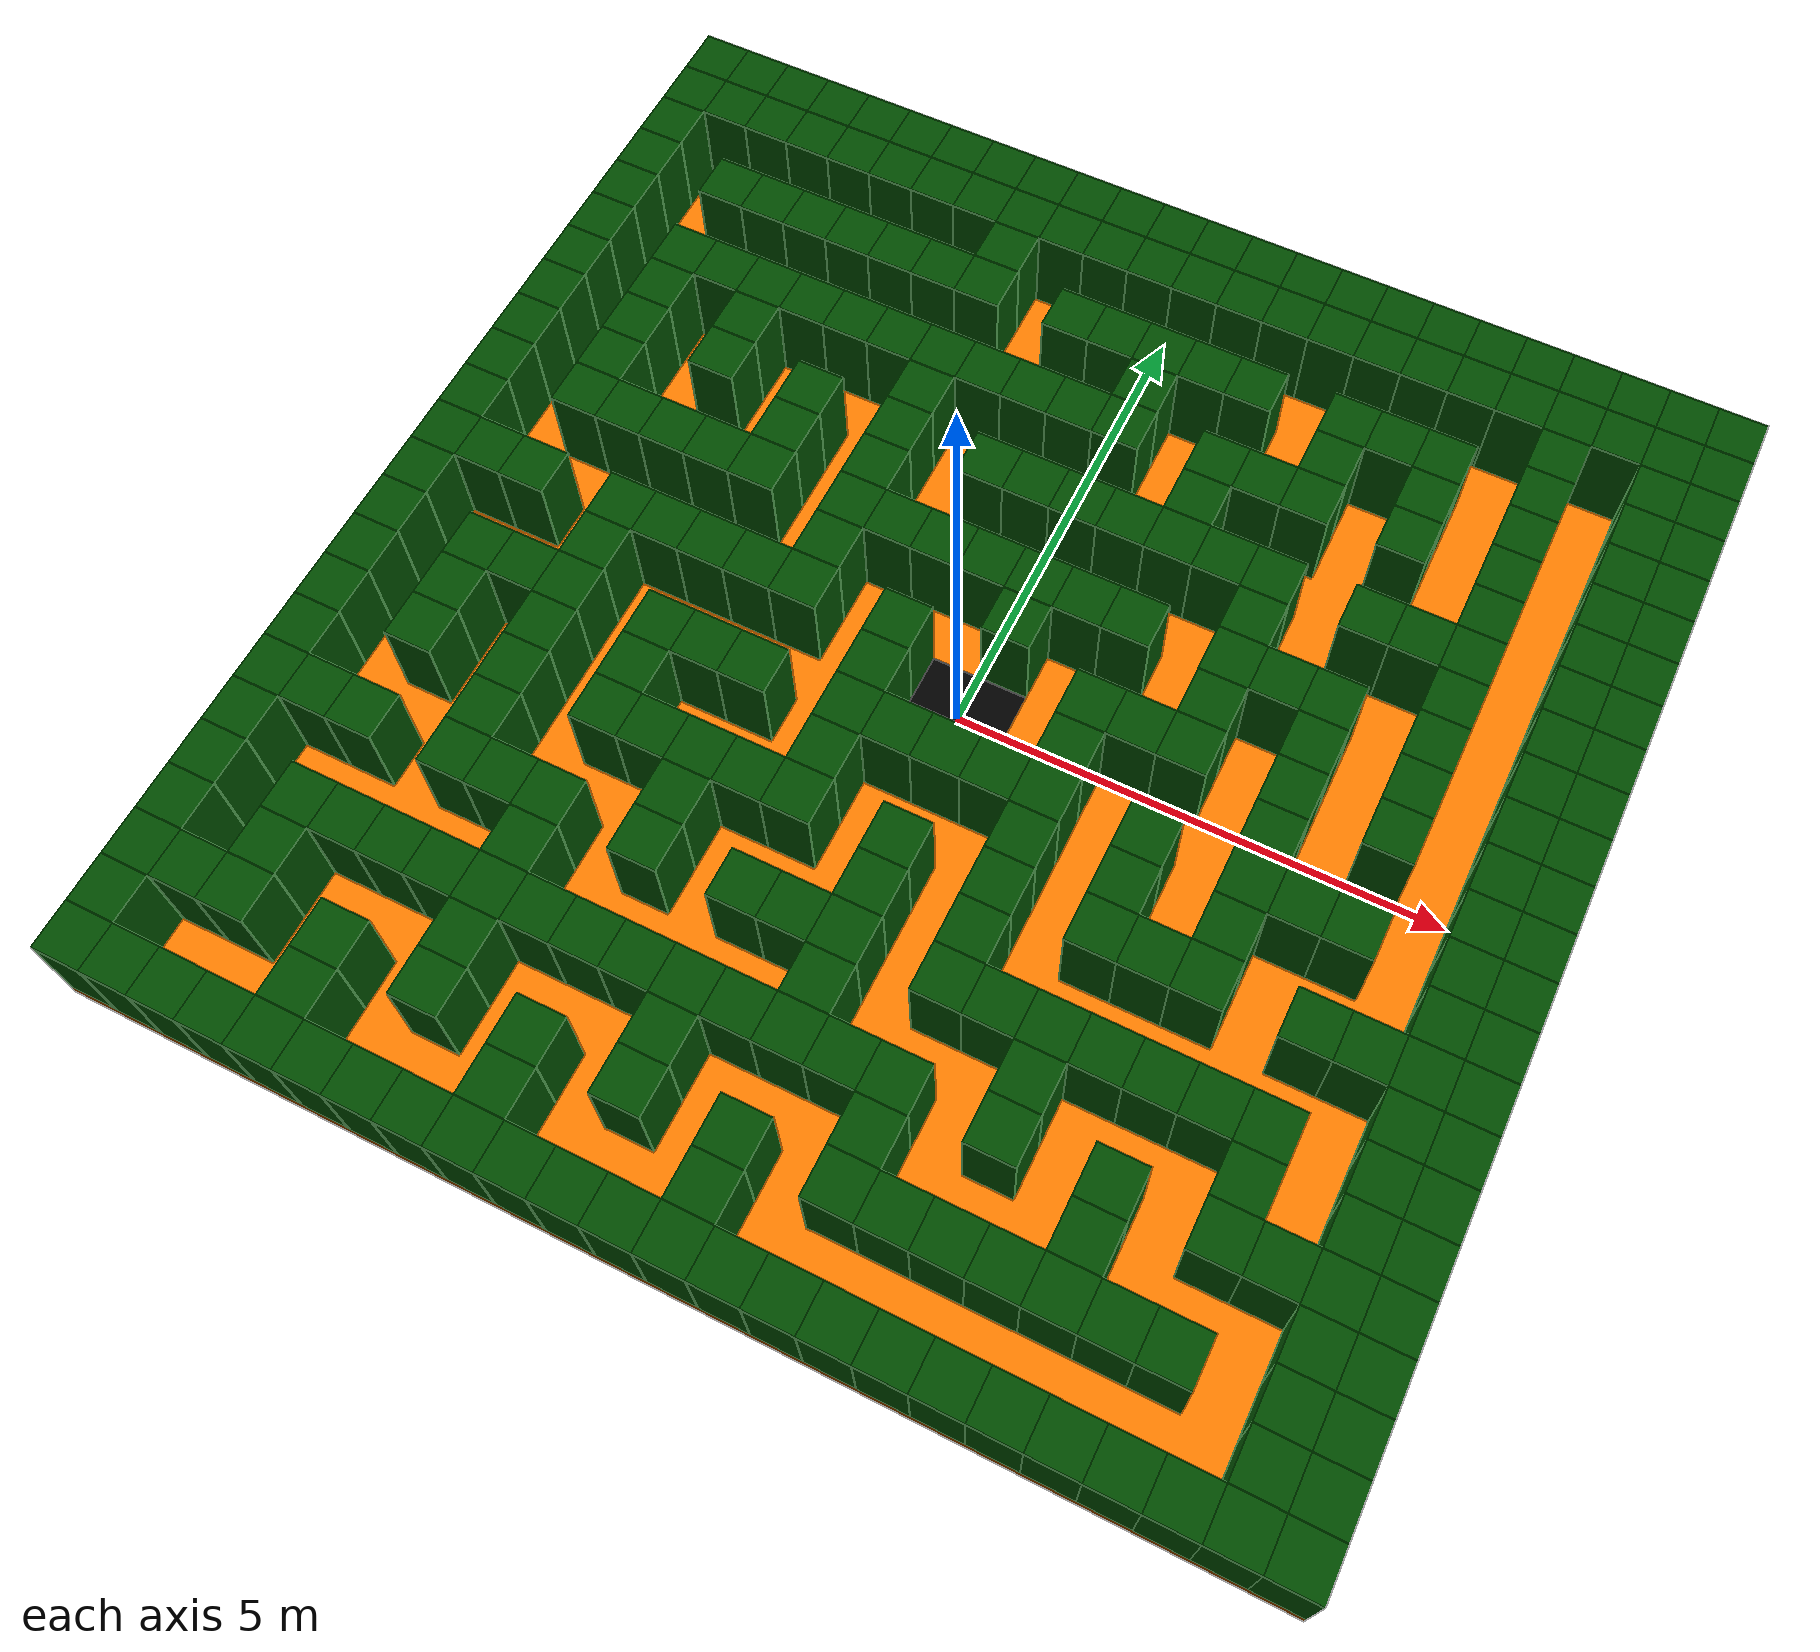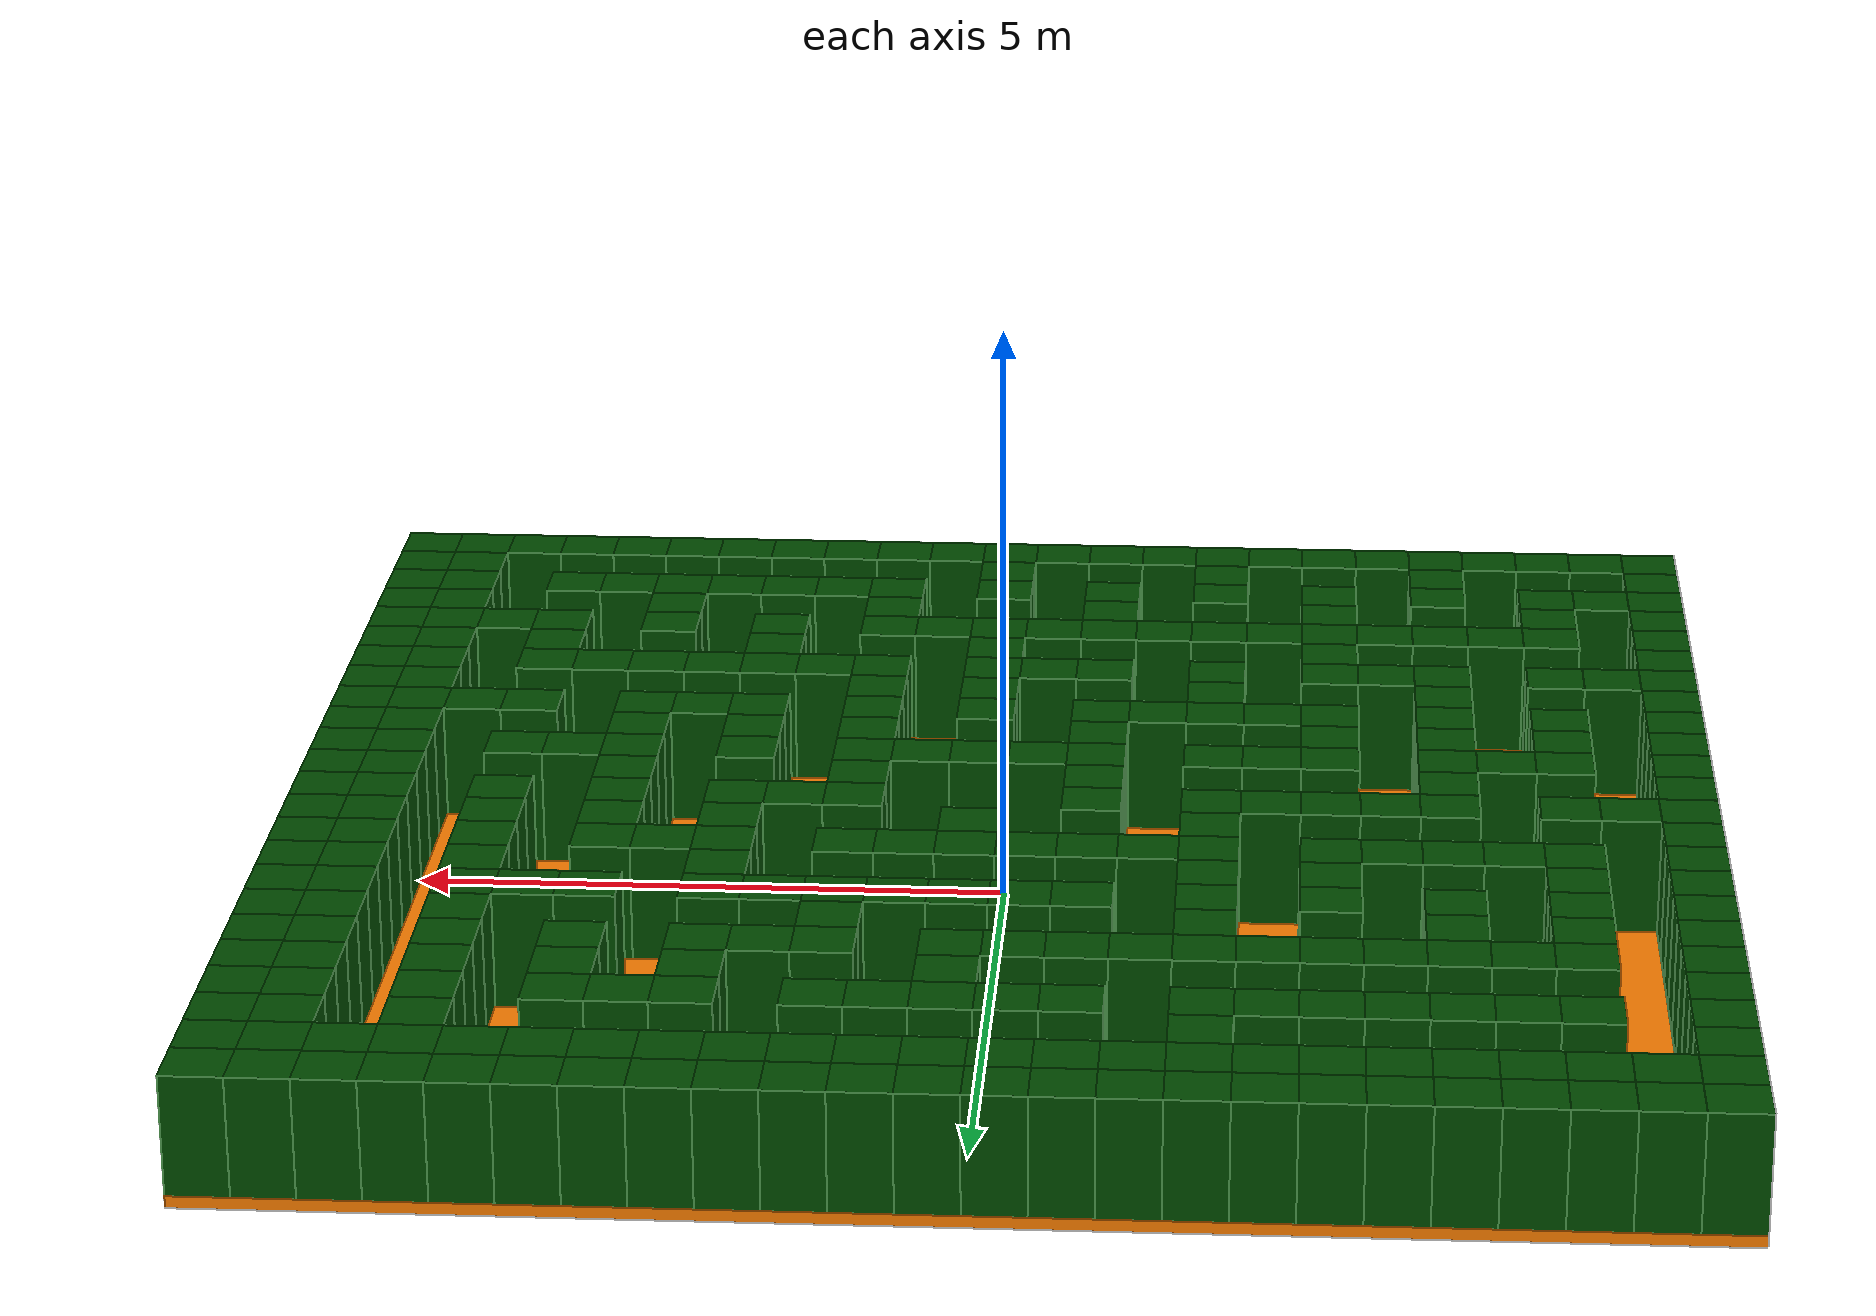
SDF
<?xml version="1.0"?>
<sdf version="1.6">
  <world name="turtlebot3_maze">

    <scene>
      <ambient>0.5 0.5 0.5 1</ambient>
    </scene>

    <light name="sun" type="directional">
      <pose>0 0 10 0 0 0</pose>
      <diffuse>1 1 1 1</diffuse>
      <specular>0.1 0.1 0.1 1</specular>
      <attenuation>
        <range>1000</range>
        <constant>4</constant>
        <linear>0.1</linear>
        <quadratic>0.001</quadratic>
      </attenuation>
      <direction>-0.5 0.5 -1</direction>
    </light>

    <model name="maze_floor_debug">
      <static>true</static>
      <pose>0 0 -0.05 0 0 0</pose>

      <link name="link">
        <!-- Full-floor collision -->
        <collision name="collision">
          <geometry>
            <box><size>12 12 0.1</size></box>
          </geometry>
        </collision>

        <!-- Orange base -->
        <visual name="orange_visual">
          <geometry>
            <box><size>12 12 0.1</size></box>
          </geometry>
          <material>
            <ambient>1 0.5 0 1</ambient>
            <diffuse>1 0.5 0 1</diffuse>
          </material>
        </visual>

        <!-- Black center patch, lifted above orange -->
        <visual name="black_center">
          <!-- Raise it half the orange thickness + half the black thickness + small epsilon -->
          <pose>0 0 0.061 0 0 0</pose>
          <geometry>
            <box><size>1 1 0.02</size></box>
          </geometry>
          <material>
            <ambient>0 0 0 1</ambient>
            <diffuse>0 0 0 1</diffuse>
          </material>
        </visual>
      </link>
    </model>

    <model name="wall_0_0">
      <static>true</static>
      <pose>-5.75 -5.75 0.5 0 0 0</pose>
      <link name="link">
        <collision name="collision">
          <geometry>
            <box>
              <size>0.5 0.5 1.0</size>
            </box>
          </geometry>
        </collision>
        <visual name="visual">
          <geometry>
            <box>
              <size>0.5 0.5 1.0</size>
            </box>
          </geometry>
          <material>
            <ambient>0 0.3 0 1</ambient>
            <diffuse>0 0.3 0 1</diffuse>
          </material>
        </visual>
      </link>
    </model>

    <model name="wall_1_0">
      <static>true</static>
      <pose>-5.25 -5.75 0.5 0 0 0</pose>
      <link name="link">
        <collision name="collision">
          <geometry>
            <box>
              <size>0.5 0.5 1.0</size>
            </box>
          </geometry>
        </collision>
        <visual name="visual">
          <geometry>
            <box>
              <size>0.5 0.5 1.0</size>
            </box>
          </geometry>
          <material>
            <ambient>0 0.3 0 1</ambient>
            <diffuse>0 0.3 0 1</diffuse>
          </material>
        </visual>
      </link>
    </model>

    <model name="wall_2_0">
      <static>true</static>
      <pose>-4.75 -5.75 0.5 0 0 0</pose>
      <link name="link">
        <collision name="collision">
          <geometry>
            <box>
              <size>0.5 0.5 1.0</size>
            </box>
          </geometry>
        </collision>
        <visual name="visual">
          <geometry>
            <box>
              <size>0.5 0.5 1.0</size>
            </box>
          </geometry>
          <material>
            <ambient>0 0.3 0 1</ambient>
            <diffuse>0 0.3 0 1</diffuse>
          </material>
        </visual>
      </link>
    </model>

    <model name="wall_3_0">
      <static>true</static>
      <pose>-4.25 -5.75 0.5 0 0 0</pose>
      <link name="link">
        <collision name="collision">
          <geometry>
            <box>
              <size>0.5 0.5 1.0</size>
            </box>
          </geometry>
        </collision>
        <visual name="visual">
          <geometry>
            <box>
              <size>0.5 0.5 1.0</size>
            </box>
          </geometry>
          <material>
            <ambient>0 0.3 0 1</ambient>
            <diffuse>0 0.3 0 1</diffuse>
          </material>
        </visual>
      </link>
    </model>

    <model name="wall_4_0">
      <static>true</static>
      <pose>-3.75 -5.75 0.5 0 0 0</pose>
      <link name="link">
        <collision name="collision">
          <geometry>
            <box>
              <size>0.5 0.5 1.0</size>
            </box>
          </geometry>
        </collision>
        <visual name="visual">
          <geometry>
            <box>
              <size>0.5 0.5 1.0</size>
            </box>
          </geometry>
          <material>
            <ambient>0 0.3 0 1</ambient>
            <diffuse>0 0.3 0 1</diffuse>
          </material>
        </visual>
      </link>
    </model>

    <model name="wall_5_0">
      <static>true</static>
      <pose>-3.25 -5.75 0.5 0 0 0</pose>
      <link name="link">
        <collision name="collision">
          <geometry>
            <box>
              <size>0.5 0.5 1.0</size>
            </box>
          </geometry>
        </collision>
        <visual name="visual">
          <geometry>
            <box>
              <size>0.5 0.5 1.0</size>
            </box>
          </geometry>
          <material>
            <ambient>0 0.3 0 1</ambient>
            <diffuse>0 0.3 0 1</diffuse>
          </material>
        </visual>
      </link>
    </model>

    <model name="wall_6_0">
      <static>true</static>
      <pose>-2.75 -5.75 0.5 0 0 0</pose>
      <link name="link">
        <collision name="collision">
          <geometry>
            <box>
              <size>0.5 0.5 1.0</size>
            </box>
          </geometry>
        </collision>
        <visual name="visual">
          <geometry>
            <box>
              <size>0.5 0.5 1.0</size>
            </box>
          </geometry>
          <material>
            <ambient>0 0.3 0 1</ambient>
            <diffuse>0 0.3 0 1</diffuse>
          </material>
        </visual>
      </link>
    </model>

    <model name="wall_7_0">
      <static>true</static>
      <pose>-2.25 -5.75 0.5 0 0 0</pose>
      <link name="link">
        <collision name="collision">
          <geometry>
            <box>
              <size>0.5 0.5 1.0</size>
            </box>
          </geometry>
        </collision>
        <visual name="visual">
          <geometry>
            <box>
              <size>0.5 0.5 1.0</size>
            </box>
          </geometry>
          <material>
            <ambient>0 0.3 0 1</ambient>
            <diffuse>0 0.3 0 1</diffuse>
          </material>
        </visual>
      </link>
    </model>

    <model name="wall_8_0">
      <static>true</static>
      <pose>-1.75 -5.75 0.5 0 0 0</pose>
      <link name="link">
        <collision name="collision">
          <geometry>
            <box>
              <size>0.5 0.5 1.0</size>
            </box>
          </geometry>
        </collision>
        <visual name="visual">
          <geometry>
            <box>
              <size>0.5 0.5 1.0</size>
            </box>
          </geometry>
          <material>
            <ambient>0 0.3 0 1</ambient>
            <diffuse>0 0.3 0 1</diffuse>
          </material>
        </visual>
      </link>
    </model>

    <model name="wall_9_0">
      <static>true</static>
      <pose>-1.25 -5.75 0.5 0 0 0</pose>
      <link name="link">
        <collision name="collision">
          <geometry>
            <box>
              <size>0.5 0.5 1.0</size>
            </box>
          </geometry>
        </collision>
        <visual name="visual">
          <geometry>
            <box>
              <size>0.5 0.5 1.0</size>
            </box>
          </geometry>
          <material>
            <ambient>0 0.3 0 1</ambient>
            <diffuse>0 0.3 0 1</diffuse>
          </material>
        </visual>
      </link>
    </model>

    <model name="wall_10_0">
      <static>true</static>
      <pose>-0.75 -5.75 0.5 0 0 0</pose>
      <link name="link">
        <collision name="collision">
          <geometry>
            <box>
              <size>0.5 0.5 1.0</size>
            </box>
          </geometry>
        </collision>
        <visual name="visual">
          <geometry>
            <box>
              <size>0.5 0.5 1.0</size>
            </box>
          </geometry>
          <material>
            <ambient>0 0.3 0 1</ambient>
            <diffuse>0 0.3 0 1</diffuse>
          </material>
        </visual>
      </link>
    </model>

    <model name="wall_11_0">
      <static>true</static>
      <pose>-0.25 -5.75 0.5 0 0 0</pose>
      <link name="link">
        <collision name="collision">
          <geometry>
            <box>
              <size>0.5 0.5 1.0</size>
            </box>
          </geometry>
        </collision>
        <visual name="visual">
          <geometry>
            <box>
              <size>0.5 0.5 1.0</size>
            </box>
          </geometry>
          <material>
            <ambient>0 0.3 0 1</ambient>
            <diffuse>0 0.3 0 1</diffuse>
          </material>
        </visual>
      </link>
    </model>

    <model name="wall_12_0">
      <static>true</static>
      <pose>0.25 -5.75 0.5 0 0 0</pose>
      <link name="link">
        <collision name="collision">
          <geometry>
            <box>
              <size>0.5 0.5 1.0</size>
            </box>
          </geometry>
        </collision>
        <visual name="visual">
          <geometry>
            <box>
              <size>0.5 0.5 1.0</size>
            </box>
          </geometry>
          <material>
            <ambient>0 0.3 0 1</ambient>
            <diffuse>0 0.3 0 1</diffuse>
          </material>
        </visual>
      </link>
    </model>

    <model name="wall_13_0">
      <static>true</static>
      <pose>0.75 -5.75 0.5 0 0 0</pose>
      <link name="link">
        <collision name="collision">
          <geometry>
            <box>
              <size>0.5 0.5 1.0</size>
            </box>
          </geometry>
        </collision>
        <visual name="visual">
          <geometry>
            <box>
              <size>0.5 0.5 1.0</size>
            </box>
          </geometry>
          <material>
            <ambient>0 0.3 0 1</ambient>
            <diffuse>0 0.3 0 1</diffuse>
          </material>
        </visual>
      </link>
    </model>

    <model name="wall_14_0">
      <static>true</static>
      <pose>1.25 -5.75 0.5 0 0 0</pose>
      <link name="link">
        <collision name="collision">
          <geometry>
            <box>
              <size>0.5 0.5 1.0</size>
            </box>
          </geometry>
        </collision>
        <visual name="visual">
          <geometry>
            <box>
              <size>0.5 0.5 1.0</size>
            </box>
          </geometry>
          <material>
            <ambient>0 0.3 0 1</ambient>
            <diffuse>0 0.3 0 1</diffuse>
          </material>
        </visual>
      </link>
    </model>

    <model name="wall_15_0">
      <static>true</static>
      <pose>1.75 -5.75 0.5 0 0 0</pose>
      <link name="link">
        <collision name="collision">
          <geometry>
            <box>
              <size>0.5 0.5 1.0</size>
            </box>
          </geometry>
        </collision>
        <visual name="visual">
          <geometry>
            <box>
              <size>0.5 0.5 1.0</size>
            </box>
          </geometry>
          <material>
            <ambient>0 0.3 0 1</ambient>
            <diffuse>0 0.3 0 1</diffuse>
          </material>
        </visual>
      </link>
    </model>

    <model name="wall_16_0">
      <static>true</static>
      <pose>2.25 -5.75 0.5 0 0 0</pose>
      <link name="link">
        <collision name="collision">
          <geometry>
            <box>
              <size>0.5 0.5 1.0</size>
            </box>
          </geometry>
        </collision>
        <visual name="visual">
          <geometry>
            <box>
              <size>0.5 0.5 1.0</size>
            </box>
          </geometry>
          <material>
            <ambient>0 0.3 0 1</ambient>
            <diffuse>0 0.3 0 1</diffuse>
          </material>
        </visual>
      </link>
    </model>

    <model name="wall_17_0">
      <static>true</static>
      <pose>2.75 -5.75 0.5 0 0 0</pose>
      <link name="link">
        <collision name="collision">
          <geometry>
            <box>
              <size>0.5 0.5 1.0</size>
            </box>
          </geometry>
        </collision>
        <visual name="visual">
          <geometry>
            <box>
              <size>0.5 0.5 1.0</size>
            </box>
          </geometry>
          <material>
            <ambient>0 0.3 0 1</ambient>
            <diffuse>0 0.3 0 1</diffuse>
          </material>
        </visual>
      </link>
    </model>

    <model name="wall_18_0">
      <static>true</static>
      <pose>3.25 -5.75 0.5 0 0 0</pose>
      <link name="link">
        <collision name="collision">
          <geometry>
            <box>
              <size>0.5 0.5 1.0</size>
            </box>
          </geometry>
        </collision>
        <visual name="visual">
          <geometry>
            <box>
              <size>0.5 0.5 1.0</size>
            </box>
          </geometry>
          <material>
            <ambient>0 0.3 0 1</ambient>
            <diffuse>0 0.3 0 1</diffuse>
          </material>
        </visual>
      </link>
    </model>

    <model name="wall_19_0">
      <static>true</static>
      <pose>3.75 -5.75 0.5 0 0 0</pose>
      <link name="link">
        <collision name="collision">
          <geometry>
            <box>
              <size>0.5 0.5 1.0</size>
            </box>
          </geometry>
        </collision>
        <visual name="visual">
          <geometry>
            <box>
              <size>0.5 0.5 1.0</size>
            </box>
          </geometry>
          <material>
            <ambient>0 0.3 0 1</ambient>
            <diffuse>0 0.3 0 1</diffuse>
          </material>
        </visual>
      </link>
    </model>

    <model name="wall_20_0">
      <static>true</static>
      <pose>4.25 -5.75 0.5 0 0 0</pose>
      <link name="link">
        <collision name="collision">
          <geometry>
            <box>
              <size>0.5 0.5 1.0</size>
            </box>
          </geometry>
        </collision>
        <visual name="visual">
          <geometry>
            <box>
              <size>0.5 0.5 1.0</size>
            </box>
          </geometry>
          <material>
            <ambient>0 0.3 0 1</ambient>
            <diffuse>0 0.3 0 1</diffuse>
          </material>
        </visual>
      </link>
    </model>

    <model name="wall_21_0">
      <static>true</static>
      <pose>4.75 -5.75 0.5 0 0 0</pose>
      <link name="link">
        <collision name="collision">
          <geometry>
            <box>
              <size>0.5 0.5 1.0</size>
            </box>
          </geometry>
        </collision>
        <visual name="visual">
          <geometry>
            <box>
              <size>0.5 0.5 1.0</size>
            </box>
          </geometry>
          <material>
            <ambient>0 0.3 0 1</ambient>
            <diffuse>0 0.3 0 1</diffuse>
          </material>
        </visual>
      </link>
    </model>

    <model name="wall_22_0">
      <static>true</static>
      <pose>5.25 -5.75 0.5 0 0 0</pose>
      <link name="link">
        <collision name="collision">
          <geometry>
            <box>
              <size>0.5 0.5 1.0</size>
            </box>
          </geometry>
        </collision>
        <visual name="visual">
          <geometry>
            <box>
              <size>0.5 0.5 1.0</size>
            </box>
          </geometry>
          <material>
            <ambient>0 0.3 0 1</ambient>
            <diffuse>0 0.3 0 1</diffuse>
          </material>
        </visual>
      </link>
    </model>

    <model name="wall_23_0">
      <static>true</static>
      <pose>5.75 -5.75 0.5 0 0 0</pose>
      <link name="link">
        <collision name="collision">
          <geometry>
            <box>
              <size>0.5 0.5 1.0</size>
            </box>
          </geometry>
        </collision>
        <visual name="visual">
          <geometry>
            <box>
              <size>0.5 0.5 1.0</size>
            </box>
          </geometry>
          <material>
            <ambient>0 0.3 0 1</ambient>
            <diffuse>0 0.3 0 1</diffuse>
          </material>
        </visual>
      </link>
    </model>

    <model name="wall_0_1">
      <static>true</static>
      <pose>-5.75 -5.25 0.5 0 0 0</pose>
      <link name="link">
        <collision name="collision">
          <geometry>
            <box>
              <size>0.5 0.5 1.0</size>
            </box>
          </geometry>
        </collision>
        <visual name="visual">
          <geometry>
            <box>
              <size>0.5 0.5 1.0</size>
            </box>
          </geometry>
          <material>
            <ambient>0 0.3 0 1</ambient>
            <diffuse>0 0.3 0 1</diffuse>
          </material>
        </visual>
      </link>
    </model>

    <model name="wall_4_1">
      <static>true</static>
      <pose>-3.75 -5.25 0.5 0 0 0</pose>
      <link name="link">
        <collision name="collision">
          <geometry>
            <box>
              <size>0.5 0.5 1.0</size>
            </box>
          </geometry>
        </collision>
        <visual name="visual">
          <geometry>
            <box>
              <size>0.5 0.5 1.0</size>
            </box>
          </geometry>
          <material>
            <ambient>0 0.3 0 1</ambient>
            <diffuse>0 0.3 0 1</diffuse>
          </material>
        </visual>
      </link>
    </model>

    <model name="wall_8_1">
      <static>true</static>
      <pose>-1.75 -5.25 0.5 0 0 0</pose>
      <link name="link">
        <collision name="collision">
          <geometry>
            <box>
              <size>0.5 0.5 1.0</size>
            </box>
          </geometry>
        </collision>
        <visual name="visual">
          <geometry>
            <box>
              <size>0.5 0.5 1.0</size>
            </box>
          </geometry>
          <material>
            <ambient>0 0.3 0 1</ambient>
            <diffuse>0 0.3 0 1</diffuse>
          </material>
        </visual>
      </link>
    </model>

    <model name="wall_12_1">
      <static>true</static>
      <pose>0.25 -5.25 0.5 0 0 0</pose>
      <link name="link">
        <collision name="collision">
          <geometry>
            <box>
              <size>0.5 0.5 1.0</size>
            </box>
          </geometry>
        </collision>
        <visual name="visual">
          <geometry>
            <box>
              <size>0.5 0.5 1.0</size>
            </box>
          </geometry>
          <material>
            <ambient>0 0.3 0 1</ambient>
            <diffuse>0 0.3 0 1</diffuse>
          </material>
        </visual>
      </link>
    </model>

    <model name="wall_22_1">
      <static>true</static>
      <pose>5.25 -5.25 0.5 0 0 0</pose>
      <link name="link">
        <collision name="collision">
          <geometry>
            <box>
              <size>0.5 0.5 1.0</size>
            </box>
          </geometry>
        </collision>
        <visual name="visual">
          <geometry>
            <box>
              <size>0.5 0.5 1.0</size>
            </box>
          </geometry>
          <material>
            <ambient>0 0.3 0 1</ambient>
            <diffuse>0 0.3 0 1</diffuse>
          </material>
        </visual>
      </link>
    </model>

    <model name="wall_23_1">
      <static>true</static>
      <pose>5.75 -5.25 0.5 0 0 0</pose>
      <link name="link">
        <collision name="collision">
          <geometry>
            <box>
              <size>0.5 0.5 1.0</size>
            </box>
          </geometry>
        </collision>
        <visual name="visual">
          <geometry>
            <box>
              <size>0.5 0.5 1.0</size>
            </box>
          </geometry>
          <material>
            <ambient>0 0.3 0 1</ambient>
            <diffuse>0 0.3 0 1</diffuse>
          </material>
        </visual>
      </link>
    </model>

    <model name="wall_0_2">
      <static>true</static>
      <pose>-5.75 -4.75 0.5 0 0 0</pose>
      <link name="link">
        <collision name="collision">
          <geometry>
            <box>
              <size>0.5 0.5 1.0</size>
            </box>
          </geometry>
        </collision>
        <visual name="visual">
          <geometry>
            <box>
              <size>0.5 0.5 1.0</size>
            </box>
          </geometry>
          <material>
            <ambient>0 0.3 0 1</ambient>
            <diffuse>0 0.3 0 1</diffuse>
          </material>
        </visual>
      </link>
    </model>

    <model name="wall_1_2">
      <static>true</static>
      <pose>-5.25 -4.75 0.5 0 0 0</pose>
      <link name="link">
        <collision name="collision">
          <geometry>
            <box>
              <size>0.5 0.5 1.0</size>
            </box>
          </geometry>
        </collision>
        <visual name="visual">
          <geometry>
            <box>
              <size>0.5 0.5 1.0</size>
            </box>
          </geometry>
          <material>
            <ambient>0 0.3 0 1</ambient>
            <diffuse>0 0.3 0 1</diffuse>
          </material>
        </visual>
      </link>
    </model>

    <model name="wall_2_2">
      <static>true</static>
      <pose>-4.75 -4.75 0.5 0 0 0</pose>
      <link name="link">
        <collision name="collision">
          <geometry>
            <box>
              <size>0.5 0.5 1.0</size>
            </box>
          </geometry>
        </collision>
        <visual name="visual">
          <geometry>
            <box>
              <size>0.5 0.5 1.0</size>
            </box>
          </geometry>
          <material>
            <ambient>0 0.3 0 1</ambient>
            <diffuse>0 0.3 0 1</diffuse>
          </material>
        </visual>
      </link>
    </model>

    <model name="wall_4_2">
      <static>true</static>
      <pose>-3.75 -4.75 0.5 0 0 0</pose>
      <link name="link">
        <collision name="collision">
          <geometry>
            <box>
              <size>0.5 0.5 1.0</size>
            </box>
          </geometry>
        </collision>
        <visual name="visual">
          <geometry>
            <box>
              <size>0.5 0.5 1.0</size>
            </box>
          </geometry>
          <material>
            <ambient>0 0.3 0 1</ambient>
            <diffuse>0 0.3 0 1</diffuse>
          </material>
        </visual>
      </link>
    </model>

    <model name="wall_6_2">
      <static>true</static>
      <pose>-2.75 -4.75 0.5 0 0 0</pose>
      <link name="link">
        <collision name="collision">
          <geometry>
            <box>
              <size>0.5 0.5 1.0</size>
            </box>
          </geometry>
        </collision>
        <visual name="visual">
          <geometry>
            <box>
              <size>0.5 0.5 1.0</size>
            </box>
          </geometry>
          <material>
            <ambient>0 0.3 0 1</ambient>
            <diffuse>0 0.3 0 1</diffuse>
          </material>
        </visual>
      </link>
    </model>

    <model name="wall_8_2">
      <static>true</static>
      <pose>-1.75 -4.75 0.5 0 0 0</pose>
      <link name="link">
        <collision name="collision">
          <geometry>
            <box>
              <size>0.5 0.5 1.0</size>
            </box>
          </geometry>
        </collision>
        <visual name="visual">
          <geometry>
            <box>
              <size>0.5 0.5 1.0</size>
            </box>
          </geometry>
          <material>
            <ambient>0 0.3 0 1</ambient>
            <diffuse>0 0.3 0 1</diffuse>
          </material>
        </visual>
      </link>
    </model>

    <model name="wall_10_2">
      <static>true</static>
      <pose>-0.75 -4.75 0.5 0 0 0</pose>
      <link name="link">
        <collision name="collision">
          <geometry>
            <box>
              <size>0.5 0.5 1.0</size>
            </box>
          </geometry>
        </collision>
        <visual name="visual">
          <geometry>
            <box>
              <size>0.5 0.5 1.0</size>
            </box>
          </geometry>
          <material>
            <ambient>0 0.3 0 1</ambient>
            <diffuse>0 0.3 0 1</diffuse>
          </material>
        </visual>
      </link>
    </model>

    <model name="wall_12_2">
      <static>true</static>
      <pose>0.25 -4.75 0.5 0 0 0</pose>
      <link name="link">
        <collision name="collision">
          <geometry>
            <box>
              <size>0.5 0.5 1.0</size>
            </box>
          </geometry>
        </collision>
        <visual name="visual">
          <geometry>
            <box>
              <size>0.5 0.5 1.0</size>
            </box>
          </geometry>
          <material>
            <ambient>0 0.3 0 1</ambient>
            <diffuse>0 0.3 0 1</diffuse>
          </material>
        </visual>
      </link>
    </model>

    <model name="wall_14_2">
      <static>true</static>
      <pose>1.25 -4.75 0.5 0 0 0</pose>
      <link name="link">
        <collision name="collision">
          <geometry>
            <box>
              <size>0.5 0.5 1.0</size>
            </box>
          </geometry>
        </collision>
        <visual name="visual">
          <geometry>
            <box>
              <size>0.5 0.5 1.0</size>
            </box>
          </geometry>
          <material>
            <ambient>0 0.3 0 1</ambient>
            <diffuse>0 0.3 0 1</diffuse>
          </material>
        </visual>
      </link>
    </model>

    <model name="wall_15_2">
      <static>true</static>
      <pose>1.75 -4.75 0.5 0 0 0</pose>
      <link name="link">
        <collision name="collision">
          <geometry>
            <box>
              <size>0.5 0.5 1.0</size>
            </box>
          </geometry>
        </collision>
        <visual name="visual">
          <geometry>
            <box>
              <size>0.5 0.5 1.0</size>
            </box>
          </geometry>
          <material>
            <ambient>0 0.3 0 1</ambient>
            <diffuse>0 0.3 0 1</diffuse>
          </material>
        </visual>
      </link>
    </model>

    <model name="wall_16_2">
      <static>true</static>
      <pose>2.25 -4.75 0.5 0 0 0</pose>
      <link name="link">
        <collision name="collision">
          <geometry>
            <box>
              <size>0.5 0.5 1.0</size>
            </box>
          </geometry>
        </collision>
        <visual name="visual">
          <geometry>
            <box>
              <size>0.5 0.5 1.0</size>
            </box>
          </geometry>
          <material>
            <ambient>0 0.3 0 1</ambient>
            <diffuse>0 0.3 0 1</diffuse>
          </material>
        </visual>
      </link>
    </model>

    <model name="wall_17_2">
      <static>true</static>
      <pose>2.75 -4.75 0.5 0 0 0</pose>
      <link name="link">
        <collision name="collision">
          <geometry>
            <box>
              <size>0.5 0.5 1.0</size>
            </box>
          </geometry>
        </collision>
        <visual name="visual">
          <geometry>
            <box>
              <size>0.5 0.5 1.0</size>
            </box>
          </geometry>
          <material>
            <ambient>0 0.3 0 1</ambient>
            <diffuse>0 0.3 0 1</diffuse>
          </material>
        </visual>
      </link>
    </model>

    <model name="wall_18_2">
      <static>true</static>
      <pose>3.25 -4.75 0.5 0 0 0</pose>
      <link name="link">
        <collision name="collision">
          <geometry>
            <box>
              <size>0.5 0.5 1.0</size>
            </box>
          </geometry>
        </collision>
        <visual name="visual">
          <geometry>
            <box>
              <size>0.5 0.5 1.0</size>
            </box>
          </geometry>
          <material>
            <ambient>0 0.3 0 1</ambient>
            <diffuse>0 0.3 0 1</diffuse>
          </material>
        </visual>
      </link>
    </model>

    <model name="wall_19_2">
      <static>true</static>
      <pose>3.75 -4.75 0.5 0 0 0</pose>
      <link name="link">
        <collision name="collision">
          <geometry>
            <box>
              <size>0.5 0.5 1.0</size>
            </box>
          </geometry>
        </collision>
        <visual name="visual">
          <geometry>
            <box>
              <size>0.5 0.5 1.0</size>
            </box>
          </geometry>
          <material>
            <ambient>0 0.3 0 1</ambient>
            <diffuse>0 0.3 0 1</diffuse>
          </material>
        </visual>
      </link>
    </model>

    <model name="wall_20_2">
      <static>true</static>
      <pose>4.25 -4.75 0.5 0 0 0</pose>
      <link name="link">
        <collision name="collision">
          <geometry>
            <box>
              <size>0.5 0.5 1.0</size>
            </box>
          </geometry>
        </collision>
        <visual name="visual">
          <geometry>
            <box>
              <size>0.5 0.5 1.0</size>
            </box>
          </geometry>
          <material>
            <ambient>0 0.3 0 1</ambient>
            <diffuse>0 0.3 0 1</diffuse>
          </material>
        </visual>
      </link>
    </model>

    <model name="wall_22_2">
      <static>true</static>
      <pose>5.25 -4.75 0.5 0 0 0</pose>
      <link name="link">
        <collision name="collision">
          <geometry>
            <box>
              <size>0.5 0.5 1.0</size>
            </box>
          </geometry>
        </collision>
        <visual name="visual">
          <geometry>
            <box>
              <size>0.5 0.5 1.0</size>
            </box>
          </geometry>
          <material>
            <ambient>0 0.3 0 1</ambient>
            <diffuse>0 0.3 0 1</diffuse>
          </material>
        </visual>
      </link>
    </model>

    <model name="wall_23_2">
      <static>true</static>
      <pose>5.75 -4.75 0.5 0 0 0</pose>
      <link name="link">
        <collision name="collision">
          <geometry>
            <box>
              <size>0.5 0.5 1.0</size>
            </box>
          </geometry>
        </collision>
        <visual name="visual">
          <geometry>
            <box>
              <size>0.5 0.5 1.0</size>
            </box>
          </geometry>
          <material>
            <ambient>0 0.3 0 1</ambient>
            <diffuse>0 0.3 0 1</diffuse>
          </material>
        </visual>
      </link>
    </model>

    <model name="wall_0_3">
      <static>true</static>
      <pose>-5.75 -4.25 0.5 0 0 0</pose>
      <link name="link">
        <collision name="collision">
          <geometry>
            <box>
              <size>0.5 0.5 1.0</size>
            </box>
          </geometry>
        </collision>
        <visual name="visual">
          <geometry>
            <box>
              <size>0.5 0.5 1.0</size>
            </box>
          </geometry>
          <material>
            <ambient>0 0.3 0 1</ambient>
            <diffuse>0 0.3 0 1</diffuse>
          </material>
        </visual>
      </link>
    </model>

    <model name="wall_2_3">
      <static>true</static>
      <pose>-4.75 -4.25 0.5 0 0 0</pose>
      <link name="link">
        <collision name="collision">
          <geometry>
            <box>
              <size>0.5 0.5 1.0</size>
            </box>
          </geometry>
        </collision>
        <visual name="visual">
          <geometry>
            <box>
              <size>0.5 0.5 1.0</size>
            </box>
          </geometry>
          <material>
            <ambient>0 0.3 0 1</ambient>
            <diffuse>0 0.3 0 1</diffuse>
          </material>
        </visual>
      </link>
    </model>

    <model name="wall_6_3">
      <static>true</static>
      <pose>-2.75 -4.25 0.5 0 0 0</pose>
      <link name="link">
        <collision name="collision">
          <geometry>
            <box>
              <size>0.5 0.5 1.0</size>
            </box>
          </geometry>
        </collision>
        <visual name="visual">
          <geometry>
            <box>
              <size>0.5 0.5 1.0</size>
            </box>
          </geometry>
          <material>
            <ambient>0 0.3 0 1</ambient>
            <diffuse>0 0.3 0 1</diffuse>
          </material>
        </visual>
      </link>
    </model>

    <model name="wall_10_3">
      <static>true</static>
      <pose>-0.75 -4.25 0.5 0 0 0</pose>
      <link name="link">
        <collision name="collision">
          <geometry>
            <box>
              <size>0.5 0.5 1.0</size>
            </box>
          </geometry>
        </collision>
        <visual name="visual">
          <geometry>
            <box>
              <size>0.5 0.5 1.0</size>
            </box>
          </geometry>
          <material>
            <ambient>0 0.3 0 1</ambient>
            <diffuse>0 0.3 0 1</diffuse>
          </material>
        </visual>
      </link>
    </model>

    <model name="wall_14_3">
      <static>true</static>
      <pose>1.25 -4.25 0.5 0 0 0</pose>
      <link name="link">
        <collision name="collision">
          <geometry>
            <box>
              <size>0.5 0.5 1.0</size>
            </box>
          </geometry>
        </collision>
        <visual name="visual">
          <geometry>
            <box>
              <size>0.5 0.5 1.0</size>
            </box>
          </geometry>
          <material>
            <ambient>0 0.3 0 1</ambient>
            <diffuse>0 0.3 0 1</diffuse>
          </material>
        </visual>
      </link>
    </model>

    <model name="wall_18_3">
      <static>true</static>
      <pose>3.25 -4.25 0.5 0 0 0</pose>
      <link name="link">
        <collision name="collision">
          <geometry>
            <box>
              <size>0.5 0.5 1.0</size>
            </box>
          </geometry>
        </collision>
        <visual name="visual">
          <geometry>
            <box>
              <size>0.5 0.5 1.0</size>
            </box>
          </geometry>
          <material>
            <ambient>0 0.3 0 1</ambient>
            <diffuse>0 0.3 0 1</diffuse>
          </material>
        </visual>
      </link>
    </model>

    <model name="wall_22_3">
      <static>true</static>
      <pose>5.25 -4.25 0.5 0 0 0</pose>
      <link name="link">
        <collision name="collision">
          <geometry>
            <box>
              <size>0.5 0.5 1.0</size>
            </box>
          </geometry>
        </collision>
        <visual name="visual">
          <geometry>
            <box>
              <size>0.5 0.5 1.0</size>
            </box>
          </geometry>
          <material>
            <ambient>0 0.3 0 1</ambient>
            <diffuse>0 0.3 0 1</diffuse>
          </material>
        </visual>
      </link>
    </model>

    <model name="wall_23_3">
      <static>true</static>
      <pose>5.75 -4.25 0.5 0 0 0</pose>
      <link name="link">
        <collision name="collision">
          <geometry>
            <box>
              <size>0.5 0.5 1.0</size>
            </box>
          </geometry>
        </collision>
        <visual name="visual">
          <geometry>
            <box>
              <size>0.5 0.5 1.0</size>
            </box>
          </geometry>
          <material>
            <ambient>0 0.3 0 1</ambient>
            <diffuse>0 0.3 0 1</diffuse>
          </material>
        </visual>
      </link>
    </model>

    <model name="wall_0_4">
      <static>true</static>
      <pose>-5.75 -3.75 0.5 0 0 0</pose>
      <link name="link">
        <collision name="collision">
          <geometry>
            <box>
              <size>0.5 0.5 1.0</size>
            </box>
          </geometry>
        </collision>
        <visual name="visual">
          <geometry>
            <box>
              <size>0.5 0.5 1.0</size>
            </box>
          </geometry>
          <material>
            <ambient>0 0.3 0 1</ambient>
            <diffuse>0 0.3 0 1</diffuse>
          </material>
        </visual>
      </link>
    </model>

    <model name="wall_2_4">
      <static>true</static>
      <pose>-4.75 -3.75 0.5 0 0 0</pose>
      <link name="link">
        <collision name="collision">
          <geometry>
            <box>
              <size>0.5 0.5 1.0</size>
            </box>
          </geometry>
        </collision>
        <visual name="visual">
          <geometry>
            <box>
              <size>0.5 0.5 1.0</size>
            </box>
          </geometry>
          <material>
            <ambient>0 0.3 0 1</ambient>
            <diffuse>0 0.3 0 1</diffuse>
          </material>
        </visual>
      </link>
    </model>

    <model name="wall_3_4">
      <static>true</static>
      <pose>-4.25 -3.75 0.5 0 0 0</pose>
      <link name="link">
        <collision name="collision">
          <geometry>
            <box>
              <size>0.5 0.5 1.0</size>
            </box>
          </geometry>
        </collision>
        <visual name="visual">
          <geometry>
            <box>
              <size>0.5 0.5 1.0</size>
            </box>
          </geometry>
          <material>
            <ambient>0 0.3 0 1</ambient>
            <diffuse>0 0.3 0 1</diffuse>
          </material>
        </visual>
      </link>
    </model>

    <model name="wall_4_4">
      <static>true</static>
      <pose>-3.75 -3.75 0.5 0 0 0</pose>
      <link name="link">
        <collision name="collision">
          <geometry>
            <box>
              <size>0.5 0.5 1.0</size>
            </box>
          </geometry>
        </collision>
        <visual name="visual">
          <geometry>
            <box>
              <size>0.5 0.5 1.0</size>
            </box>
          </geometry>
          <material>
            <ambient>0 0.3 0 1</ambient>
            <diffuse>0 0.3 0 1</diffuse>
          </material>
        </visual>
      </link>
    </model>

    <model name="wall_5_4">
      <static>true</static>
      <pose>-3.25 -3.75 0.5 0 0 0</pose>
      <link name="link">
        <collision name="collision">
          <geometry>
            <box>
              <size>0.5 0.5 1.0</size>
            </box>
          </geometry>
        </collision>
        <visual name="visual">
          <geometry>
            <box>
              <size>0.5 0.5 1.0</size>
            </box>
          </geometry>
          <material>
            <ambient>0 0.3 0 1</ambient>
            <diffuse>0 0.3 0 1</diffuse>
          </material>
        </visual>
      </link>
    </model>

    <model name="wall_6_4">
      <static>true</static>
      <pose>-2.75 -3.75 0.5 0 0 0</pose>
      <link name="link">
        <collision name="collision">
          <geometry>
            <box>
              <size>0.5 0.5 1.0</size>
            </box>
          </geometry>
        </collision>
        <visual name="visual">
          <geometry>
            <box>
              <size>0.5 0.5 1.0</size>
            </box>
          </geometry>
          <material>
            <ambient>0 0.3 0 1</ambient>
            <diffuse>0 0.3 0 1</diffuse>
          </material>
        </visual>
      </link>
    </model>

    <model name="wall_7_4">
      <static>true</static>
      <pose>-2.25 -3.75 0.5 0 0 0</pose>
      <link name="link">
        <collision name="collision">
          <geometry>
            <box>
              <size>0.5 0.5 1.0</size>
            </box>
          </geometry>
        </collision>
        <visual name="visual">
          <geometry>
            <box>
              <size>0.5 0.5 1.0</size>
            </box>
          </geometry>
          <material>
            <ambient>0 0.3 0 1</ambient>
            <diffuse>0 0.3 0 1</diffuse>
          </material>
        </visual>
      </link>
    </model>

    <model name="wall_8_4">
      <static>true</static>
      <pose>-1.75 -3.75 0.5 0 0 0</pose>
      <link name="link">
        <collision name="collision">
          <geometry>
            <box>
              <size>0.5 0.5 1.0</size>
            </box>
          </geometry>
        </collision>
        <visual name="visual">
          <geometry>
            <box>
              <size>0.5 0.5 1.0</size>
            </box>
          </geometry>
          <material>
            <ambient>0 0.3 0 1</ambient>
            <diffuse>0 0.3 0 1</diffuse>
          </material>
        </visual>
      </link>
    </model>

    <model name="wall_9_4">
      <static>true</static>
      <pose>-1.25 -3.75 0.5 0 0 0</pose>
      <link name="link">
        <collision name="collision">
          <geometry>
            <box>
              <size>0.5 0.5 1.0</size>
            </box>
          </geometry>
        </collision>
        <visual name="visual">
          <geometry>
            <box>
              <size>0.5 0.5 1.0</size>
            </box>
          </geometry>
          <material>
            <ambient>0 0.3 0 1</ambient>
            <diffuse>0 0.3 0 1</diffuse>
          </material>
        </visual>
      </link>
    </model>

    <model name="wall_10_4">
      <static>true</static>
      <pose>-0.75 -3.75 0.5 0 0 0</pose>
      <link name="link">
        <collision name="collision">
          <geometry>
            <box>
              <size>0.5 0.5 1.0</size>
            </box>
          </geometry>
        </collision>
        <visual name="visual">
          <geometry>
            <box>
              <size>0.5 0.5 1.0</size>
            </box>
          </geometry>
          <material>
            <ambient>0 0.3 0 1</ambient>
            <diffuse>0 0.3 0 1</diffuse>
          </material>
        </visual>
      </link>
    </model>

    <model name="wall_11_4">
      <static>true</static>
      <pose>-0.25 -3.75 0.5 0 0 0</pose>
      <link name="link">
        <collision name="collision">
          <geometry>
            <box>
              <size>0.5 0.5 1.0</size>
            </box>
          </geometry>
        </collision>
        <visual name="visual">
          <geometry>
            <box>
              <size>0.5 0.5 1.0</size>
            </box>
          </geometry>
          <material>
            <ambient>0 0.3 0 1</ambient>
            <diffuse>0 0.3 0 1</diffuse>
          </material>
        </visual>
      </link>
    </model>

    <model name="wall_12_4">
      <static>true</static>
      <pose>0.25 -3.75 0.5 0 0 0</pose>
      <link name="link">
        <collision name="collision">
          <geometry>
            <box>
              <size>0.5 0.5 1.0</size>
            </box>
          </geometry>
        </collision>
        <visual name="visual">
          <geometry>
            <box>
              <size>0.5 0.5 1.0</size>
            </box>
          </geometry>
          <material>
            <ambient>0 0.3 0 1</ambient>
            <diffuse>0 0.3 0 1</diffuse>
          </material>
        </visual>
      </link>
    </model>

    <model name="wall_13_4">
      <static>true</static>
      <pose>0.75 -3.75 0.5 0 0 0</pose>
      <link name="link">
        <collision name="collision">
          <geometry>
            <box>
              <size>0.5 0.5 1.0</size>
            </box>
          </geometry>
        </collision>
        <visual name="visual">
          <geometry>
            <box>
              <size>0.5 0.5 1.0</size>
            </box>
          </geometry>
          <material>
            <ambient>0 0.3 0 1</ambient>
            <diffuse>0 0.3 0 1</diffuse>
          </material>
        </visual>
      </link>
    </model>

    <model name="wall_14_4">
      <static>true</static>
      <pose>1.25 -3.75 0.5 0 0 0</pose>
      <link name="link">
        <collision name="collision">
          <geometry>
            <box>
              <size>0.5 0.5 1.0</size>
            </box>
          </geometry>
        </collision>
        <visual name="visual">
          <geometry>
            <box>
              <size>0.5 0.5 1.0</size>
            </box>
          </geometry>
          <material>
            <ambient>0 0.3 0 1</ambient>
            <diffuse>0 0.3 0 1</diffuse>
          </material>
        </visual>
      </link>
    </model>

    <model name="wall_16_4">
      <static>true</static>
      <pose>2.25 -3.75 0.5 0 0 0</pose>
      <link name="link">
        <collision name="collision">
          <geometry>
            <box>
              <size>0.5 0.5 1.0</size>
            </box>
          </geometry>
        </collision>
        <visual name="visual">
          <geometry>
            <box>
              <size>0.5 0.5 1.0</size>
            </box>
          </geometry>
          <material>
            <ambient>0 0.3 0 1</ambient>
            <diffuse>0 0.3 0 1</diffuse>
          </material>
        </visual>
      </link>
    </model>

    <model name="wall_18_4">
      <static>true</static>
      <pose>3.25 -3.75 0.5 0 0 0</pose>
      <link name="link">
        <collision name="collision">
          <geometry>
            <box>
              <size>0.5 0.5 1.0</size>
            </box>
          </geometry>
        </collision>
        <visual name="visual">
          <geometry>
            <box>
              <size>0.5 0.5 1.0</size>
            </box>
          </geometry>
          <material>
            <ambient>0 0.3 0 1</ambient>
            <diffuse>0 0.3 0 1</diffuse>
          </material>
        </visual>
      </link>
    </model>

    <model name="wall_20_4">
      <static>true</static>
      <pose>4.25 -3.75 0.5 0 0 0</pose>
      <link name="link">
        <collision name="collision">
          <geometry>
            <box>
              <size>0.5 0.5 1.0</size>
            </box>
          </geometry>
        </collision>
        <visual name="visual">
          <geometry>
            <box>
              <size>0.5 0.5 1.0</size>
            </box>
          </geometry>
          <material>
            <ambient>0 0.3 0 1</ambient>
            <diffuse>0 0.3 0 1</diffuse>
          </material>
        </visual>
      </link>
    </model>

    <model name="wall_21_4">
      <static>true</static>
      <pose>4.75 -3.75 0.5 0 0 0</pose>
      <link name="link">
        <collision name="collision">
          <geometry>
            <box>
              <size>0.5 0.5 1.0</size>
            </box>
          </geometry>
        </collision>
        <visual name="visual">
          <geometry>
            <box>
              <size>0.5 0.5 1.0</size>
            </box>
          </geometry>
          <material>
            <ambient>0 0.3 0 1</ambient>
            <diffuse>0 0.3 0 1</diffuse>
          </material>
        </visual>
      </link>
    </model>

    <model name="wall_22_4">
      <static>true</static>
      <pose>5.25 -3.75 0.5 0 0 0</pose>
      <link name="link">
        <collision name="collision">
          <geometry>
            <box>
              <size>0.5 0.5 1.0</size>
            </box>
          </geometry>
        </collision>
        <visual name="visual">
          <geometry>
            <box>
              <size>0.5 0.5 1.0</size>
            </box>
          </geometry>
          <material>
            <ambient>0 0.3 0 1</ambient>
            <diffuse>0 0.3 0 1</diffuse>
          </material>
        </visual>
      </link>
    </model>

    <model name="wall_23_4">
      <static>true</static>
      <pose>5.75 -3.75 0.5 0 0 0</pose>
      <link name="link">
        <collision name="collision">
          <geometry>
            <box>
              <size>0.5 0.5 1.0</size>
            </box>
          </geometry>
        </collision>
        <visual name="visual">
          <geometry>
            <box>
              <size>0.5 0.5 1.0</size>
            </box>
          </geometry>
          <material>
            <ambient>0 0.3 0 1</ambient>
            <diffuse>0 0.3 0 1</diffuse>
          </material>
        </visual>
      </link>
    </model>

    <model name="wall_0_5">
      <static>true</static>
      <pose>-5.75 -3.25 0.5 0 0 0</pose>
      <link name="link">
        <collision name="collision">
          <geometry>
            <box>
              <size>0.5 0.5 1.0</size>
            </box>
          </geometry>
        </collision>
        <visual name="visual">
          <geometry>
            <box>
              <size>0.5 0.5 1.0</size>
            </box>
          </geometry>
          <material>
            <ambient>0 0.3 0 1</ambient>
            <diffuse>0 0.3 0 1</diffuse>
          </material>
        </visual>
      </link>
    </model>

    <model name="wall_6_5">
      <static>true</static>
      <pose>-2.75 -3.25 0.5 0 0 0</pose>
      <link name="link">
        <collision name="collision">
          <geometry>
            <box>
              <size>0.5 0.5 1.0</size>
            </box>
          </geometry>
        </collision>
        <visual name="visual">
          <geometry>
            <box>
              <size>0.5 0.5 1.0</size>
            </box>
          </geometry>
          <material>
            <ambient>0 0.3 0 1</ambient>
            <diffuse>0 0.3 0 1</diffuse>
          </material>
        </visual>
      </link>
    </model>

    <model name="wall_12_5">
      <static>true</static>
      <pose>0.25 -3.25 0.5 0 0 0</pose>
      <link name="link">
        <collision name="collision">
          <geometry>
            <box>
              <size>0.5 0.5 1.0</size>
            </box>
          </geometry>
        </collision>
        <visual name="visual">
          <geometry>
            <box>
              <size>0.5 0.5 1.0</size>
            </box>
          </geometry>
          <material>
            <ambient>0 0.3 0 1</ambient>
            <diffuse>0 0.3 0 1</diffuse>
          </material>
        </visual>
      </link>
    </model>

    <model name="wall_16_5">
      <static>true</static>
      <pose>2.25 -3.25 0.5 0 0 0</pose>
      <link name="link">
        <collision name="collision">
          <geometry>
            <box>
              <size>0.5 0.5 1.0</size>
            </box>
          </geometry>
        </collision>
        <visual name="visual">
          <geometry>
            <box>
              <size>0.5 0.5 1.0</size>
            </box>
          </geometry>
          <material>
            <ambient>0 0.3 0 1</ambient>
            <diffuse>0 0.3 0 1</diffuse>
          </material>
        </visual>
      </link>
    </model>

    <model name="wall_20_5">
      <static>true</static>
      <pose>4.25 -3.25 0.5 0 0 0</pose>
      <link name="link">
        <collision name="collision">
          <geometry>
            <box>
              <size>0.5 0.5 1.0</size>
            </box>
          </geometry>
        </collision>
        <visual name="visual">
          <geometry>
            <box>
              <size>0.5 0.5 1.0</size>
            </box>
          </geometry>
          <material>
            <ambient>0 0.3 0 1</ambient>
            <diffuse>0 0.3 0 1</diffuse>
          </material>
        </visual>
      </link>
    </model>

    <model name="wall_22_5">
      <static>true</static>
      <pose>5.25 -3.25 0.5 0 0 0</pose>
      <link name="link">
        <collision name="collision">
          <geometry>
            <box>
              <size>0.5 0.5 1.0</size>
            </box>
          </geometry>
        </collision>
        <visual name="visual">
          <geometry>
            <box>
              <size>0.5 0.5 1.0</size>
            </box>
          </geometry>
          <material>
            <ambient>0 0.3 0 1</ambient>
            <diffuse>0 0.3 0 1</diffuse>
          </material>
        </visual>
      </link>
    </model>

    <model name="wall_23_5">
      <static>true</static>
      <pose>5.75 -3.25 0.5 0 0 0</pose>
      <link name="link">
        <collision name="collision">
          <geometry>
            <box>
              <size>0.5 0.5 1.0</size>
            </box>
          </geometry>
        </collision>
        <visual name="visual">
          <geometry>
            <box>
              <size>0.5 0.5 1.0</size>
            </box>
          </geometry>
          <material>
            <ambient>0 0.3 0 1</ambient>
            <diffuse>0 0.3 0 1</diffuse>
          </material>
        </visual>
      </link>
    </model>

    <model name="wall_0_6">
      <static>true</static>
      <pose>-5.75 -2.75 0.5 0 0 0</pose>
      <link name="link">
        <collision name="collision">
          <geometry>
            <box>
              <size>0.5 0.5 1.0</size>
            </box>
          </geometry>
        </collision>
        <visual name="visual">
          <geometry>
            <box>
              <size>0.5 0.5 1.0</size>
            </box>
          </geometry>
          <material>
            <ambient>0 0.3 0 1</ambient>
            <diffuse>0 0.3 0 1</diffuse>
          </material>
        </visual>
      </link>
    </model>

    <model name="wall_1_6">
      <static>true</static>
      <pose>-5.25 -2.75 0.5 0 0 0</pose>
      <link name="link">
        <collision name="collision">
          <geometry>
            <box>
              <size>0.5 0.5 1.0</size>
            </box>
          </geometry>
        </collision>
        <visual name="visual">
          <geometry>
            <box>
              <size>0.5 0.5 1.0</size>
            </box>
          </geometry>
          <material>
            <ambient>0 0.3 0 1</ambient>
            <diffuse>0 0.3 0 1</diffuse>
          </material>
        </visual>
      </link>
    </model>

    <model name="wall_2_6">
      <static>true</static>
      <pose>-4.75 -2.75 0.5 0 0 0</pose>
      <link name="link">
        <collision name="collision">
          <geometry>
            <box>
              <size>0.5 0.5 1.0</size>
            </box>
          </geometry>
        </collision>
        <visual name="visual">
          <geometry>
            <box>
              <size>0.5 0.5 1.0</size>
            </box>
          </geometry>
          <material>
            <ambient>0 0.3 0 1</ambient>
            <diffuse>0 0.3 0 1</diffuse>
          </material>
        </visual>
      </link>
    </model>

    <model name="wall_4_6">
      <static>true</static>
      <pose>-3.75 -2.75 0.5 0 0 0</pose>
      <link name="link">
        <collision name="collision">
          <geometry>
            <box>
              <size>0.5 0.5 1.0</size>
            </box>
          </geometry>
        </collision>
        <visual name="visual">
          <geometry>
            <box>
              <size>0.5 0.5 1.0</size>
            </box>
          </geometry>
          <material>
            <ambient>0 0.3 0 1</ambient>
            <diffuse>0 0.3 0 1</diffuse>
          </material>
        </visual>
      </link>
    </model>

    <model name="wall_5_6">
      <static>true</static>
      <pose>-3.25 -2.75 0.5 0 0 0</pose>
      <link name="link">
        <collision name="collision">
          <geometry>
            <box>
              <size>0.5 0.5 1.0</size>
            </box>
          </geometry>
        </collision>
        <visual name="visual">
          <geometry>
            <box>
              <size>0.5 0.5 1.0</size>
            </box>
          </geometry>
          <material>
            <ambient>0 0.3 0 1</ambient>
            <diffuse>0 0.3 0 1</diffuse>
          </material>
        </visual>
      </link>
    </model>

    <model name="wall_6_6">
      <static>true</static>
      <pose>-2.75 -2.75 0.5 0 0 0</pose>
      <link name="link">
        <collision name="collision">
          <geometry>
            <box>
              <size>0.5 0.5 1.0</size>
            </box>
          </geometry>
        </collision>
        <visual name="visual">
          <geometry>
            <box>
              <size>0.5 0.5 1.0</size>
            </box>
          </geometry>
          <material>
            <ambient>0 0.3 0 1</ambient>
            <diffuse>0 0.3 0 1</diffuse>
          </material>
        </visual>
      </link>
    </model>

    <model name="wall_8_6">
      <static>true</static>
      <pose>-1.75 -2.75 0.5 0 0 0</pose>
      <link name="link">
        <collision name="collision">
          <geometry>
            <box>
              <size>0.5 0.5 1.0</size>
            </box>
          </geometry>
        </collision>
        <visual name="visual">
          <geometry>
            <box>
              <size>0.5 0.5 1.0</size>
            </box>
          </geometry>
          <material>
            <ambient>0 0.3 0 1</ambient>
            <diffuse>0 0.3 0 1</diffuse>
          </material>
        </visual>
      </link>
    </model>

    <model name="wall_10_6">
      <static>true</static>
      <pose>-0.75 -2.75 0.5 0 0 0</pose>
      <link name="link">
        <collision name="collision">
          <geometry>
            <box>
              <size>0.5 0.5 1.0</size>
            </box>
          </geometry>
        </collision>
        <visual name="visual">
          <geometry>
            <box>
              <size>0.5 0.5 1.0</size>
            </box>
          </geometry>
          <material>
            <ambient>0 0.3 0 1</ambient>
            <diffuse>0 0.3 0 1</diffuse>
          </material>
        </visual>
      </link>
    </model>

    <model name="wall_11_6">
      <static>true</static>
      <pose>-0.25 -2.75 0.5 0 0 0</pose>
      <link name="link">
        <collision name="collision">
          <geometry>
            <box>
              <size>0.5 0.5 1.0</size>
            </box>
          </geometry>
        </collision>
        <visual name="visual">
          <geometry>
            <box>
              <size>0.5 0.5 1.0</size>
            </box>
          </geometry>
          <material>
            <ambient>0 0.3 0 1</ambient>
            <diffuse>0 0.3 0 1</diffuse>
          </material>
        </visual>
      </link>
    </model>

    <model name="wall_12_6">
      <static>true</static>
      <pose>0.25 -2.75 0.5 0 0 0</pose>
      <link name="link">
        <collision name="collision">
          <geometry>
            <box>
              <size>0.5 0.5 1.0</size>
            </box>
          </geometry>
        </collision>
        <visual name="visual">
          <geometry>
            <box>
              <size>0.5 0.5 1.0</size>
            </box>
          </geometry>
          <material>
            <ambient>0 0.3 0 1</ambient>
            <diffuse>0 0.3 0 1</diffuse>
          </material>
        </visual>
      </link>
    </model>

    <model name="wall_14_6">
      <static>true</static>
      <pose>1.25 -2.75 0.5 0 0 0</pose>
      <link name="link">
        <collision name="collision">
          <geometry>
            <box>
              <size>0.5 0.5 1.0</size>
            </box>
          </geometry>
        </collision>
        <visual name="visual">
          <geometry>
            <box>
              <size>0.5 0.5 1.0</size>
            </box>
          </geometry>
          <material>
            <ambient>0 0.3 0 1</ambient>
            <diffuse>0 0.3 0 1</diffuse>
          </material>
        </visual>
      </link>
    </model>

    <model name="wall_15_6">
      <static>true</static>
      <pose>1.75 -2.75 0.5 0 0 0</pose>
      <link name="link">
        <collision name="collision">
          <geometry>
            <box>
              <size>0.5 0.5 1.0</size>
            </box>
          </geometry>
        </collision>
        <visual name="visual">
          <geometry>
            <box>
              <size>0.5 0.5 1.0</size>
            </box>
          </geometry>
          <material>
            <ambient>0 0.3 0 1</ambient>
            <diffuse>0 0.3 0 1</diffuse>
          </material>
        </visual>
      </link>
    </model>

    <model name="wall_16_6">
      <static>true</static>
      <pose>2.25 -2.75 0.5 0 0 0</pose>
      <link name="link">
        <collision name="collision">
          <geometry>
            <box>
              <size>0.5 0.5 1.0</size>
            </box>
          </geometry>
        </collision>
        <visual name="visual">
          <geometry>
            <box>
              <size>0.5 0.5 1.0</size>
            </box>
          </geometry>
          <material>
            <ambient>0 0.3 0 1</ambient>
            <diffuse>0 0.3 0 1</diffuse>
          </material>
        </visual>
      </link>
    </model>

    <model name="wall_17_6">
      <static>true</static>
      <pose>2.75 -2.75 0.5 0 0 0</pose>
      <link name="link">
        <collision name="collision">
          <geometry>
            <box>
              <size>0.5 0.5 1.0</size>
            </box>
          </geometry>
        </collision>
        <visual name="visual">
          <geometry>
            <box>
              <size>0.5 0.5 1.0</size>
            </box>
          </geometry>
          <material>
            <ambient>0 0.3 0 1</ambient>
            <diffuse>0 0.3 0 1</diffuse>
          </material>
        </visual>
      </link>
    </model>

    <model name="wall_18_6">
      <static>true</static>
      <pose>3.25 -2.75 0.5 0 0 0</pose>
      <link name="link">
        <collision name="collision">
          <geometry>
            <box>
              <size>0.5 0.5 1.0</size>
            </box>
          </geometry>
        </collision>
        <visual name="visual">
          <geometry>
            <box>
              <size>0.5 0.5 1.0</size>
            </box>
          </geometry>
          <material>
            <ambient>0 0.3 0 1</ambient>
            <diffuse>0 0.3 0 1</diffuse>
          </material>
        </visual>
      </link>
    </model>

    <model name="wall_19_6">
      <static>true</static>
      <pose>3.75 -2.75 0.5 0 0 0</pose>
      <link name="link">
        <collision name="collision">
          <geometry>
            <box>
              <size>0.5 0.5 1.0</size>
            </box>
          </geometry>
        </collision>
        <visual name="visual">
          <geometry>
            <box>
              <size>0.5 0.5 1.0</size>
            </box>
          </geometry>
          <material>
            <ambient>0 0.3 0 1</ambient>
            <diffuse>0 0.3 0 1</diffuse>
          </material>
        </visual>
      </link>
    </model>

    <model name="wall_20_6">
      <static>true</static>
      <pose>4.25 -2.75 0.5 0 0 0</pose>
      <link name="link">
        <collision name="collision">
          <geometry>
            <box>
              <size>0.5 0.5 1.0</size>
            </box>
          </geometry>
        </collision>
        <visual name="visual">
          <geometry>
            <box>
              <size>0.5 0.5 1.0</size>
            </box>
          </geometry>
          <material>
            <ambient>0 0.3 0 1</ambient>
            <diffuse>0 0.3 0 1</diffuse>
          </material>
        </visual>
      </link>
    </model>

    <model name="wall_22_6">
      <static>true</static>
      <pose>5.25 -2.75 0.5 0 0 0</pose>
      <link name="link">
        <collision name="collision">
          <geometry>
            <box>
              <size>0.5 0.5 1.0</size>
            </box>
          </geometry>
        </collision>
        <visual name="visual">
          <geometry>
            <box>
              <size>0.5 0.5 1.0</size>
            </box>
          </geometry>
          <material>
            <ambient>0 0.3 0 1</ambient>
            <diffuse>0 0.3 0 1</diffuse>
          </material>
        </visual>
      </link>
    </model>

    <model name="wall_23_6">
      <static>true</static>
      <pose>5.75 -2.75 0.5 0 0 0</pose>
      <link name="link">
        <collision name="collision">
          <geometry>
            <box>
              <size>0.5 0.5 1.0</size>
            </box>
          </geometry>
        </collision>
        <visual name="visual">
          <geometry>
            <box>
              <size>0.5 0.5 1.0</size>
            </box>
          </geometry>
          <material>
            <ambient>0 0.3 0 1</ambient>
            <diffuse>0 0.3 0 1</diffuse>
          </material>
        </visual>
      </link>
    </model>

    <model name="wall_0_7">
      <static>true</static>
      <pose>-5.75 -2.25 0.5 0 0 0</pose>
      <link name="link">
        <collision name="collision">
          <geometry>
            <box>
              <size>0.5 0.5 1.0</size>
            </box>
          </geometry>
        </collision>
        <visual name="visual">
          <geometry>
            <box>
              <size>0.5 0.5 1.0</size>
            </box>
          </geometry>
          <material>
            <ambient>0 0.3 0 1</ambient>
            <diffuse>0 0.3 0 1</diffuse>
          </material>
        </visual>
      </link>
    </model>

    <model name="wall_4_7">
      <static>true</static>
      <pose>-3.75 -2.25 0.5 0 0 0</pose>
      <link name="link">
        <collision name="collision">
          <geometry>
            <box>
              <size>0.5 0.5 1.0</size>
            </box>
          </geometry>
        </collision>
        <visual name="visual">
          <geometry>
            <box>
              <size>0.5 0.5 1.0</size>
            </box>
          </geometry>
          <material>
            <ambient>0 0.3 0 1</ambient>
            <diffuse>0 0.3 0 1</diffuse>
          </material>
        </visual>
      </link>
    </model>

    <model name="wall_8_7">
      <static>true</static>
      <pose>-1.75 -2.25 0.5 0 0 0</pose>
      <link name="link">
        <collision name="collision">
          <geometry>
            <box>
              <size>0.5 0.5 1.0</size>
            </box>
          </geometry>
        </collision>
        <visual name="visual">
          <geometry>
            <box>
              <size>0.5 0.5 1.0</size>
            </box>
          </geometry>
          <material>
            <ambient>0 0.3 0 1</ambient>
            <diffuse>0 0.3 0 1</diffuse>
          </material>
        </visual>
      </link>
    </model>

    <model name="wall_12_7">
      <static>true</static>
      <pose>0.25 -2.25 0.5 0 0 0</pose>
      <link name="link">
        <collision name="collision">
          <geometry>
            <box>
              <size>0.5 0.5 1.0</size>
            </box>
          </geometry>
        </collision>
        <visual name="visual">
          <geometry>
            <box>
              <size>0.5 0.5 1.0</size>
            </box>
          </geometry>
          <material>
            <ambient>0 0.3 0 1</ambient>
            <diffuse>0 0.3 0 1</diffuse>
          </material>
        </visual>
      </link>
    </model>

    <model name="wall_14_7">
      <static>true</static>
      <pose>1.25 -2.25 0.5 0 0 0</pose>
      <link name="link">
        <collision name="collision">
          <geometry>
            <box>
              <size>0.5 0.5 1.0</size>
            </box>
          </geometry>
        </collision>
        <visual name="visual">
          <geometry>
            <box>
              <size>0.5 0.5 1.0</size>
            </box>
          </geometry>
          <material>
            <ambient>0 0.3 0 1</ambient>
            <diffuse>0 0.3 0 1</diffuse>
          </material>
        </visual>
      </link>
    </model>

    <model name="wall_22_7">
      <static>true</static>
      <pose>5.25 -2.25 0.5 0 0 0</pose>
      <link name="link">
        <collision name="collision">
          <geometry>
            <box>
              <size>0.5 0.5 1.0</size>
            </box>
          </geometry>
        </collision>
        <visual name="visual">
          <geometry>
            <box>
              <size>0.5 0.5 1.0</size>
            </box>
          </geometry>
          <material>
            <ambient>0 0.3 0 1</ambient>
            <diffuse>0 0.3 0 1</diffuse>
          </material>
        </visual>
      </link>
    </model>

    <model name="wall_23_7">
      <static>true</static>
      <pose>5.75 -2.25 0.5 0 0 0</pose>
      <link name="link">
        <collision name="collision">
          <geometry>
            <box>
              <size>0.5 0.5 1.0</size>
            </box>
          </geometry>
        </collision>
        <visual name="visual">
          <geometry>
            <box>
              <size>0.5 0.5 1.0</size>
            </box>
          </geometry>
          <material>
            <ambient>0 0.3 0 1</ambient>
            <diffuse>0 0.3 0 1</diffuse>
          </material>
        </visual>
      </link>
    </model>

    <model name="wall_0_8">
      <static>true</static>
      <pose>-5.75 -1.75 0.5 0 0 0</pose>
      <link name="link">
        <collision name="collision">
          <geometry>
            <box>
              <size>0.5 0.5 1.0</size>
            </box>
          </geometry>
        </collision>
        <visual name="visual">
          <geometry>
            <box>
              <size>0.5 0.5 1.0</size>
            </box>
          </geometry>
          <material>
            <ambient>0 0.3 0 1</ambient>
            <diffuse>0 0.3 0 1</diffuse>
          </material>
        </visual>
      </link>
    </model>

    <model name="wall_2_8">
      <static>true</static>
      <pose>-4.75 -1.75 0.5 0 0 0</pose>
      <link name="link">
        <collision name="collision">
          <geometry>
            <box>
              <size>0.5 0.5 1.0</size>
            </box>
          </geometry>
        </collision>
        <visual name="visual">
          <geometry>
            <box>
              <size>0.5 0.5 1.0</size>
            </box>
          </geometry>
          <material>
            <ambient>0 0.3 0 1</ambient>
            <diffuse>0 0.3 0 1</diffuse>
          </material>
        </visual>
      </link>
    </model>

    <model name="wall_4_8">
      <static>true</static>
      <pose>-3.75 -1.75 0.5 0 0 0</pose>
      <link name="link">
        <collision name="collision">
          <geometry>
            <box>
              <size>0.5 0.5 1.0</size>
            </box>
          </geometry>
        </collision>
        <visual name="visual">
          <geometry>
            <box>
              <size>0.5 0.5 1.0</size>
            </box>
          </geometry>
          <material>
            <ambient>0 0.3 0 1</ambient>
            <diffuse>0 0.3 0 1</diffuse>
          </material>
        </visual>
      </link>
    </model>

    <model name="wall_6_8">
      <static>true</static>
      <pose>-2.75 -1.75 0.5 0 0 0</pose>
      <link name="link">
        <collision name="collision">
          <geometry>
            <box>
              <size>0.5 0.5 1.0</size>
            </box>
          </geometry>
        </collision>
        <visual name="visual">
          <geometry>
            <box>
              <size>0.5 0.5 1.0</size>
            </box>
          </geometry>
          <material>
            <ambient>0 0.3 0 1</ambient>
            <diffuse>0 0.3 0 1</diffuse>
          </material>
        </visual>
      </link>
    </model>

    <model name="wall_7_8">
      <static>true</static>
      <pose>-2.25 -1.75 0.5 0 0 0</pose>
      <link name="link">
        <collision name="collision">
          <geometry>
            <box>
              <size>0.5 0.5 1.0</size>
            </box>
          </geometry>
        </collision>
        <visual name="visual">
          <geometry>
            <box>
              <size>0.5 0.5 1.0</size>
            </box>
          </geometry>
          <material>
            <ambient>0 0.3 0 1</ambient>
            <diffuse>0 0.3 0 1</diffuse>
          </material>
        </visual>
      </link>
    </model>

    <model name="wall_8_8">
      <static>true</static>
      <pose>-1.75 -1.75 0.5 0 0 0</pose>
      <link name="link">
        <collision name="collision">
          <geometry>
            <box>
              <size>0.5 0.5 1.0</size>
            </box>
          </geometry>
        </collision>
        <visual name="visual">
          <geometry>
            <box>
              <size>0.5 0.5 1.0</size>
            </box>
          </geometry>
          <material>
            <ambient>0 0.3 0 1</ambient>
            <diffuse>0 0.3 0 1</diffuse>
          </material>
        </visual>
      </link>
    </model>

    <model name="wall_9_8">
      <static>true</static>
      <pose>-1.25 -1.75 0.5 0 0 0</pose>
      <link name="link">
        <collision name="collision">
          <geometry>
            <box>
              <size>0.5 0.5 1.0</size>
            </box>
          </geometry>
        </collision>
        <visual name="visual">
          <geometry>
            <box>
              <size>0.5 0.5 1.0</size>
            </box>
          </geometry>
          <material>
            <ambient>0 0.3 0 1</ambient>
            <diffuse>0 0.3 0 1</diffuse>
          </material>
        </visual>
      </link>
    </model>

    <model name="wall_10_8">
      <static>true</static>
      <pose>-0.75 -1.75 0.5 0 0 0</pose>
      <link name="link">
        <collision name="collision">
          <geometry>
            <box>
              <size>0.5 0.5 1.0</size>
            </box>
          </geometry>
        </collision>
        <visual name="visual">
          <geometry>
            <box>
              <size>0.5 0.5 1.0</size>
            </box>
          </geometry>
          <material>
            <ambient>0 0.3 0 1</ambient>
            <diffuse>0 0.3 0 1</diffuse>
          </material>
        </visual>
      </link>
    </model>

    <model name="wall_12_8">
      <static>true</static>
      <pose>0.25 -1.75 0.5 0 0 0</pose>
      <link name="link">
        <collision name="collision">
          <geometry>
            <box>
              <size>0.5 0.5 1.0</size>
            </box>
          </geometry>
        </collision>
        <visual name="visual">
          <geometry>
            <box>
              <size>0.5 0.5 1.0</size>
            </box>
          </geometry>
          <material>
            <ambient>0 0.3 0 1</ambient>
            <diffuse>0 0.3 0 1</diffuse>
          </material>
        </visual>
      </link>
    </model>

    <model name="wall_14_8">
      <static>true</static>
      <pose>1.25 -1.75 0.5 0 0 0</pose>
      <link name="link">
        <collision name="collision">
          <geometry>
            <box>
              <size>0.5 0.5 1.0</size>
            </box>
          </geometry>
        </collision>
        <visual name="visual">
          <geometry>
            <box>
              <size>0.5 0.5 1.0</size>
            </box>
          </geometry>
          <material>
            <ambient>0 0.3 0 1</ambient>
            <diffuse>0 0.3 0 1</diffuse>
          </material>
        </visual>
      </link>
    </model>

    <model name="wall_16_8">
      <static>true</static>
      <pose>2.25 -1.75 0.5 0 0 0</pose>
      <link name="link">
        <collision name="collision">
          <geometry>
            <box>
              <size>0.5 0.5 1.0</size>
            </box>
          </geometry>
        </collision>
        <visual name="visual">
          <geometry>
            <box>
              <size>0.5 0.5 1.0</size>
            </box>
          </geometry>
          <material>
            <ambient>0 0.3 0 1</ambient>
            <diffuse>0 0.3 0 1</diffuse>
          </material>
        </visual>
      </link>
    </model>

    <model name="wall_17_8">
      <static>true</static>
      <pose>2.75 -1.75 0.5 0 0 0</pose>
      <link name="link">
        <collision name="collision">
          <geometry>
            <box>
              <size>0.5 0.5 1.0</size>
            </box>
          </geometry>
        </collision>
        <visual name="visual">
          <geometry>
            <box>
              <size>0.5 0.5 1.0</size>
            </box>
          </geometry>
          <material>
            <ambient>0 0.3 0 1</ambient>
            <diffuse>0 0.3 0 1</diffuse>
          </material>
        </visual>
      </link>
    </model>

    <model name="wall_18_8">
      <static>true</static>
      <pose>3.25 -1.75 0.5 0 0 0</pose>
      <link name="link">
        <collision name="collision">
          <geometry>
            <box>
              <size>0.5 0.5 1.0</size>
            </box>
          </geometry>
        </collision>
        <visual name="visual">
          <geometry>
            <box>
              <size>0.5 0.5 1.0</size>
            </box>
          </geometry>
          <material>
            <ambient>0 0.3 0 1</ambient>
            <diffuse>0 0.3 0 1</diffuse>
          </material>
        </visual>
      </link>
    </model>

    <model name="wall_20_8">
      <static>true</static>
      <pose>4.25 -1.75 0.5 0 0 0</pose>
      <link name="link">
        <collision name="collision">
          <geometry>
            <box>
              <size>0.5 0.5 1.0</size>
            </box>
          </geometry>
        </collision>
        <visual name="visual">
          <geometry>
            <box>
              <size>0.5 0.5 1.0</size>
            </box>
          </geometry>
          <material>
            <ambient>0 0.3 0 1</ambient>
            <diffuse>0 0.3 0 1</diffuse>
          </material>
        </visual>
      </link>
    </model>

    <model name="wall_21_8">
      <static>true</static>
      <pose>4.75 -1.75 0.5 0 0 0</pose>
      <link name="link">
        <collision name="collision">
          <geometry>
            <box>
              <size>0.5 0.5 1.0</size>
            </box>
          </geometry>
        </collision>
        <visual name="visual">
          <geometry>
            <box>
              <size>0.5 0.5 1.0</size>
            </box>
          </geometry>
          <material>
            <ambient>0 0.3 0 1</ambient>
            <diffuse>0 0.3 0 1</diffuse>
          </material>
        </visual>
      </link>
    </model>

    <model name="wall_22_8">
      <static>true</static>
      <pose>5.25 -1.75 0.5 0 0 0</pose>
      <link name="link">
        <collision name="collision">
          <geometry>
            <box>
              <size>0.5 0.5 1.0</size>
            </box>
          </geometry>
        </collision>
        <visual name="visual">
          <geometry>
            <box>
              <size>0.5 0.5 1.0</size>
            </box>
          </geometry>
          <material>
            <ambient>0 0.3 0 1</ambient>
            <diffuse>0 0.3 0 1</diffuse>
          </material>
        </visual>
      </link>
    </model>

    <model name="wall_23_8">
      <static>true</static>
      <pose>5.75 -1.75 0.5 0 0 0</pose>
      <link name="link">
        <collision name="collision">
          <geometry>
            <box>
              <size>0.5 0.5 1.0</size>
            </box>
          </geometry>
        </collision>
        <visual name="visual">
          <geometry>
            <box>
              <size>0.5 0.5 1.0</size>
            </box>
          </geometry>
          <material>
            <ambient>0 0.3 0 1</ambient>
            <diffuse>0 0.3 0 1</diffuse>
          </material>
        </visual>
      </link>
    </model>

    <model name="wall_0_9">
      <static>true</static>
      <pose>-5.75 -1.25 0.5 0 0 0</pose>
      <link name="link">
        <collision name="collision">
          <geometry>
            <box>
              <size>0.5 0.5 1.0</size>
            </box>
          </geometry>
        </collision>
        <visual name="visual">
          <geometry>
            <box>
              <size>0.5 0.5 1.0</size>
            </box>
          </geometry>
          <material>
            <ambient>0 0.3 0 1</ambient>
            <diffuse>0 0.3 0 1</diffuse>
          </material>
        </visual>
      </link>
    </model>

    <model name="wall_2_9">
      <static>true</static>
      <pose>-4.75 -1.25 0.5 0 0 0</pose>
      <link name="link">
        <collision name="collision">
          <geometry>
            <box>
              <size>0.5 0.5 1.0</size>
            </box>
          </geometry>
        </collision>
        <visual name="visual">
          <geometry>
            <box>
              <size>0.5 0.5 1.0</size>
            </box>
          </geometry>
          <material>
            <ambient>0 0.3 0 1</ambient>
            <diffuse>0 0.3 0 1</diffuse>
          </material>
        </visual>
      </link>
    </model>

    <model name="wall_4_9">
      <static>true</static>
      <pose>-3.75 -1.25 0.5 0 0 0</pose>
      <link name="link">
        <collision name="collision">
          <geometry>
            <box>
              <size>0.5 0.5 1.0</size>
            </box>
          </geometry>
        </collision>
        <visual name="visual">
          <geometry>
            <box>
              <size>0.5 0.5 1.0</size>
            </box>
          </geometry>
          <material>
            <ambient>0 0.3 0 1</ambient>
            <diffuse>0 0.3 0 1</diffuse>
          </material>
        </visual>
      </link>
    </model>

    <model name="wall_6_9">
      <static>true</static>
      <pose>-2.75 -1.25 0.5 0 0 0</pose>
      <link name="link">
        <collision name="collision">
          <geometry>
            <box>
              <size>0.5 0.5 1.0</size>
            </box>
          </geometry>
        </collision>
        <visual name="visual">
          <geometry>
            <box>
              <size>0.5 0.5 1.0</size>
            </box>
          </geometry>
          <material>
            <ambient>0 0.3 0 1</ambient>
            <diffuse>0 0.3 0 1</diffuse>
          </material>
        </visual>
      </link>
    </model>

    <model name="wall_10_9">
      <static>true</static>
      <pose>-0.75 -1.25 0.5 0 0 0</pose>
      <link name="link">
        <collision name="collision">
          <geometry>
            <box>
              <size>0.5 0.5 1.0</size>
            </box>
          </geometry>
        </collision>
        <visual name="visual">
          <geometry>
            <box>
              <size>0.5 0.5 1.0</size>
            </box>
          </geometry>
          <material>
            <ambient>0 0.3 0 1</ambient>
            <diffuse>0 0.3 0 1</diffuse>
          </material>
        </visual>
      </link>
    </model>

    <model name="wall_14_9">
      <static>true</static>
      <pose>1.25 -1.25 0.5 0 0 0</pose>
      <link name="link">
        <collision name="collision">
          <geometry>
            <box>
              <size>0.5 0.5 1.0</size>
            </box>
          </geometry>
        </collision>
        <visual name="visual">
          <geometry>
            <box>
              <size>0.5 0.5 1.0</size>
            </box>
          </geometry>
          <material>
            <ambient>0 0.3 0 1</ambient>
            <diffuse>0 0.3 0 1</diffuse>
          </material>
        </visual>
      </link>
    </model>

    <model name="wall_16_9">
      <static>true</static>
      <pose>2.25 -1.25 0.5 0 0 0</pose>
      <link name="link">
        <collision name="collision">
          <geometry>
            <box>
              <size>0.5 0.5 1.0</size>
            </box>
          </geometry>
        </collision>
        <visual name="visual">
          <geometry>
            <box>
              <size>0.5 0.5 1.0</size>
            </box>
          </geometry>
          <material>
            <ambient>0 0.3 0 1</ambient>
            <diffuse>0 0.3 0 1</diffuse>
          </material>
        </visual>
      </link>
    </model>

    <model name="wall_18_9">
      <static>true</static>
      <pose>3.25 -1.25 0.5 0 0 0</pose>
      <link name="link">
        <collision name="collision">
          <geometry>
            <box>
              <size>0.5 0.5 1.0</size>
            </box>
          </geometry>
        </collision>
        <visual name="visual">
          <geometry>
            <box>
              <size>0.5 0.5 1.0</size>
            </box>
          </geometry>
          <material>
            <ambient>0 0.3 0 1</ambient>
            <diffuse>0 0.3 0 1</diffuse>
          </material>
        </visual>
      </link>
    </model>

    <model name="wall_22_9">
      <static>true</static>
      <pose>5.25 -1.25 0.5 0 0 0</pose>
      <link name="link">
        <collision name="collision">
          <geometry>
            <box>
              <size>0.5 0.5 1.0</size>
            </box>
          </geometry>
        </collision>
        <visual name="visual">
          <geometry>
            <box>
              <size>0.5 0.5 1.0</size>
            </box>
          </geometry>
          <material>
            <ambient>0 0.3 0 1</ambient>
            <diffuse>0 0.3 0 1</diffuse>
          </material>
        </visual>
      </link>
    </model>

    <model name="wall_23_9">
      <static>true</static>
      <pose>5.75 -1.25 0.5 0 0 0</pose>
      <link name="link">
        <collision name="collision">
          <geometry>
            <box>
              <size>0.5 0.5 1.0</size>
            </box>
          </geometry>
        </collision>
        <visual name="visual">
          <geometry>
            <box>
              <size>0.5 0.5 1.0</size>
            </box>
          </geometry>
          <material>
            <ambient>0 0.3 0 1</ambient>
            <diffuse>0 0.3 0 1</diffuse>
          </material>
        </visual>
      </link>
    </model>

    <model name="wall_0_10">
      <static>true</static>
      <pose>-5.75 -0.75 0.5 0 0 0</pose>
      <link name="link">
        <collision name="collision">
          <geometry>
            <box>
              <size>0.5 0.5 1.0</size>
            </box>
          </geometry>
        </collision>
        <visual name="visual">
          <geometry>
            <box>
              <size>0.5 0.5 1.0</size>
            </box>
          </geometry>
          <material>
            <ambient>0 0.3 0 1</ambient>
            <diffuse>0 0.3 0 1</diffuse>
          </material>
        </visual>
      </link>
    </model>

    <model name="wall_2_10">
      <static>true</static>
      <pose>-4.75 -0.75 0.5 0 0 0</pose>
      <link name="link">
        <collision name="collision">
          <geometry>
            <box>
              <size>0.5 0.5 1.0</size>
            </box>
          </geometry>
        </collision>
        <visual name="visual">
          <geometry>
            <box>
              <size>0.5 0.5 1.0</size>
            </box>
          </geometry>
          <material>
            <ambient>0 0.3 0 1</ambient>
            <diffuse>0 0.3 0 1</diffuse>
          </material>
        </visual>
      </link>
    </model>

    <model name="wall_3_10">
      <static>true</static>
      <pose>-4.25 -0.75 0.5 0 0 0</pose>
      <link name="link">
        <collision name="collision">
          <geometry>
            <box>
              <size>0.5 0.5 1.0</size>
            </box>
          </geometry>
        </collision>
        <visual name="visual">
          <geometry>
            <box>
              <size>0.5 0.5 1.0</size>
            </box>
          </geometry>
          <material>
            <ambient>0 0.3 0 1</ambient>
            <diffuse>0 0.3 0 1</diffuse>
          </material>
        </visual>
      </link>
    </model>

    <model name="wall_4_10">
      <static>true</static>
      <pose>-3.75 -0.75 0.5 0 0 0</pose>
      <link name="link">
        <collision name="collision">
          <geometry>
            <box>
              <size>0.5 0.5 1.0</size>
            </box>
          </geometry>
        </collision>
        <visual name="visual">
          <geometry>
            <box>
              <size>0.5 0.5 1.0</size>
            </box>
          </geometry>
          <material>
            <ambient>0 0.3 0 1</ambient>
            <diffuse>0 0.3 0 1</diffuse>
          </material>
        </visual>
      </link>
    </model>

    <model name="wall_6_10">
      <static>true</static>
      <pose>-2.75 -0.75 0.5 0 0 0</pose>
      <link name="link">
        <collision name="collision">
          <geometry>
            <box>
              <size>0.5 0.5 1.0</size>
            </box>
          </geometry>
        </collision>
        <visual name="visual">
          <geometry>
            <box>
              <size>0.5 0.5 1.0</size>
            </box>
          </geometry>
          <material>
            <ambient>0 0.3 0 1</ambient>
            <diffuse>0 0.3 0 1</diffuse>
          </material>
        </visual>
      </link>
    </model>

    <model name="wall_7_10">
      <static>true</static>
      <pose>-2.25 -0.75 0.5 0 0 0</pose>
      <link name="link">
        <collision name="collision">
          <geometry>
            <box>
              <size>0.5 0.5 1.0</size>
            </box>
          </geometry>
        </collision>
        <visual name="visual">
          <geometry>
            <box>
              <size>0.5 0.5 1.0</size>
            </box>
          </geometry>
          <material>
            <ambient>0 0.3 0 1</ambient>
            <diffuse>0 0.3 0 1</diffuse>
          </material>
        </visual>
      </link>
    </model>

    <model name="wall_8_10">
      <static>true</static>
      <pose>-1.75 -0.75 0.5 0 0 0</pose>
      <link name="link">
        <collision name="collision">
          <geometry>
            <box>
              <size>0.5 0.5 1.0</size>
            </box>
          </geometry>
        </collision>
        <visual name="visual">
          <geometry>
            <box>
              <size>0.5 0.5 1.0</size>
            </box>
          </geometry>
          <material>
            <ambient>0 0.3 0 1</ambient>
            <diffuse>0 0.3 0 1</diffuse>
          </material>
        </visual>
      </link>
    </model>

    <model name="wall_10_10">
      <static>true</static>
      <pose>-0.75 -0.75 0.5 0 0 0</pose>
      <link name="link">
        <collision name="collision">
          <geometry>
            <box>
              <size>0.5 0.5 1.0</size>
            </box>
          </geometry>
        </collision>
        <visual name="visual">
          <geometry>
            <box>
              <size>0.5 0.5 1.0</size>
            </box>
          </geometry>
          <material>
            <ambient>0 0.3 0 1</ambient>
            <diffuse>0 0.3 0 1</diffuse>
          </material>
        </visual>
      </link>
    </model>

    <model name="wall_11_10">
      <static>true</static>
      <pose>-0.25 -0.75 0.5 0 0 0</pose>
      <link name="link">
        <collision name="collision">
          <geometry>
            <box>
              <size>0.5 0.5 1.0</size>
            </box>
          </geometry>
        </collision>
        <visual name="visual">
          <geometry>
            <box>
              <size>0.5 0.5 1.0</size>
            </box>
          </geometry>
          <material>
            <ambient>0 0.3 0 1</ambient>
            <diffuse>0 0.3 0 1</diffuse>
          </material>
        </visual>
      </link>
    </model>

    <model name="wall_12_10">
      <static>true</static>
      <pose>0.25 -0.75 0.5 0 0 0</pose>
      <link name="link">
        <collision name="collision">
          <geometry>
            <box>
              <size>0.5 0.5 1.0</size>
            </box>
          </geometry>
        </collision>
        <visual name="visual">
          <geometry>
            <box>
              <size>0.5 0.5 1.0</size>
            </box>
          </geometry>
          <material>
            <ambient>0 0.3 0 1</ambient>
            <diffuse>0 0.3 0 1</diffuse>
          </material>
        </visual>
      </link>
    </model>

    <model name="wall_13_10">
      <static>true</static>
      <pose>0.75 -0.75 0.5 0 0 0</pose>
      <link name="link">
        <collision name="collision">
          <geometry>
            <box>
              <size>0.5 0.5 1.0</size>
            </box>
          </geometry>
        </collision>
        <visual name="visual">
          <geometry>
            <box>
              <size>0.5 0.5 1.0</size>
            </box>
          </geometry>
          <material>
            <ambient>0 0.3 0 1</ambient>
            <diffuse>0 0.3 0 1</diffuse>
          </material>
        </visual>
      </link>
    </model>

    <model name="wall_14_10">
      <static>true</static>
      <pose>1.25 -0.75 0.5 0 0 0</pose>
      <link name="link">
        <collision name="collision">
          <geometry>
            <box>
              <size>0.5 0.5 1.0</size>
            </box>
          </geometry>
        </collision>
        <visual name="visual">
          <geometry>
            <box>
              <size>0.5 0.5 1.0</size>
            </box>
          </geometry>
          <material>
            <ambient>0 0.3 0 1</ambient>
            <diffuse>0 0.3 0 1</diffuse>
          </material>
        </visual>
      </link>
    </model>

    <model name="wall_16_10">
      <static>true</static>
      <pose>2.25 -0.75 0.5 0 0 0</pose>
      <link name="link">
        <collision name="collision">
          <geometry>
            <box>
              <size>0.5 0.5 1.0</size>
            </box>
          </geometry>
        </collision>
        <visual name="visual">
          <geometry>
            <box>
              <size>0.5 0.5 1.0</size>
            </box>
          </geometry>
          <material>
            <ambient>0 0.3 0 1</ambient>
            <diffuse>0 0.3 0 1</diffuse>
          </material>
        </visual>
      </link>
    </model>

    <model name="wall_18_10">
      <static>true</static>
      <pose>3.25 -0.75 0.5 0 0 0</pose>
      <link name="link">
        <collision name="collision">
          <geometry>
            <box>
              <size>0.5 0.5 1.0</size>
            </box>
          </geometry>
        </collision>
        <visual name="visual">
          <geometry>
            <box>
              <size>0.5 0.5 1.0</size>
            </box>
          </geometry>
          <material>
            <ambient>0 0.3 0 1</ambient>
            <diffuse>0 0.3 0 1</diffuse>
          </material>
        </visual>
      </link>
    </model>

    <model name="wall_19_10">
      <static>true</static>
      <pose>3.75 -0.75 0.5 0 0 0</pose>
      <link name="link">
        <collision name="collision">
          <geometry>
            <box>
              <size>0.5 0.5 1.0</size>
            </box>
          </geometry>
        </collision>
        <visual name="visual">
          <geometry>
            <box>
              <size>0.5 0.5 1.0</size>
            </box>
          </geometry>
          <material>
            <ambient>0 0.3 0 1</ambient>
            <diffuse>0 0.3 0 1</diffuse>
          </material>
        </visual>
      </link>
    </model>

    <model name="wall_20_10">
      <static>true</static>
      <pose>4.25 -0.75 0.5 0 0 0</pose>
      <link name="link">
        <collision name="collision">
          <geometry>
            <box>
              <size>0.5 0.5 1.0</size>
            </box>
          </geometry>
        </collision>
        <visual name="visual">
          <geometry>
            <box>
              <size>0.5 0.5 1.0</size>
            </box>
          </geometry>
          <material>
            <ambient>0 0.3 0 1</ambient>
            <diffuse>0 0.3 0 1</diffuse>
          </material>
        </visual>
      </link>
    </model>

    <model name="wall_22_10">
      <static>true</static>
      <pose>5.25 -0.75 0.5 0 0 0</pose>
      <link name="link">
        <collision name="collision">
          <geometry>
            <box>
              <size>0.5 0.5 1.0</size>
            </box>
          </geometry>
        </collision>
        <visual name="visual">
          <geometry>
            <box>
              <size>0.5 0.5 1.0</size>
            </box>
          </geometry>
          <material>
            <ambient>0 0.3 0 1</ambient>
            <diffuse>0 0.3 0 1</diffuse>
          </material>
        </visual>
      </link>
    </model>

    <model name="wall_23_10">
      <static>true</static>
      <pose>5.75 -0.75 0.5 0 0 0</pose>
      <link name="link">
        <collision name="collision">
          <geometry>
            <box>
              <size>0.5 0.5 1.0</size>
            </box>
          </geometry>
        </collision>
        <visual name="visual">
          <geometry>
            <box>
              <size>0.5 0.5 1.0</size>
            </box>
          </geometry>
          <material>
            <ambient>0 0.3 0 1</ambient>
            <diffuse>0 0.3 0 1</diffuse>
          </material>
        </visual>
      </link>
    </model>

    <model name="wall_0_11">
      <static>true</static>
      <pose>-5.75 -0.25 0.5 0 0 0</pose>
      <link name="link">
        <collision name="collision">
          <geometry>
            <box>
              <size>0.5 0.5 1.0</size>
            </box>
          </geometry>
        </collision>
        <visual name="visual">
          <geometry>
            <box>
              <size>0.5 0.5 1.0</size>
            </box>
          </geometry>
          <material>
            <ambient>0 0.3 0 1</ambient>
            <diffuse>0 0.3 0 1</diffuse>
          </material>
        </visual>
      </link>
    </model>

    <model name="wall_4_11">
      <static>true</static>
      <pose>-3.75 -0.25 0.5 0 0 0</pose>
      <link name="link">
        <collision name="collision">
          <geometry>
            <box>
              <size>0.5 0.5 1.0</size>
            </box>
          </geometry>
        </collision>
        <visual name="visual">
          <geometry>
            <box>
              <size>0.5 0.5 1.0</size>
            </box>
          </geometry>
          <material>
            <ambient>0 0.3 0 1</ambient>
            <diffuse>0 0.3 0 1</diffuse>
          </material>
        </visual>
      </link>
    </model>

    <model name="wall_10_11">
      <static>true</static>
      <pose>-0.75 -0.25 0.5 0 0 0</pose>
      <link name="link">
        <collision name="collision">
          <geometry>
            <box>
              <size>0.5 0.5 1.0</size>
            </box>
          </geometry>
        </collision>
        <visual name="visual">
          <geometry>
            <box>
              <size>0.5 0.5 1.0</size>
            </box>
          </geometry>
          <material>
            <ambient>0 0.3 0 1</ambient>
            <diffuse>0 0.3 0 1</diffuse>
          </material>
        </visual>
      </link>
    </model>

    <model name="wall_14_11">
      <static>true</static>
      <pose>1.25 -0.25 0.5 0 0 0</pose>
      <link name="link">
        <collision name="collision">
          <geometry>
            <box>
              <size>0.5 0.5 1.0</size>
            </box>
          </geometry>
        </collision>
        <visual name="visual">
          <geometry>
            <box>
              <size>0.5 0.5 1.0</size>
            </box>
          </geometry>
          <material>
            <ambient>0 0.3 0 1</ambient>
            <diffuse>0 0.3 0 1</diffuse>
          </material>
        </visual>
      </link>
    </model>

    <model name="wall_18_11">
      <static>true</static>
      <pose>3.25 -0.25 0.5 0 0 0</pose>
      <link name="link">
        <collision name="collision">
          <geometry>
            <box>
              <size>0.5 0.5 1.0</size>
            </box>
          </geometry>
        </collision>
        <visual name="visual">
          <geometry>
            <box>
              <size>0.5 0.5 1.0</size>
            </box>
          </geometry>
          <material>
            <ambient>0 0.3 0 1</ambient>
            <diffuse>0 0.3 0 1</diffuse>
          </material>
        </visual>
      </link>
    </model>

    <model name="wall_22_11">
      <static>true</static>
      <pose>5.25 -0.25 0.5 0 0 0</pose>
      <link name="link">
        <collision name="collision">
          <geometry>
            <box>
              <size>0.5 0.5 1.0</size>
            </box>
          </geometry>
        </collision>
        <visual name="visual">
          <geometry>
            <box>
              <size>0.5 0.5 1.0</size>
            </box>
          </geometry>
          <material>
            <ambient>0 0.3 0 1</ambient>
            <diffuse>0 0.3 0 1</diffuse>
          </material>
        </visual>
      </link>
    </model>

    <model name="wall_23_11">
      <static>true</static>
      <pose>5.75 -0.25 0.5 0 0 0</pose>
      <link name="link">
        <collision name="collision">
          <geometry>
            <box>
              <size>0.5 0.5 1.0</size>
            </box>
          </geometry>
        </collision>
        <visual name="visual">
          <geometry>
            <box>
              <size>0.5 0.5 1.0</size>
            </box>
          </geometry>
          <material>
            <ambient>0 0.3 0 1</ambient>
            <diffuse>0 0.3 0 1</diffuse>
          </material>
        </visual>
      </link>
    </model>

    <model name="wall_0_12">
      <static>true</static>
      <pose>-5.75 0.25 0.5 0 0 0</pose>
      <link name="link">
        <collision name="collision">
          <geometry>
            <box>
              <size>0.5 0.5 1.0</size>
            </box>
          </geometry>
        </collision>
        <visual name="visual">
          <geometry>
            <box>
              <size>0.5 0.5 1.0</size>
            </box>
          </geometry>
          <material>
            <ambient>0 0.3 0 1</ambient>
            <diffuse>0 0.3 0 1</diffuse>
          </material>
        </visual>
      </link>
    </model>

    <model name="wall_1_12">
      <static>true</static>
      <pose>-5.25 0.25 0.5 0 0 0</pose>
      <link name="link">
        <collision name="collision">
          <geometry>
            <box>
              <size>0.5 0.5 1.0</size>
            </box>
          </geometry>
        </collision>
        <visual name="visual">
          <geometry>
            <box>
              <size>0.5 0.5 1.0</size>
            </box>
          </geometry>
          <material>
            <ambient>0 0.3 0 1</ambient>
            <diffuse>0 0.3 0 1</diffuse>
          </material>
        </visual>
      </link>
    </model>

    <model name="wall_2_12">
      <static>true</static>
      <pose>-4.75 0.25 0.5 0 0 0</pose>
      <link name="link">
        <collision name="collision">
          <geometry>
            <box>
              <size>0.5 0.5 1.0</size>
            </box>
          </geometry>
        </collision>
        <visual name="visual">
          <geometry>
            <box>
              <size>0.5 0.5 1.0</size>
            </box>
          </geometry>
          <material>
            <ambient>0 0.3 0 1</ambient>
            <diffuse>0 0.3 0 1</diffuse>
          </material>
        </visual>
      </link>
    </model>

    <model name="wall_4_12">
      <static>true</static>
      <pose>-3.75 0.25 0.5 0 0 0</pose>
      <link name="link">
        <collision name="collision">
          <geometry>
            <box>
              <size>0.5 0.5 1.0</size>
            </box>
          </geometry>
        </collision>
        <visual name="visual">
          <geometry>
            <box>
              <size>0.5 0.5 1.0</size>
            </box>
          </geometry>
          <material>
            <ambient>0 0.3 0 1</ambient>
            <diffuse>0 0.3 0 1</diffuse>
          </material>
        </visual>
      </link>
    </model>

    <model name="wall_5_12">
      <static>true</static>
      <pose>-3.25 0.25 0.5 0 0 0</pose>
      <link name="link">
        <collision name="collision">
          <geometry>
            <box>
              <size>0.5 0.5 1.0</size>
            </box>
          </geometry>
        </collision>
        <visual name="visual">
          <geometry>
            <box>
              <size>0.5 0.5 1.0</size>
            </box>
          </geometry>
          <material>
            <ambient>0 0.3 0 1</ambient>
            <diffuse>0 0.3 0 1</diffuse>
          </material>
        </visual>
      </link>
    </model>

    <model name="wall_6_12">
      <static>true</static>
      <pose>-2.75 0.25 0.5 0 0 0</pose>
      <link name="link">
        <collision name="collision">
          <geometry>
            <box>
              <size>0.5 0.5 1.0</size>
            </box>
          </geometry>
        </collision>
        <visual name="visual">
          <geometry>
            <box>
              <size>0.5 0.5 1.0</size>
            </box>
          </geometry>
          <material>
            <ambient>0 0.3 0 1</ambient>
            <diffuse>0 0.3 0 1</diffuse>
          </material>
        </visual>
      </link>
    </model>

    <model name="wall_7_12">
      <static>true</static>
      <pose>-2.25 0.25 0.5 0 0 0</pose>
      <link name="link">
        <collision name="collision">
          <geometry>
            <box>
              <size>0.5 0.5 1.0</size>
            </box>
          </geometry>
        </collision>
        <visual name="visual">
          <geometry>
            <box>
              <size>0.5 0.5 1.0</size>
            </box>
          </geometry>
          <material>
            <ambient>0 0.3 0 1</ambient>
            <diffuse>0 0.3 0 1</diffuse>
          </material>
        </visual>
      </link>
    </model>

    <model name="wall_8_12">
      <static>true</static>
      <pose>-1.75 0.25 0.5 0 0 0</pose>
      <link name="link">
        <collision name="collision">
          <geometry>
            <box>
              <size>0.5 0.5 1.0</size>
            </box>
          </geometry>
        </collision>
        <visual name="visual">
          <geometry>
            <box>
              <size>0.5 0.5 1.0</size>
            </box>
          </geometry>
          <material>
            <ambient>0 0.3 0 1</ambient>
            <diffuse>0 0.3 0 1</diffuse>
          </material>
        </visual>
      </link>
    </model>

    <model name="wall_10_12">
      <static>true</static>
      <pose>-0.75 0.25 0.5 0 0 0</pose>
      <link name="link">
        <collision name="collision">
          <geometry>
            <box>
              <size>0.5 0.5 1.0</size>
            </box>
          </geometry>
        </collision>
        <visual name="visual">
          <geometry>
            <box>
              <size>0.5 0.5 1.0</size>
            </box>
          </geometry>
          <material>
            <ambient>0 0.3 0 1</ambient>
            <diffuse>0 0.3 0 1</diffuse>
          </material>
        </visual>
      </link>
    </model>

    <model name="wall_14_12">
      <static>true</static>
      <pose>1.25 0.25 0.5 0 0 0</pose>
      <link name="link">
        <collision name="collision">
          <geometry>
            <box>
              <size>0.5 0.5 1.0</size>
            </box>
          </geometry>
        </collision>
        <visual name="visual">
          <geometry>
            <box>
              <size>0.5 0.5 1.0</size>
            </box>
          </geometry>
          <material>
            <ambient>0 0.3 0 1</ambient>
            <diffuse>0 0.3 0 1</diffuse>
          </material>
        </visual>
      </link>
    </model>

    <model name="wall_15_12">
      <static>true</static>
      <pose>1.75 0.25 0.5 0 0 0</pose>
      <link name="link">
        <collision name="collision">
          <geometry>
            <box>
              <size>0.5 0.5 1.0</size>
            </box>
          </geometry>
        </collision>
        <visual name="visual">
          <geometry>
            <box>
              <size>0.5 0.5 1.0</size>
            </box>
          </geometry>
          <material>
            <ambient>0 0.3 0 1</ambient>
            <diffuse>0 0.3 0 1</diffuse>
          </material>
        </visual>
      </link>
    </model>

    <model name="wall_16_12">
      <static>true</static>
      <pose>2.25 0.25 0.5 0 0 0</pose>
      <link name="link">
        <collision name="collision">
          <geometry>
            <box>
              <size>0.5 0.5 1.0</size>
            </box>
          </geometry>
        </collision>
        <visual name="visual">
          <geometry>
            <box>
              <size>0.5 0.5 1.0</size>
            </box>
          </geometry>
          <material>
            <ambient>0 0.3 0 1</ambient>
            <diffuse>0 0.3 0 1</diffuse>
          </material>
        </visual>
      </link>
    </model>

    <model name="wall_18_12">
      <static>true</static>
      <pose>3.25 0.25 0.5 0 0 0</pose>
      <link name="link">
        <collision name="collision">
          <geometry>
            <box>
              <size>0.5 0.5 1.0</size>
            </box>
          </geometry>
        </collision>
        <visual name="visual">
          <geometry>
            <box>
              <size>0.5 0.5 1.0</size>
            </box>
          </geometry>
          <material>
            <ambient>0 0.3 0 1</ambient>
            <diffuse>0 0.3 0 1</diffuse>
          </material>
        </visual>
      </link>
    </model>

    <model name="wall_20_12">
      <static>true</static>
      <pose>4.25 0.25 0.5 0 0 0</pose>
      <link name="link">
        <collision name="collision">
          <geometry>
            <box>
              <size>0.5 0.5 1.0</size>
            </box>
          </geometry>
        </collision>
        <visual name="visual">
          <geometry>
            <box>
              <size>0.5 0.5 1.0</size>
            </box>
          </geometry>
          <material>
            <ambient>0 0.3 0 1</ambient>
            <diffuse>0 0.3 0 1</diffuse>
          </material>
        </visual>
      </link>
    </model>

    <model name="wall_22_12">
      <static>true</static>
      <pose>5.25 0.25 0.5 0 0 0</pose>
      <link name="link">
        <collision name="collision">
          <geometry>
            <box>
              <size>0.5 0.5 1.0</size>
            </box>
          </geometry>
        </collision>
        <visual name="visual">
          <geometry>
            <box>
              <size>0.5 0.5 1.0</size>
            </box>
          </geometry>
          <material>
            <ambient>0 0.3 0 1</ambient>
            <diffuse>0 0.3 0 1</diffuse>
          </material>
        </visual>
      </link>
    </model>

    <model name="wall_23_12">
      <static>true</static>
      <pose>5.75 0.25 0.5 0 0 0</pose>
      <link name="link">
        <collision name="collision">
          <geometry>
            <box>
              <size>0.5 0.5 1.0</size>
            </box>
          </geometry>
        </collision>
        <visual name="visual">
          <geometry>
            <box>
              <size>0.5 0.5 1.0</size>
            </box>
          </geometry>
          <material>
            <ambient>0 0.3 0 1</ambient>
            <diffuse>0 0.3 0 1</diffuse>
          </material>
        </visual>
      </link>
    </model>

    <model name="wall_0_13">
      <static>true</static>
      <pose>-5.75 0.75 0.5 0 0 0</pose>
      <link name="link">
        <collision name="collision">
          <geometry>
            <box>
              <size>0.5 0.5 1.0</size>
            </box>
          </geometry>
        </collision>
        <visual name="visual">
          <geometry>
            <box>
              <size>0.5 0.5 1.0</size>
            </box>
          </geometry>
          <material>
            <ambient>0 0.3 0 1</ambient>
            <diffuse>0 0.3 0 1</diffuse>
          </material>
        </visual>
      </link>
    </model>

    <model name="wall_8_13">
      <static>true</static>
      <pose>-1.75 0.75 0.5 0 0 0</pose>
      <link name="link">
        <collision name="collision">
          <geometry>
            <box>
              <size>0.5 0.5 1.0</size>
            </box>
          </geometry>
        </collision>
        <visual name="visual">
          <geometry>
            <box>
              <size>0.5 0.5 1.0</size>
            </box>
          </geometry>
          <material>
            <ambient>0 0.3 0 1</ambient>
            <diffuse>0 0.3 0 1</diffuse>
          </material>
        </visual>
      </link>
    </model>

    <model name="wall_12_13">
      <static>true</static>
      <pose>0.25 0.75 0.5 0 0 0</pose>
      <link name="link">
        <collision name="collision">
          <geometry>
            <box>
              <size>0.5 0.5 1.0</size>
            </box>
          </geometry>
        </collision>
        <visual name="visual">
          <geometry>
            <box>
              <size>0.5 0.5 1.0</size>
            </box>
          </geometry>
          <material>
            <ambient>0 0.3 0 1</ambient>
            <diffuse>0 0.3 0 1</diffuse>
          </material>
        </visual>
      </link>
    </model>

    <model name="wall_16_13">
      <static>true</static>
      <pose>2.25 0.75 0.5 0 0 0</pose>
      <link name="link">
        <collision name="collision">
          <geometry>
            <box>
              <size>0.5 0.5 1.0</size>
            </box>
          </geometry>
        </collision>
        <visual name="visual">
          <geometry>
            <box>
              <size>0.5 0.5 1.0</size>
            </box>
          </geometry>
          <material>
            <ambient>0 0.3 0 1</ambient>
            <diffuse>0 0.3 0 1</diffuse>
          </material>
        </visual>
      </link>
    </model>

    <model name="wall_18_13">
      <static>true</static>
      <pose>3.25 0.75 0.5 0 0 0</pose>
      <link name="link">
        <collision name="collision">
          <geometry>
            <box>
              <size>0.5 0.5 1.0</size>
            </box>
          </geometry>
        </collision>
        <visual name="visual">
          <geometry>
            <box>
              <size>0.5 0.5 1.0</size>
            </box>
          </geometry>
          <material>
            <ambient>0 0.3 0 1</ambient>
            <diffuse>0 0.3 0 1</diffuse>
          </material>
        </visual>
      </link>
    </model>

    <model name="wall_20_13">
      <static>true</static>
      <pose>4.25 0.75 0.5 0 0 0</pose>
      <link name="link">
        <collision name="collision">
          <geometry>
            <box>
              <size>0.5 0.5 1.0</size>
            </box>
          </geometry>
        </collision>
        <visual name="visual">
          <geometry>
            <box>
              <size>0.5 0.5 1.0</size>
            </box>
          </geometry>
          <material>
            <ambient>0 0.3 0 1</ambient>
            <diffuse>0 0.3 0 1</diffuse>
          </material>
        </visual>
      </link>
    </model>

    <model name="wall_22_13">
      <static>true</static>
      <pose>5.25 0.75 0.5 0 0 0</pose>
      <link name="link">
        <collision name="collision">
          <geometry>
            <box>
              <size>0.5 0.5 1.0</size>
            </box>
          </geometry>
        </collision>
        <visual name="visual">
          <geometry>
            <box>
              <size>0.5 0.5 1.0</size>
            </box>
          </geometry>
          <material>
            <ambient>0 0.3 0 1</ambient>
            <diffuse>0 0.3 0 1</diffuse>
          </material>
        </visual>
      </link>
    </model>

    <model name="wall_23_13">
      <static>true</static>
      <pose>5.75 0.75 0.5 0 0 0</pose>
      <link name="link">
        <collision name="collision">
          <geometry>
            <box>
              <size>0.5 0.5 1.0</size>
            </box>
          </geometry>
        </collision>
        <visual name="visual">
          <geometry>
            <box>
              <size>0.5 0.5 1.0</size>
            </box>
          </geometry>
          <material>
            <ambient>0 0.3 0 1</ambient>
            <diffuse>0 0.3 0 1</diffuse>
          </material>
        </visual>
      </link>
    </model>

    <model name="wall_0_14">
      <static>true</static>
      <pose>-5.75 1.25 0.5 0 0 0</pose>
      <link name="link">
        <collision name="collision">
          <geometry>
            <box>
              <size>0.5 0.5 1.0</size>
            </box>
          </geometry>
        </collision>
        <visual name="visual">
          <geometry>
            <box>
              <size>0.5 0.5 1.0</size>
            </box>
          </geometry>
          <material>
            <ambient>0 0.3 0 1</ambient>
            <diffuse>0 0.3 0 1</diffuse>
          </material>
        </visual>
      </link>
    </model>

    <model name="wall_2_14">
      <static>true</static>
      <pose>-4.75 1.25 0.5 0 0 0</pose>
      <link name="link">
        <collision name="collision">
          <geometry>
            <box>
              <size>0.5 0.5 1.0</size>
            </box>
          </geometry>
        </collision>
        <visual name="visual">
          <geometry>
            <box>
              <size>0.5 0.5 1.0</size>
            </box>
          </geometry>
          <material>
            <ambient>0 0.3 0 1</ambient>
            <diffuse>0 0.3 0 1</diffuse>
          </material>
        </visual>
      </link>
    </model>

    <model name="wall_3_14">
      <static>true</static>
      <pose>-4.25 1.25 0.5 0 0 0</pose>
      <link name="link">
        <collision name="collision">
          <geometry>
            <box>
              <size>0.5 0.5 1.0</size>
            </box>
          </geometry>
        </collision>
        <visual name="visual">
          <geometry>
            <box>
              <size>0.5 0.5 1.0</size>
            </box>
          </geometry>
          <material>
            <ambient>0 0.3 0 1</ambient>
            <diffuse>0 0.3 0 1</diffuse>
          </material>
        </visual>
      </link>
    </model>

    <model name="wall_4_14">
      <static>true</static>
      <pose>-3.75 1.25 0.5 0 0 0</pose>
      <link name="link">
        <collision name="collision">
          <geometry>
            <box>
              <size>0.5 0.5 1.0</size>
            </box>
          </geometry>
        </collision>
        <visual name="visual">
          <geometry>
            <box>
              <size>0.5 0.5 1.0</size>
            </box>
          </geometry>
          <material>
            <ambient>0 0.3 0 1</ambient>
            <diffuse>0 0.3 0 1</diffuse>
          </material>
        </visual>
      </link>
    </model>

    <model name="wall_5_14">
      <static>true</static>
      <pose>-3.25 1.25 0.5 0 0 0</pose>
      <link name="link">
        <collision name="collision">
          <geometry>
            <box>
              <size>0.5 0.5 1.0</size>
            </box>
          </geometry>
        </collision>
        <visual name="visual">
          <geometry>
            <box>
              <size>0.5 0.5 1.0</size>
            </box>
          </geometry>
          <material>
            <ambient>0 0.3 0 1</ambient>
            <diffuse>0 0.3 0 1</diffuse>
          </material>
        </visual>
      </link>
    </model>

    <model name="wall_6_14">
      <static>true</static>
      <pose>-2.75 1.25 0.5 0 0 0</pose>
      <link name="link">
        <collision name="collision">
          <geometry>
            <box>
              <size>0.5 0.5 1.0</size>
            </box>
          </geometry>
        </collision>
        <visual name="visual">
          <geometry>
            <box>
              <size>0.5 0.5 1.0</size>
            </box>
          </geometry>
          <material>
            <ambient>0 0.3 0 1</ambient>
            <diffuse>0 0.3 0 1</diffuse>
          </material>
        </visual>
      </link>
    </model>

    <model name="wall_8_14">
      <static>true</static>
      <pose>-1.75 1.25 0.5 0 0 0</pose>
      <link name="link">
        <collision name="collision">
          <geometry>
            <box>
              <size>0.5 0.5 1.0</size>
            </box>
          </geometry>
        </collision>
        <visual name="visual">
          <geometry>
            <box>
              <size>0.5 0.5 1.0</size>
            </box>
          </geometry>
          <material>
            <ambient>0 0.3 0 1</ambient>
            <diffuse>0 0.3 0 1</diffuse>
          </material>
        </visual>
      </link>
    </model>

    <model name="wall_9_14">
      <static>true</static>
      <pose>-1.25 1.25 0.5 0 0 0</pose>
      <link name="link">
        <collision name="collision">
          <geometry>
            <box>
              <size>0.5 0.5 1.0</size>
            </box>
          </geometry>
        </collision>
        <visual name="visual">
          <geometry>
            <box>
              <size>0.5 0.5 1.0</size>
            </box>
          </geometry>
          <material>
            <ambient>0 0.3 0 1</ambient>
            <diffuse>0 0.3 0 1</diffuse>
          </material>
        </visual>
      </link>
    </model>

    <model name="wall_10_14">
      <static>true</static>
      <pose>-0.75 1.25 0.5 0 0 0</pose>
      <link name="link">
        <collision name="collision">
          <geometry>
            <box>
              <size>0.5 0.5 1.0</size>
            </box>
          </geometry>
        </collision>
        <visual name="visual">
          <geometry>
            <box>
              <size>0.5 0.5 1.0</size>
            </box>
          </geometry>
          <material>
            <ambient>0 0.3 0 1</ambient>
            <diffuse>0 0.3 0 1</diffuse>
          </material>
        </visual>
      </link>
    </model>

    <model name="wall_11_14">
      <static>true</static>
      <pose>-0.25 1.25 0.5 0 0 0</pose>
      <link name="link">
        <collision name="collision">
          <geometry>
            <box>
              <size>0.5 0.5 1.0</size>
            </box>
          </geometry>
        </collision>
        <visual name="visual">
          <geometry>
            <box>
              <size>0.5 0.5 1.0</size>
            </box>
          </geometry>
          <material>
            <ambient>0 0.3 0 1</ambient>
            <diffuse>0 0.3 0 1</diffuse>
          </material>
        </visual>
      </link>
    </model>

    <model name="wall_12_14">
      <static>true</static>
      <pose>0.25 1.25 0.5 0 0 0</pose>
      <link name="link">
        <collision name="collision">
          <geometry>
            <box>
              <size>0.5 0.5 1.0</size>
            </box>
          </geometry>
        </collision>
        <visual name="visual">
          <geometry>
            <box>
              <size>0.5 0.5 1.0</size>
            </box>
          </geometry>
          <material>
            <ambient>0 0.3 0 1</ambient>
            <diffuse>0 0.3 0 1</diffuse>
          </material>
        </visual>
      </link>
    </model>

    <model name="wall_13_14">
      <static>true</static>
      <pose>0.75 1.25 0.5 0 0 0</pose>
      <link name="link">
        <collision name="collision">
          <geometry>
            <box>
              <size>0.5 0.5 1.0</size>
            </box>
          </geometry>
        </collision>
        <visual name="visual">
          <geometry>
            <box>
              <size>0.5 0.5 1.0</size>
            </box>
          </geometry>
          <material>
            <ambient>0 0.3 0 1</ambient>
            <diffuse>0 0.3 0 1</diffuse>
          </material>
        </visual>
      </link>
    </model>

    <model name="wall_14_14">
      <static>true</static>
      <pose>1.25 1.25 0.5 0 0 0</pose>
      <link name="link">
        <collision name="collision">
          <geometry>
            <box>
              <size>0.5 0.5 1.0</size>
            </box>
          </geometry>
        </collision>
        <visual name="visual">
          <geometry>
            <box>
              <size>0.5 0.5 1.0</size>
            </box>
          </geometry>
          <material>
            <ambient>0 0.3 0 1</ambient>
            <diffuse>0 0.3 0 1</diffuse>
          </material>
        </visual>
      </link>
    </model>

    <model name="wall_16_14">
      <static>true</static>
      <pose>2.25 1.25 0.5 0 0 0</pose>
      <link name="link">
        <collision name="collision">
          <geometry>
            <box>
              <size>0.5 0.5 1.0</size>
            </box>
          </geometry>
        </collision>
        <visual name="visual">
          <geometry>
            <box>
              <size>0.5 0.5 1.0</size>
            </box>
          </geometry>
          <material>
            <ambient>0 0.3 0 1</ambient>
            <diffuse>0 0.3 0 1</diffuse>
          </material>
        </visual>
      </link>
    </model>

    <model name="wall_17_14">
      <static>true</static>
      <pose>2.75 1.25 0.5 0 0 0</pose>
      <link name="link">
        <collision name="collision">
          <geometry>
            <box>
              <size>0.5 0.5 1.0</size>
            </box>
          </geometry>
        </collision>
        <visual name="visual">
          <geometry>
            <box>
              <size>0.5 0.5 1.0</size>
            </box>
          </geometry>
          <material>
            <ambient>0 0.3 0 1</ambient>
            <diffuse>0 0.3 0 1</diffuse>
          </material>
        </visual>
      </link>
    </model>

    <model name="wall_18_14">
      <static>true</static>
      <pose>3.25 1.25 0.5 0 0 0</pose>
      <link name="link">
        <collision name="collision">
          <geometry>
            <box>
              <size>0.5 0.5 1.0</size>
            </box>
          </geometry>
        </collision>
        <visual name="visual">
          <geometry>
            <box>
              <size>0.5 0.5 1.0</size>
            </box>
          </geometry>
          <material>
            <ambient>0 0.3 0 1</ambient>
            <diffuse>0 0.3 0 1</diffuse>
          </material>
        </visual>
      </link>
    </model>

    <model name="wall_20_14">
      <static>true</static>
      <pose>4.25 1.25 0.5 0 0 0</pose>
      <link name="link">
        <collision name="collision">
          <geometry>
            <box>
              <size>0.5 0.5 1.0</size>
            </box>
          </geometry>
        </collision>
        <visual name="visual">
          <geometry>
            <box>
              <size>0.5 0.5 1.0</size>
            </box>
          </geometry>
          <material>
            <ambient>0 0.3 0 1</ambient>
            <diffuse>0 0.3 0 1</diffuse>
          </material>
        </visual>
      </link>
    </model>

    <model name="wall_22_14">
      <static>true</static>
      <pose>5.25 1.25 0.5 0 0 0</pose>
      <link name="link">
        <collision name="collision">
          <geometry>
            <box>
              <size>0.5 0.5 1.0</size>
            </box>
          </geometry>
        </collision>
        <visual name="visual">
          <geometry>
            <box>
              <size>0.5 0.5 1.0</size>
            </box>
          </geometry>
          <material>
            <ambient>0 0.3 0 1</ambient>
            <diffuse>0 0.3 0 1</diffuse>
          </material>
        </visual>
      </link>
    </model>

    <model name="wall_23_14">
      <static>true</static>
      <pose>5.75 1.25 0.5 0 0 0</pose>
      <link name="link">
        <collision name="collision">
          <geometry>
            <box>
              <size>0.5 0.5 1.0</size>
            </box>
          </geometry>
        </collision>
        <visual name="visual">
          <geometry>
            <box>
              <size>0.5 0.5 1.0</size>
            </box>
          </geometry>
          <material>
            <ambient>0 0.3 0 1</ambient>
            <diffuse>0 0.3 0 1</diffuse>
          </material>
        </visual>
      </link>
    </model>

    <model name="wall_0_15">
      <static>true</static>
      <pose>-5.75 1.75 0.5 0 0 0</pose>
      <link name="link">
        <collision name="collision">
          <geometry>
            <box>
              <size>0.5 0.5 1.0</size>
            </box>
          </geometry>
        </collision>
        <visual name="visual">
          <geometry>
            <box>
              <size>0.5 0.5 1.0</size>
            </box>
          </geometry>
          <material>
            <ambient>0 0.3 0 1</ambient>
            <diffuse>0 0.3 0 1</diffuse>
          </material>
        </visual>
      </link>
    </model>

    <model name="wall_2_15">
      <static>true</static>
      <pose>-4.75 1.75 0.5 0 0 0</pose>
      <link name="link">
        <collision name="collision">
          <geometry>
            <box>
              <size>0.5 0.5 1.0</size>
            </box>
          </geometry>
        </collision>
        <visual name="visual">
          <geometry>
            <box>
              <size>0.5 0.5 1.0</size>
            </box>
          </geometry>
          <material>
            <ambient>0 0.3 0 1</ambient>
            <diffuse>0 0.3 0 1</diffuse>
          </material>
        </visual>
      </link>
    </model>

    <model name="wall_6_15">
      <static>true</static>
      <pose>-2.75 1.75 0.5 0 0 0</pose>
      <link name="link">
        <collision name="collision">
          <geometry>
            <box>
              <size>0.5 0.5 1.0</size>
            </box>
          </geometry>
        </collision>
        <visual name="visual">
          <geometry>
            <box>
              <size>0.5 0.5 1.0</size>
            </box>
          </geometry>
          <material>
            <ambient>0 0.3 0 1</ambient>
            <diffuse>0 0.3 0 1</diffuse>
          </material>
        </visual>
      </link>
    </model>

    <model name="wall_8_15">
      <static>true</static>
      <pose>-1.75 1.75 0.5 0 0 0</pose>
      <link name="link">
        <collision name="collision">
          <geometry>
            <box>
              <size>0.5 0.5 1.0</size>
            </box>
          </geometry>
        </collision>
        <visual name="visual">
          <geometry>
            <box>
              <size>0.5 0.5 1.0</size>
            </box>
          </geometry>
          <material>
            <ambient>0 0.3 0 1</ambient>
            <diffuse>0 0.3 0 1</diffuse>
          </material>
        </visual>
      </link>
    </model>

    <model name="wall_16_15">
      <static>true</static>
      <pose>2.25 1.75 0.5 0 0 0</pose>
      <link name="link">
        <collision name="collision">
          <geometry>
            <box>
              <size>0.5 0.5 1.0</size>
            </box>
          </geometry>
        </collision>
        <visual name="visual">
          <geometry>
            <box>
              <size>0.5 0.5 1.0</size>
            </box>
          </geometry>
          <material>
            <ambient>0 0.3 0 1</ambient>
            <diffuse>0 0.3 0 1</diffuse>
          </material>
        </visual>
      </link>
    </model>

    <model name="wall_20_15">
      <static>true</static>
      <pose>4.25 1.75 0.5 0 0 0</pose>
      <link name="link">
        <collision name="collision">
          <geometry>
            <box>
              <size>0.5 0.5 1.0</size>
            </box>
          </geometry>
        </collision>
        <visual name="visual">
          <geometry>
            <box>
              <size>0.5 0.5 1.0</size>
            </box>
          </geometry>
          <material>
            <ambient>0 0.3 0 1</ambient>
            <diffuse>0 0.3 0 1</diffuse>
          </material>
        </visual>
      </link>
    </model>

    <model name="wall_22_15">
      <static>true</static>
      <pose>5.25 1.75 0.5 0 0 0</pose>
      <link name="link">
        <collision name="collision">
          <geometry>
            <box>
              <size>0.5 0.5 1.0</size>
            </box>
          </geometry>
        </collision>
        <visual name="visual">
          <geometry>
            <box>
              <size>0.5 0.5 1.0</size>
            </box>
          </geometry>
          <material>
            <ambient>0 0.3 0 1</ambient>
            <diffuse>0 0.3 0 1</diffuse>
          </material>
        </visual>
      </link>
    </model>

    <model name="wall_23_15">
      <static>true</static>
      <pose>5.75 1.75 0.5 0 0 0</pose>
      <link name="link">
        <collision name="collision">
          <geometry>
            <box>
              <size>0.5 0.5 1.0</size>
            </box>
          </geometry>
        </collision>
        <visual name="visual">
          <geometry>
            <box>
              <size>0.5 0.5 1.0</size>
            </box>
          </geometry>
          <material>
            <ambient>0 0.3 0 1</ambient>
            <diffuse>0 0.3 0 1</diffuse>
          </material>
        </visual>
      </link>
    </model>

    <model name="wall_0_16">
      <static>true</static>
      <pose>-5.75 2.25 0.5 0 0 0</pose>
      <link name="link">
        <collision name="collision">
          <geometry>
            <box>
              <size>0.5 0.5 1.0</size>
            </box>
          </geometry>
        </collision>
        <visual name="visual">
          <geometry>
            <box>
              <size>0.5 0.5 1.0</size>
            </box>
          </geometry>
          <material>
            <ambient>0 0.3 0 1</ambient>
            <diffuse>0 0.3 0 1</diffuse>
          </material>
        </visual>
      </link>
    </model>

    <model name="wall_2_16">
      <static>true</static>
      <pose>-4.75 2.25 0.5 0 0 0</pose>
      <link name="link">
        <collision name="collision">
          <geometry>
            <box>
              <size>0.5 0.5 1.0</size>
            </box>
          </geometry>
        </collision>
        <visual name="visual">
          <geometry>
            <box>
              <size>0.5 0.5 1.0</size>
            </box>
          </geometry>
          <material>
            <ambient>0 0.3 0 1</ambient>
            <diffuse>0 0.3 0 1</diffuse>
          </material>
        </visual>
      </link>
    </model>

    <model name="wall_4_16">
      <static>true</static>
      <pose>-3.75 2.25 0.5 0 0 0</pose>
      <link name="link">
        <collision name="collision">
          <geometry>
            <box>
              <size>0.5 0.5 1.0</size>
            </box>
          </geometry>
        </collision>
        <visual name="visual">
          <geometry>
            <box>
              <size>0.5 0.5 1.0</size>
            </box>
          </geometry>
          <material>
            <ambient>0 0.3 0 1</ambient>
            <diffuse>0 0.3 0 1</diffuse>
          </material>
        </visual>
      </link>
    </model>

    <model name="wall_6_16">
      <static>true</static>
      <pose>-2.75 2.25 0.5 0 0 0</pose>
      <link name="link">
        <collision name="collision">
          <geometry>
            <box>
              <size>0.5 0.5 1.0</size>
            </box>
          </geometry>
        </collision>
        <visual name="visual">
          <geometry>
            <box>
              <size>0.5 0.5 1.0</size>
            </box>
          </geometry>
          <material>
            <ambient>0 0.3 0 1</ambient>
            <diffuse>0 0.3 0 1</diffuse>
          </material>
        </visual>
      </link>
    </model>

    <model name="wall_8_16">
      <static>true</static>
      <pose>-1.75 2.25 0.5 0 0 0</pose>
      <link name="link">
        <collision name="collision">
          <geometry>
            <box>
              <size>0.5 0.5 1.0</size>
            </box>
          </geometry>
        </collision>
        <visual name="visual">
          <geometry>
            <box>
              <size>0.5 0.5 1.0</size>
            </box>
          </geometry>
          <material>
            <ambient>0 0.3 0 1</ambient>
            <diffuse>0 0.3 0 1</diffuse>
          </material>
        </visual>
      </link>
    </model>

    <model name="wall_10_16">
      <static>true</static>
      <pose>-0.75 2.25 0.5 0 0 0</pose>
      <link name="link">
        <collision name="collision">
          <geometry>
            <box>
              <size>0.5 0.5 1.0</size>
            </box>
          </geometry>
        </collision>
        <visual name="visual">
          <geometry>
            <box>
              <size>0.5 0.5 1.0</size>
            </box>
          </geometry>
          <material>
            <ambient>0 0.3 0 1</ambient>
            <diffuse>0 0.3 0 1</diffuse>
          </material>
        </visual>
      </link>
    </model>

    <model name="wall_11_16">
      <static>true</static>
      <pose>-0.25 2.25 0.5 0 0 0</pose>
      <link name="link">
        <collision name="collision">
          <geometry>
            <box>
              <size>0.5 0.5 1.0</size>
            </box>
          </geometry>
        </collision>
        <visual name="visual">
          <geometry>
            <box>
              <size>0.5 0.5 1.0</size>
            </box>
          </geometry>
          <material>
            <ambient>0 0.3 0 1</ambient>
            <diffuse>0 0.3 0 1</diffuse>
          </material>
        </visual>
      </link>
    </model>

    <model name="wall_12_16">
      <static>true</static>
      <pose>0.25 2.25 0.5 0 0 0</pose>
      <link name="link">
        <collision name="collision">
          <geometry>
            <box>
              <size>0.5 0.5 1.0</size>
            </box>
          </geometry>
        </collision>
        <visual name="visual">
          <geometry>
            <box>
              <size>0.5 0.5 1.0</size>
            </box>
          </geometry>
          <material>
            <ambient>0 0.3 0 1</ambient>
            <diffuse>0 0.3 0 1</diffuse>
          </material>
        </visual>
      </link>
    </model>

    <model name="wall_13_16">
      <static>true</static>
      <pose>0.75 2.25 0.5 0 0 0</pose>
      <link name="link">
        <collision name="collision">
          <geometry>
            <box>
              <size>0.5 0.5 1.0</size>
            </box>
          </geometry>
        </collision>
        <visual name="visual">
          <geometry>
            <box>
              <size>0.5 0.5 1.0</size>
            </box>
          </geometry>
          <material>
            <ambient>0 0.3 0 1</ambient>
            <diffuse>0 0.3 0 1</diffuse>
          </material>
        </visual>
      </link>
    </model>

    <model name="wall_14_16">
      <static>true</static>
      <pose>1.25 2.25 0.5 0 0 0</pose>
      <link name="link">
        <collision name="collision">
          <geometry>
            <box>
              <size>0.5 0.5 1.0</size>
            </box>
          </geometry>
        </collision>
        <visual name="visual">
          <geometry>
            <box>
              <size>0.5 0.5 1.0</size>
            </box>
          </geometry>
          <material>
            <ambient>0 0.3 0 1</ambient>
            <diffuse>0 0.3 0 1</diffuse>
          </material>
        </visual>
      </link>
    </model>

    <model name="wall_15_16">
      <static>true</static>
      <pose>1.75 2.25 0.5 0 0 0</pose>
      <link name="link">
        <collision name="collision">
          <geometry>
            <box>
              <size>0.5 0.5 1.0</size>
            </box>
          </geometry>
        </collision>
        <visual name="visual">
          <geometry>
            <box>
              <size>0.5 0.5 1.0</size>
            </box>
          </geometry>
          <material>
            <ambient>0 0.3 0 1</ambient>
            <diffuse>0 0.3 0 1</diffuse>
          </material>
        </visual>
      </link>
    </model>

    <model name="wall_16_16">
      <static>true</static>
      <pose>2.25 2.25 0.5 0 0 0</pose>
      <link name="link">
        <collision name="collision">
          <geometry>
            <box>
              <size>0.5 0.5 1.0</size>
            </box>
          </geometry>
        </collision>
        <visual name="visual">
          <geometry>
            <box>
              <size>0.5 0.5 1.0</size>
            </box>
          </geometry>
          <material>
            <ambient>0 0.3 0 1</ambient>
            <diffuse>0 0.3 0 1</diffuse>
          </material>
        </visual>
      </link>
    </model>

    <model name="wall_18_16">
      <static>true</static>
      <pose>3.25 2.25 0.5 0 0 0</pose>
      <link name="link">
        <collision name="collision">
          <geometry>
            <box>
              <size>0.5 0.5 1.0</size>
            </box>
          </geometry>
        </collision>
        <visual name="visual">
          <geometry>
            <box>
              <size>0.5 0.5 1.0</size>
            </box>
          </geometry>
          <material>
            <ambient>0 0.3 0 1</ambient>
            <diffuse>0 0.3 0 1</diffuse>
          </material>
        </visual>
      </link>
    </model>

    <model name="wall_19_16">
      <static>true</static>
      <pose>3.75 2.25 0.5 0 0 0</pose>
      <link name="link">
        <collision name="collision">
          <geometry>
            <box>
              <size>0.5 0.5 1.0</size>
            </box>
          </geometry>
        </collision>
        <visual name="visual">
          <geometry>
            <box>
              <size>0.5 0.5 1.0</size>
            </box>
          </geometry>
          <material>
            <ambient>0 0.3 0 1</ambient>
            <diffuse>0 0.3 0 1</diffuse>
          </material>
        </visual>
      </link>
    </model>

    <model name="wall_20_16">
      <static>true</static>
      <pose>4.25 2.25 0.5 0 0 0</pose>
      <link name="link">
        <collision name="collision">
          <geometry>
            <box>
              <size>0.5 0.5 1.0</size>
            </box>
          </geometry>
        </collision>
        <visual name="visual">
          <geometry>
            <box>
              <size>0.5 0.5 1.0</size>
            </box>
          </geometry>
          <material>
            <ambient>0 0.3 0 1</ambient>
            <diffuse>0 0.3 0 1</diffuse>
          </material>
        </visual>
      </link>
    </model>

    <model name="wall_22_16">
      <static>true</static>
      <pose>5.25 2.25 0.5 0 0 0</pose>
      <link name="link">
        <collision name="collision">
          <geometry>
            <box>
              <size>0.5 0.5 1.0</size>
            </box>
          </geometry>
        </collision>
        <visual name="visual">
          <geometry>
            <box>
              <size>0.5 0.5 1.0</size>
            </box>
          </geometry>
          <material>
            <ambient>0 0.3 0 1</ambient>
            <diffuse>0 0.3 0 1</diffuse>
          </material>
        </visual>
      </link>
    </model>

    <model name="wall_23_16">
      <static>true</static>
      <pose>5.75 2.25 0.5 0 0 0</pose>
      <link name="link">
        <collision name="collision">
          <geometry>
            <box>
              <size>0.5 0.5 1.0</size>
            </box>
          </geometry>
        </collision>
        <visual name="visual">
          <geometry>
            <box>
              <size>0.5 0.5 1.0</size>
            </box>
          </geometry>
          <material>
            <ambient>0 0.3 0 1</ambient>
            <diffuse>0 0.3 0 1</diffuse>
          </material>
        </visual>
      </link>
    </model>

    <model name="wall_0_17">
      <static>true</static>
      <pose>-5.75 2.75 0.5 0 0 0</pose>
      <link name="link">
        <collision name="collision">
          <geometry>
            <box>
              <size>0.5 0.5 1.0</size>
            </box>
          </geometry>
        </collision>
        <visual name="visual">
          <geometry>
            <box>
              <size>0.5 0.5 1.0</size>
            </box>
          </geometry>
          <material>
            <ambient>0 0.3 0 1</ambient>
            <diffuse>0 0.3 0 1</diffuse>
          </material>
        </visual>
      </link>
    </model>

    <model name="wall_2_17">
      <static>true</static>
      <pose>-4.75 2.75 0.5 0 0 0</pose>
      <link name="link">
        <collision name="collision">
          <geometry>
            <box>
              <size>0.5 0.5 1.0</size>
            </box>
          </geometry>
        </collision>
        <visual name="visual">
          <geometry>
            <box>
              <size>0.5 0.5 1.0</size>
            </box>
          </geometry>
          <material>
            <ambient>0 0.3 0 1</ambient>
            <diffuse>0 0.3 0 1</diffuse>
          </material>
        </visual>
      </link>
    </model>

    <model name="wall_4_17">
      <static>true</static>
      <pose>-3.75 2.75 0.5 0 0 0</pose>
      <link name="link">
        <collision name="collision">
          <geometry>
            <box>
              <size>0.5 0.5 1.0</size>
            </box>
          </geometry>
        </collision>
        <visual name="visual">
          <geometry>
            <box>
              <size>0.5 0.5 1.0</size>
            </box>
          </geometry>
          <material>
            <ambient>0 0.3 0 1</ambient>
            <diffuse>0 0.3 0 1</diffuse>
          </material>
        </visual>
      </link>
    </model>

    <model name="wall_8_17">
      <static>true</static>
      <pose>-1.75 2.75 0.5 0 0 0</pose>
      <link name="link">
        <collision name="collision">
          <geometry>
            <box>
              <size>0.5 0.5 1.0</size>
            </box>
          </geometry>
        </collision>
        <visual name="visual">
          <geometry>
            <box>
              <size>0.5 0.5 1.0</size>
            </box>
          </geometry>
          <material>
            <ambient>0 0.3 0 1</ambient>
            <diffuse>0 0.3 0 1</diffuse>
          </material>
        </visual>
      </link>
    </model>

    <model name="wall_14_17">
      <static>true</static>
      <pose>1.25 2.75 0.5 0 0 0</pose>
      <link name="link">
        <collision name="collision">
          <geometry>
            <box>
              <size>0.5 0.5 1.0</size>
            </box>
          </geometry>
        </collision>
        <visual name="visual">
          <geometry>
            <box>
              <size>0.5 0.5 1.0</size>
            </box>
          </geometry>
          <material>
            <ambient>0 0.3 0 1</ambient>
            <diffuse>0 0.3 0 1</diffuse>
          </material>
        </visual>
      </link>
    </model>

    <model name="wall_20_17">
      <static>true</static>
      <pose>4.25 2.75 0.5 0 0 0</pose>
      <link name="link">
        <collision name="collision">
          <geometry>
            <box>
              <size>0.5 0.5 1.0</size>
            </box>
          </geometry>
        </collision>
        <visual name="visual">
          <geometry>
            <box>
              <size>0.5 0.5 1.0</size>
            </box>
          </geometry>
          <material>
            <ambient>0 0.3 0 1</ambient>
            <diffuse>0 0.3 0 1</diffuse>
          </material>
        </visual>
      </link>
    </model>

    <model name="wall_22_17">
      <static>true</static>
      <pose>5.25 2.75 0.5 0 0 0</pose>
      <link name="link">
        <collision name="collision">
          <geometry>
            <box>
              <size>0.5 0.5 1.0</size>
            </box>
          </geometry>
        </collision>
        <visual name="visual">
          <geometry>
            <box>
              <size>0.5 0.5 1.0</size>
            </box>
          </geometry>
          <material>
            <ambient>0 0.3 0 1</ambient>
            <diffuse>0 0.3 0 1</diffuse>
          </material>
        </visual>
      </link>
    </model>

    <model name="wall_23_17">
      <static>true</static>
      <pose>5.75 2.75 0.5 0 0 0</pose>
      <link name="link">
        <collision name="collision">
          <geometry>
            <box>
              <size>0.5 0.5 1.0</size>
            </box>
          </geometry>
        </collision>
        <visual name="visual">
          <geometry>
            <box>
              <size>0.5 0.5 1.0</size>
            </box>
          </geometry>
          <material>
            <ambient>0 0.3 0 1</ambient>
            <diffuse>0 0.3 0 1</diffuse>
          </material>
        </visual>
      </link>
    </model>

    <model name="wall_0_18">
      <static>true</static>
      <pose>-5.75 3.25 0.5 0 0 0</pose>
      <link name="link">
        <collision name="collision">
          <geometry>
            <box>
              <size>0.5 0.5 1.0</size>
            </box>
          </geometry>
        </collision>
        <visual name="visual">
          <geometry>
            <box>
              <size>0.5 0.5 1.0</size>
            </box>
          </geometry>
          <material>
            <ambient>0 0.3 0 1</ambient>
            <diffuse>0 0.3 0 1</diffuse>
          </material>
        </visual>
      </link>
    </model>

    <model name="wall_2_18">
      <static>true</static>
      <pose>-4.75 3.25 0.5 0 0 0</pose>
      <link name="link">
        <collision name="collision">
          <geometry>
            <box>
              <size>0.5 0.5 1.0</size>
            </box>
          </geometry>
        </collision>
        <visual name="visual">
          <geometry>
            <box>
              <size>0.5 0.5 1.0</size>
            </box>
          </geometry>
          <material>
            <ambient>0 0.3 0 1</ambient>
            <diffuse>0 0.3 0 1</diffuse>
          </material>
        </visual>
      </link>
    </model>

    <model name="wall_3_18">
      <static>true</static>
      <pose>-4.25 3.25 0.5 0 0 0</pose>
      <link name="link">
        <collision name="collision">
          <geometry>
            <box>
              <size>0.5 0.5 1.0</size>
            </box>
          </geometry>
        </collision>
        <visual name="visual">
          <geometry>
            <box>
              <size>0.5 0.5 1.0</size>
            </box>
          </geometry>
          <material>
            <ambient>0 0.3 0 1</ambient>
            <diffuse>0 0.3 0 1</diffuse>
          </material>
        </visual>
      </link>
    </model>

    <model name="wall_4_18">
      <static>true</static>
      <pose>-3.75 3.25 0.5 0 0 0</pose>
      <link name="link">
        <collision name="collision">
          <geometry>
            <box>
              <size>0.5 0.5 1.0</size>
            </box>
          </geometry>
        </collision>
        <visual name="visual">
          <geometry>
            <box>
              <size>0.5 0.5 1.0</size>
            </box>
          </geometry>
          <material>
            <ambient>0 0.3 0 1</ambient>
            <diffuse>0 0.3 0 1</diffuse>
          </material>
        </visual>
      </link>
    </model>

    <model name="wall_5_18">
      <static>true</static>
      <pose>-3.25 3.25 0.5 0 0 0</pose>
      <link name="link">
        <collision name="collision">
          <geometry>
            <box>
              <size>0.5 0.5 1.0</size>
            </box>
          </geometry>
        </collision>
        <visual name="visual">
          <geometry>
            <box>
              <size>0.5 0.5 1.0</size>
            </box>
          </geometry>
          <material>
            <ambient>0 0.3 0 1</ambient>
            <diffuse>0 0.3 0 1</diffuse>
          </material>
        </visual>
      </link>
    </model>

    <model name="wall_6_18">
      <static>true</static>
      <pose>-2.75 3.25 0.5 0 0 0</pose>
      <link name="link">
        <collision name="collision">
          <geometry>
            <box>
              <size>0.5 0.5 1.0</size>
            </box>
          </geometry>
        </collision>
        <visual name="visual">
          <geometry>
            <box>
              <size>0.5 0.5 1.0</size>
            </box>
          </geometry>
          <material>
            <ambient>0 0.3 0 1</ambient>
            <diffuse>0 0.3 0 1</diffuse>
          </material>
        </visual>
      </link>
    </model>

    <model name="wall_7_18">
      <static>true</static>
      <pose>-2.25 3.25 0.5 0 0 0</pose>
      <link name="link">
        <collision name="collision">
          <geometry>
            <box>
              <size>0.5 0.5 1.0</size>
            </box>
          </geometry>
        </collision>
        <visual name="visual">
          <geometry>
            <box>
              <size>0.5 0.5 1.0</size>
            </box>
          </geometry>
          <material>
            <ambient>0 0.3 0 1</ambient>
            <diffuse>0 0.3 0 1</diffuse>
          </material>
        </visual>
      </link>
    </model>

    <model name="wall_8_18">
      <static>true</static>
      <pose>-1.75 3.25 0.5 0 0 0</pose>
      <link name="link">
        <collision name="collision">
          <geometry>
            <box>
              <size>0.5 0.5 1.0</size>
            </box>
          </geometry>
        </collision>
        <visual name="visual">
          <geometry>
            <box>
              <size>0.5 0.5 1.0</size>
            </box>
          </geometry>
          <material>
            <ambient>0 0.3 0 1</ambient>
            <diffuse>0 0.3 0 1</diffuse>
          </material>
        </visual>
      </link>
    </model>

    <model name="wall_9_18">
      <static>true</static>
      <pose>-1.25 3.25 0.5 0 0 0</pose>
      <link name="link">
        <collision name="collision">
          <geometry>
            <box>
              <size>0.5 0.5 1.0</size>
            </box>
          </geometry>
        </collision>
        <visual name="visual">
          <geometry>
            <box>
              <size>0.5 0.5 1.0</size>
            </box>
          </geometry>
          <material>
            <ambient>0 0.3 0 1</ambient>
            <diffuse>0 0.3 0 1</diffuse>
          </material>
        </visual>
      </link>
    </model>

    <model name="wall_10_18">
      <static>true</static>
      <pose>-0.75 3.25 0.5 0 0 0</pose>
      <link name="link">
        <collision name="collision">
          <geometry>
            <box>
              <size>0.5 0.5 1.0</size>
            </box>
          </geometry>
        </collision>
        <visual name="visual">
          <geometry>
            <box>
              <size>0.5 0.5 1.0</size>
            </box>
          </geometry>
          <material>
            <ambient>0 0.3 0 1</ambient>
            <diffuse>0 0.3 0 1</diffuse>
          </material>
        </visual>
      </link>
    </model>

    <model name="wall_11_18">
      <static>true</static>
      <pose>-0.25 3.25 0.5 0 0 0</pose>
      <link name="link">
        <collision name="collision">
          <geometry>
            <box>
              <size>0.5 0.5 1.0</size>
            </box>
          </geometry>
        </collision>
        <visual name="visual">
          <geometry>
            <box>
              <size>0.5 0.5 1.0</size>
            </box>
          </geometry>
          <material>
            <ambient>0 0.3 0 1</ambient>
            <diffuse>0 0.3 0 1</diffuse>
          </material>
        </visual>
      </link>
    </model>

    <model name="wall_12_18">
      <static>true</static>
      <pose>0.25 3.25 0.5 0 0 0</pose>
      <link name="link">
        <collision name="collision">
          <geometry>
            <box>
              <size>0.5 0.5 1.0</size>
            </box>
          </geometry>
        </collision>
        <visual name="visual">
          <geometry>
            <box>
              <size>0.5 0.5 1.0</size>
            </box>
          </geometry>
          <material>
            <ambient>0 0.3 0 1</ambient>
            <diffuse>0 0.3 0 1</diffuse>
          </material>
        </visual>
      </link>
    </model>

    <model name="wall_14_18">
      <static>true</static>
      <pose>1.25 3.25 0.5 0 0 0</pose>
      <link name="link">
        <collision name="collision">
          <geometry>
            <box>
              <size>0.5 0.5 1.0</size>
            </box>
          </geometry>
        </collision>
        <visual name="visual">
          <geometry>
            <box>
              <size>0.5 0.5 1.0</size>
            </box>
          </geometry>
          <material>
            <ambient>0 0.3 0 1</ambient>
            <diffuse>0 0.3 0 1</diffuse>
          </material>
        </visual>
      </link>
    </model>

    <model name="wall_15_18">
      <static>true</static>
      <pose>1.75 3.25 0.5 0 0 0</pose>
      <link name="link">
        <collision name="collision">
          <geometry>
            <box>
              <size>0.5 0.5 1.0</size>
            </box>
          </geometry>
        </collision>
        <visual name="visual">
          <geometry>
            <box>
              <size>0.5 0.5 1.0</size>
            </box>
          </geometry>
          <material>
            <ambient>0 0.3 0 1</ambient>
            <diffuse>0 0.3 0 1</diffuse>
          </material>
        </visual>
      </link>
    </model>

    <model name="wall_16_18">
      <static>true</static>
      <pose>2.25 3.25 0.5 0 0 0</pose>
      <link name="link">
        <collision name="collision">
          <geometry>
            <box>
              <size>0.5 0.5 1.0</size>
            </box>
          </geometry>
        </collision>
        <visual name="visual">
          <geometry>
            <box>
              <size>0.5 0.5 1.0</size>
            </box>
          </geometry>
          <material>
            <ambient>0 0.3 0 1</ambient>
            <diffuse>0 0.3 0 1</diffuse>
          </material>
        </visual>
      </link>
    </model>

    <model name="wall_18_18">
      <static>true</static>
      <pose>3.25 3.25 0.5 0 0 0</pose>
      <link name="link">
        <collision name="collision">
          <geometry>
            <box>
              <size>0.5 0.5 1.0</size>
            </box>
          </geometry>
        </collision>
        <visual name="visual">
          <geometry>
            <box>
              <size>0.5 0.5 1.0</size>
            </box>
          </geometry>
          <material>
            <ambient>0 0.3 0 1</ambient>
            <diffuse>0 0.3 0 1</diffuse>
          </material>
        </visual>
      </link>
    </model>

    <model name="wall_20_18">
      <static>true</static>
      <pose>4.25 3.25 0.5 0 0 0</pose>
      <link name="link">
        <collision name="collision">
          <geometry>
            <box>
              <size>0.5 0.5 1.0</size>
            </box>
          </geometry>
        </collision>
        <visual name="visual">
          <geometry>
            <box>
              <size>0.5 0.5 1.0</size>
            </box>
          </geometry>
          <material>
            <ambient>0 0.3 0 1</ambient>
            <diffuse>0 0.3 0 1</diffuse>
          </material>
        </visual>
      </link>
    </model>

    <model name="wall_22_18">
      <static>true</static>
      <pose>5.25 3.25 0.5 0 0 0</pose>
      <link name="link">
        <collision name="collision">
          <geometry>
            <box>
              <size>0.5 0.5 1.0</size>
            </box>
          </geometry>
        </collision>
        <visual name="visual">
          <geometry>
            <box>
              <size>0.5 0.5 1.0</size>
            </box>
          </geometry>
          <material>
            <ambient>0 0.3 0 1</ambient>
            <diffuse>0 0.3 0 1</diffuse>
          </material>
        </visual>
      </link>
    </model>

    <model name="wall_23_18">
      <static>true</static>
      <pose>5.75 3.25 0.5 0 0 0</pose>
      <link name="link">
        <collision name="collision">
          <geometry>
            <box>
              <size>0.5 0.5 1.0</size>
            </box>
          </geometry>
        </collision>
        <visual name="visual">
          <geometry>
            <box>
              <size>0.5 0.5 1.0</size>
            </box>
          </geometry>
          <material>
            <ambient>0 0.3 0 1</ambient>
            <diffuse>0 0.3 0 1</diffuse>
          </material>
        </visual>
      </link>
    </model>

    <model name="wall_0_19">
      <static>true</static>
      <pose>-5.75 3.75 0.5 0 0 0</pose>
      <link name="link">
        <collision name="collision">
          <geometry>
            <box>
              <size>0.5 0.5 1.0</size>
            </box>
          </geometry>
        </collision>
        <visual name="visual">
          <geometry>
            <box>
              <size>0.5 0.5 1.0</size>
            </box>
          </geometry>
          <material>
            <ambient>0 0.3 0 1</ambient>
            <diffuse>0 0.3 0 1</diffuse>
          </material>
        </visual>
      </link>
    </model>

    <model name="wall_12_19">
      <static>true</static>
      <pose>0.25 3.75 0.5 0 0 0</pose>
      <link name="link">
        <collision name="collision">
          <geometry>
            <box>
              <size>0.5 0.5 1.0</size>
            </box>
          </geometry>
        </collision>
        <visual name="visual">
          <geometry>
            <box>
              <size>0.5 0.5 1.0</size>
            </box>
          </geometry>
          <material>
            <ambient>0 0.3 0 1</ambient>
            <diffuse>0 0.3 0 1</diffuse>
          </material>
        </visual>
      </link>
    </model>

    <model name="wall_16_19">
      <static>true</static>
      <pose>2.25 3.75 0.5 0 0 0</pose>
      <link name="link">
        <collision name="collision">
          <geometry>
            <box>
              <size>0.5 0.5 1.0</size>
            </box>
          </geometry>
        </collision>
        <visual name="visual">
          <geometry>
            <box>
              <size>0.5 0.5 1.0</size>
            </box>
          </geometry>
          <material>
            <ambient>0 0.3 0 1</ambient>
            <diffuse>0 0.3 0 1</diffuse>
          </material>
        </visual>
      </link>
    </model>

    <model name="wall_18_19">
      <static>true</static>
      <pose>3.25 3.75 0.5 0 0 0</pose>
      <link name="link">
        <collision name="collision">
          <geometry>
            <box>
              <size>0.5 0.5 1.0</size>
            </box>
          </geometry>
        </collision>
        <visual name="visual">
          <geometry>
            <box>
              <size>0.5 0.5 1.0</size>
            </box>
          </geometry>
          <material>
            <ambient>0 0.3 0 1</ambient>
            <diffuse>0 0.3 0 1</diffuse>
          </material>
        </visual>
      </link>
    </model>

    <model name="wall_20_19">
      <static>true</static>
      <pose>4.25 3.75 0.5 0 0 0</pose>
      <link name="link">
        <collision name="collision">
          <geometry>
            <box>
              <size>0.5 0.5 1.0</size>
            </box>
          </geometry>
        </collision>
        <visual name="visual">
          <geometry>
            <box>
              <size>0.5 0.5 1.0</size>
            </box>
          </geometry>
          <material>
            <ambient>0 0.3 0 1</ambient>
            <diffuse>0 0.3 0 1</diffuse>
          </material>
        </visual>
      </link>
    </model>

    <model name="wall_22_19">
      <static>true</static>
      <pose>5.25 3.75 0.5 0 0 0</pose>
      <link name="link">
        <collision name="collision">
          <geometry>
            <box>
              <size>0.5 0.5 1.0</size>
            </box>
          </geometry>
        </collision>
        <visual name="visual">
          <geometry>
            <box>
              <size>0.5 0.5 1.0</size>
            </box>
          </geometry>
          <material>
            <ambient>0 0.3 0 1</ambient>
            <diffuse>0 0.3 0 1</diffuse>
          </material>
        </visual>
      </link>
    </model>

    <model name="wall_23_19">
      <static>true</static>
      <pose>5.75 3.75 0.5 0 0 0</pose>
      <link name="link">
        <collision name="collision">
          <geometry>
            <box>
              <size>0.5 0.5 1.0</size>
            </box>
          </geometry>
        </collision>
        <visual name="visual">
          <geometry>
            <box>
              <size>0.5 0.5 1.0</size>
            </box>
          </geometry>
          <material>
            <ambient>0 0.3 0 1</ambient>
            <diffuse>0 0.3 0 1</diffuse>
          </material>
        </visual>
      </link>
    </model>

    <model name="wall_0_20">
      <static>true</static>
      <pose>-5.75 4.25 0.5 0 0 0</pose>
      <link name="link">
        <collision name="collision">
          <geometry>
            <box>
              <size>0.5 0.5 1.0</size>
            </box>
          </geometry>
        </collision>
        <visual name="visual">
          <geometry>
            <box>
              <size>0.5 0.5 1.0</size>
            </box>
          </geometry>
          <material>
            <ambient>0 0.3 0 1</ambient>
            <diffuse>0 0.3 0 1</diffuse>
          </material>
        </visual>
      </link>
    </model>

    <model name="wall_2_20">
      <static>true</static>
      <pose>-4.75 4.25 0.5 0 0 0</pose>
      <link name="link">
        <collision name="collision">
          <geometry>
            <box>
              <size>0.5 0.5 1.0</size>
            </box>
          </geometry>
        </collision>
        <visual name="visual">
          <geometry>
            <box>
              <size>0.5 0.5 1.0</size>
            </box>
          </geometry>
          <material>
            <ambient>0 0.3 0 1</ambient>
            <diffuse>0 0.3 0 1</diffuse>
          </material>
        </visual>
      </link>
    </model>

    <model name="wall_3_20">
      <static>true</static>
      <pose>-4.25 4.25 0.5 0 0 0</pose>
      <link name="link">
        <collision name="collision">
          <geometry>
            <box>
              <size>0.5 0.5 1.0</size>
            </box>
          </geometry>
        </collision>
        <visual name="visual">
          <geometry>
            <box>
              <size>0.5 0.5 1.0</size>
            </box>
          </geometry>
          <material>
            <ambient>0 0.3 0 1</ambient>
            <diffuse>0 0.3 0 1</diffuse>
          </material>
        </visual>
      </link>
    </model>

    <model name="wall_4_20">
      <static>true</static>
      <pose>-3.75 4.25 0.5 0 0 0</pose>
      <link name="link">
        <collision name="collision">
          <geometry>
            <box>
              <size>0.5 0.5 1.0</size>
            </box>
          </geometry>
        </collision>
        <visual name="visual">
          <geometry>
            <box>
              <size>0.5 0.5 1.0</size>
            </box>
          </geometry>
          <material>
            <ambient>0 0.3 0 1</ambient>
            <diffuse>0 0.3 0 1</diffuse>
          </material>
        </visual>
      </link>
    </model>

    <model name="wall_5_20">
      <static>true</static>
      <pose>-3.25 4.25 0.5 0 0 0</pose>
      <link name="link">
        <collision name="collision">
          <geometry>
            <box>
              <size>0.5 0.5 1.0</size>
            </box>
          </geometry>
        </collision>
        <visual name="visual">
          <geometry>
            <box>
              <size>0.5 0.5 1.0</size>
            </box>
          </geometry>
          <material>
            <ambient>0 0.3 0 1</ambient>
            <diffuse>0 0.3 0 1</diffuse>
          </material>
        </visual>
      </link>
    </model>

    <model name="wall_6_20">
      <static>true</static>
      <pose>-2.75 4.25 0.5 0 0 0</pose>
      <link name="link">
        <collision name="collision">
          <geometry>
            <box>
              <size>0.5 0.5 1.0</size>
            </box>
          </geometry>
        </collision>
        <visual name="visual">
          <geometry>
            <box>
              <size>0.5 0.5 1.0</size>
            </box>
          </geometry>
          <material>
            <ambient>0 0.3 0 1</ambient>
            <diffuse>0 0.3 0 1</diffuse>
          </material>
        </visual>
      </link>
    </model>

    <model name="wall_7_20">
      <static>true</static>
      <pose>-2.25 4.25 0.5 0 0 0</pose>
      <link name="link">
        <collision name="collision">
          <geometry>
            <box>
              <size>0.5 0.5 1.0</size>
            </box>
          </geometry>
        </collision>
        <visual name="visual">
          <geometry>
            <box>
              <size>0.5 0.5 1.0</size>
            </box>
          </geometry>
          <material>
            <ambient>0 0.3 0 1</ambient>
            <diffuse>0 0.3 0 1</diffuse>
          </material>
        </visual>
      </link>
    </model>

    <model name="wall_8_20">
      <static>true</static>
      <pose>-1.75 4.25 0.5 0 0 0</pose>
      <link name="link">
        <collision name="collision">
          <geometry>
            <box>
              <size>0.5 0.5 1.0</size>
            </box>
          </geometry>
        </collision>
        <visual name="visual">
          <geometry>
            <box>
              <size>0.5 0.5 1.0</size>
            </box>
          </geometry>
          <material>
            <ambient>0 0.3 0 1</ambient>
            <diffuse>0 0.3 0 1</diffuse>
          </material>
        </visual>
      </link>
    </model>

    <model name="wall_10_20">
      <static>true</static>
      <pose>-0.75 4.25 0.5 0 0 0</pose>
      <link name="link">
        <collision name="collision">
          <geometry>
            <box>
              <size>0.5 0.5 1.0</size>
            </box>
          </geometry>
        </collision>
        <visual name="visual">
          <geometry>
            <box>
              <size>0.5 0.5 1.0</size>
            </box>
          </geometry>
          <material>
            <ambient>0 0.3 0 1</ambient>
            <diffuse>0 0.3 0 1</diffuse>
          </material>
        </visual>
      </link>
    </model>

    <model name="wall_11_20">
      <static>true</static>
      <pose>-0.25 4.25 0.5 0 0 0</pose>
      <link name="link">
        <collision name="collision">
          <geometry>
            <box>
              <size>0.5 0.5 1.0</size>
            </box>
          </geometry>
        </collision>
        <visual name="visual">
          <geometry>
            <box>
              <size>0.5 0.5 1.0</size>
            </box>
          </geometry>
          <material>
            <ambient>0 0.3 0 1</ambient>
            <diffuse>0 0.3 0 1</diffuse>
          </material>
        </visual>
      </link>
    </model>

    <model name="wall_12_20">
      <static>true</static>
      <pose>0.25 4.25 0.5 0 0 0</pose>
      <link name="link">
        <collision name="collision">
          <geometry>
            <box>
              <size>0.5 0.5 1.0</size>
            </box>
          </geometry>
        </collision>
        <visual name="visual">
          <geometry>
            <box>
              <size>0.5 0.5 1.0</size>
            </box>
          </geometry>
          <material>
            <ambient>0 0.3 0 1</ambient>
            <diffuse>0 0.3 0 1</diffuse>
          </material>
        </visual>
      </link>
    </model>

    <model name="wall_13_20">
      <static>true</static>
      <pose>0.75 4.25 0.5 0 0 0</pose>
      <link name="link">
        <collision name="collision">
          <geometry>
            <box>
              <size>0.5 0.5 1.0</size>
            </box>
          </geometry>
        </collision>
        <visual name="visual">
          <geometry>
            <box>
              <size>0.5 0.5 1.0</size>
            </box>
          </geometry>
          <material>
            <ambient>0 0.3 0 1</ambient>
            <diffuse>0 0.3 0 1</diffuse>
          </material>
        </visual>
      </link>
    </model>

    <model name="wall_14_20">
      <static>true</static>
      <pose>1.25 4.25 0.5 0 0 0</pose>
      <link name="link">
        <collision name="collision">
          <geometry>
            <box>
              <size>0.5 0.5 1.0</size>
            </box>
          </geometry>
        </collision>
        <visual name="visual">
          <geometry>
            <box>
              <size>0.5 0.5 1.0</size>
            </box>
          </geometry>
          <material>
            <ambient>0 0.3 0 1</ambient>
            <diffuse>0 0.3 0 1</diffuse>
          </material>
        </visual>
      </link>
    </model>

    <model name="wall_16_20">
      <static>true</static>
      <pose>2.25 4.25 0.5 0 0 0</pose>
      <link name="link">
        <collision name="collision">
          <geometry>
            <box>
              <size>0.5 0.5 1.0</size>
            </box>
          </geometry>
        </collision>
        <visual name="visual">
          <geometry>
            <box>
              <size>0.5 0.5 1.0</size>
            </box>
          </geometry>
          <material>
            <ambient>0 0.3 0 1</ambient>
            <diffuse>0 0.3 0 1</diffuse>
          </material>
        </visual>
      </link>
    </model>

    <model name="wall_17_20">
      <static>true</static>
      <pose>2.75 4.25 0.5 0 0 0</pose>
      <link name="link">
        <collision name="collision">
          <geometry>
            <box>
              <size>0.5 0.5 1.0</size>
            </box>
          </geometry>
        </collision>
        <visual name="visual">
          <geometry>
            <box>
              <size>0.5 0.5 1.0</size>
            </box>
          </geometry>
          <material>
            <ambient>0 0.3 0 1</ambient>
            <diffuse>0 0.3 0 1</diffuse>
          </material>
        </visual>
      </link>
    </model>

    <model name="wall_18_20">
      <static>true</static>
      <pose>3.25 4.25 0.5 0 0 0</pose>
      <link name="link">
        <collision name="collision">
          <geometry>
            <box>
              <size>0.5 0.5 1.0</size>
            </box>
          </geometry>
        </collision>
        <visual name="visual">
          <geometry>
            <box>
              <size>0.5 0.5 1.0</size>
            </box>
          </geometry>
          <material>
            <ambient>0 0.3 0 1</ambient>
            <diffuse>0 0.3 0 1</diffuse>
          </material>
        </visual>
      </link>
    </model>

    <model name="wall_20_20">
      <static>true</static>
      <pose>4.25 4.25 0.5 0 0 0</pose>
      <link name="link">
        <collision name="collision">
          <geometry>
            <box>
              <size>0.5 0.5 1.0</size>
            </box>
          </geometry>
        </collision>
        <visual name="visual">
          <geometry>
            <box>
              <size>0.5 0.5 1.0</size>
            </box>
          </geometry>
          <material>
            <ambient>0 0.3 0 1</ambient>
            <diffuse>0 0.3 0 1</diffuse>
          </material>
        </visual>
      </link>
    </model>

    <model name="wall_22_20">
      <static>true</static>
      <pose>5.25 4.25 0.5 0 0 0</pose>
      <link name="link">
        <collision name="collision">
          <geometry>
            <box>
              <size>0.5 0.5 1.0</size>
            </box>
          </geometry>
        </collision>
        <visual name="visual">
          <geometry>
            <box>
              <size>0.5 0.5 1.0</size>
            </box>
          </geometry>
          <material>
            <ambient>0 0.3 0 1</ambient>
            <diffuse>0 0.3 0 1</diffuse>
          </material>
        </visual>
      </link>
    </model>

    <model name="wall_23_20">
      <static>true</static>
      <pose>5.75 4.25 0.5 0 0 0</pose>
      <link name="link">
        <collision name="collision">
          <geometry>
            <box>
              <size>0.5 0.5 1.0</size>
            </box>
          </geometry>
        </collision>
        <visual name="visual">
          <geometry>
            <box>
              <size>0.5 0.5 1.0</size>
            </box>
          </geometry>
          <material>
            <ambient>0 0.3 0 1</ambient>
            <diffuse>0 0.3 0 1</diffuse>
          </material>
        </visual>
      </link>
    </model>

    <model name="wall_0_21">
      <static>true</static>
      <pose>-5.75 4.75 0.5 0 0 0</pose>
      <link name="link">
        <collision name="collision">
          <geometry>
            <box>
              <size>0.5 0.5 1.0</size>
            </box>
          </geometry>
        </collision>
        <visual name="visual">
          <geometry>
            <box>
              <size>0.5 0.5 1.0</size>
            </box>
          </geometry>
          <material>
            <ambient>0 0.3 0 1</ambient>
            <diffuse>0 0.3 0 1</diffuse>
          </material>
        </visual>
      </link>
    </model>

    <model name="wall_8_21">
      <static>true</static>
      <pose>-1.75 4.75 0.5 0 0 0</pose>
      <link name="link">
        <collision name="collision">
          <geometry>
            <box>
              <size>0.5 0.5 1.0</size>
            </box>
          </geometry>
        </collision>
        <visual name="visual">
          <geometry>
            <box>
              <size>0.5 0.5 1.0</size>
            </box>
          </geometry>
          <material>
            <ambient>0 0.3 0 1</ambient>
            <diffuse>0 0.3 0 1</diffuse>
          </material>
        </visual>
      </link>
    </model>

    <model name="wall_20_21">
      <static>true</static>
      <pose>4.25 4.75 0.5 0 0 0</pose>
      <link name="link">
        <collision name="collision">
          <geometry>
            <box>
              <size>0.5 0.5 1.0</size>
            </box>
          </geometry>
        </collision>
        <visual name="visual">
          <geometry>
            <box>
              <size>0.5 0.5 1.0</size>
            </box>
          </geometry>
          <material>
            <ambient>0 0.3 0 1</ambient>
            <diffuse>0 0.3 0 1</diffuse>
          </material>
        </visual>
      </link>
    </model>

    <model name="wall_22_21">
      <static>true</static>
      <pose>5.25 4.75 0.5 0 0 0</pose>
      <link name="link">
        <collision name="collision">
          <geometry>
            <box>
              <size>0.5 0.5 1.0</size>
            </box>
          </geometry>
        </collision>
        <visual name="visual">
          <geometry>
            <box>
              <size>0.5 0.5 1.0</size>
            </box>
          </geometry>
          <material>
            <ambient>0 0.3 0 1</ambient>
            <diffuse>0 0.3 0 1</diffuse>
          </material>
        </visual>
      </link>
    </model>

    <model name="wall_23_21">
      <static>true</static>
      <pose>5.75 4.75 0.5 0 0 0</pose>
      <link name="link">
        <collision name="collision">
          <geometry>
            <box>
              <size>0.5 0.5 1.0</size>
            </box>
          </geometry>
        </collision>
        <visual name="visual">
          <geometry>
            <box>
              <size>0.5 0.5 1.0</size>
            </box>
          </geometry>
          <material>
            <ambient>0 0.3 0 1</ambient>
            <diffuse>0 0.3 0 1</diffuse>
          </material>
        </visual>
      </link>
    </model>

    <model name="wall_0_22">
      <static>true</static>
      <pose>-5.75 5.25 0.5 0 0 0</pose>
      <link name="link">
        <collision name="collision">
          <geometry>
            <box>
              <size>0.5 0.5 1.0</size>
            </box>
          </geometry>
        </collision>
        <visual name="visual">
          <geometry>
            <box>
              <size>0.5 0.5 1.0</size>
            </box>
          </geometry>
          <material>
            <ambient>0 0.3 0 1</ambient>
            <diffuse>0 0.3 0 1</diffuse>
          </material>
        </visual>
      </link>
    </model>

    <model name="wall_1_22">
      <static>true</static>
      <pose>-5.25 5.25 0.5 0 0 0</pose>
      <link name="link">
        <collision name="collision">
          <geometry>
            <box>
              <size>0.5 0.5 1.0</size>
            </box>
          </geometry>
        </collision>
        <visual name="visual">
          <geometry>
            <box>
              <size>0.5 0.5 1.0</size>
            </box>
          </geometry>
          <material>
            <ambient>0 0.3 0 1</ambient>
            <diffuse>0 0.3 0 1</diffuse>
          </material>
        </visual>
      </link>
    </model>

    <model name="wall_2_22">
      <static>true</static>
      <pose>-4.75 5.25 0.5 0 0 0</pose>
      <link name="link">
        <collision name="collision">
          <geometry>
            <box>
              <size>0.5 0.5 1.0</size>
            </box>
          </geometry>
        </collision>
        <visual name="visual">
          <geometry>
            <box>
              <size>0.5 0.5 1.0</size>
            </box>
          </geometry>
          <material>
            <ambient>0 0.3 0 1</ambient>
            <diffuse>0 0.3 0 1</diffuse>
          </material>
        </visual>
      </link>
    </model>

    <model name="wall_3_22">
      <static>true</static>
      <pose>-4.25 5.25 0.5 0 0 0</pose>
      <link name="link">
        <collision name="collision">
          <geometry>
            <box>
              <size>0.5 0.5 1.0</size>
            </box>
          </geometry>
        </collision>
        <visual name="visual">
          <geometry>
            <box>
              <size>0.5 0.5 1.0</size>
            </box>
          </geometry>
          <material>
            <ambient>0 0.3 0 1</ambient>
            <diffuse>0 0.3 0 1</diffuse>
          </material>
        </visual>
      </link>
    </model>

    <model name="wall_4_22">
      <static>true</static>
      <pose>-3.75 5.25 0.5 0 0 0</pose>
      <link name="link">
        <collision name="collision">
          <geometry>
            <box>
              <size>0.5 0.5 1.0</size>
            </box>
          </geometry>
        </collision>
        <visual name="visual">
          <geometry>
            <box>
              <size>0.5 0.5 1.0</size>
            </box>
          </geometry>
          <material>
            <ambient>0 0.3 0 1</ambient>
            <diffuse>0 0.3 0 1</diffuse>
          </material>
        </visual>
      </link>
    </model>

    <model name="wall_5_22">
      <static>true</static>
      <pose>-3.25 5.25 0.5 0 0 0</pose>
      <link name="link">
        <collision name="collision">
          <geometry>
            <box>
              <size>0.5 0.5 1.0</size>
            </box>
          </geometry>
        </collision>
        <visual name="visual">
          <geometry>
            <box>
              <size>0.5 0.5 1.0</size>
            </box>
          </geometry>
          <material>
            <ambient>0 0.3 0 1</ambient>
            <diffuse>0 0.3 0 1</diffuse>
          </material>
        </visual>
      </link>
    </model>

    <model name="wall_6_22">
      <static>true</static>
      <pose>-2.75 5.25 0.5 0 0 0</pose>
      <link name="link">
        <collision name="collision">
          <geometry>
            <box>
              <size>0.5 0.5 1.0</size>
            </box>
          </geometry>
        </collision>
        <visual name="visual">
          <geometry>
            <box>
              <size>0.5 0.5 1.0</size>
            </box>
          </geometry>
          <material>
            <ambient>0 0.3 0 1</ambient>
            <diffuse>0 0.3 0 1</diffuse>
          </material>
        </visual>
      </link>
    </model>

    <model name="wall_7_22">
      <static>true</static>
      <pose>-2.25 5.25 0.5 0 0 0</pose>
      <link name="link">
        <collision name="collision">
          <geometry>
            <box>
              <size>0.5 0.5 1.0</size>
            </box>
          </geometry>
        </collision>
        <visual name="visual">
          <geometry>
            <box>
              <size>0.5 0.5 1.0</size>
            </box>
          </geometry>
          <material>
            <ambient>0 0.3 0 1</ambient>
            <diffuse>0 0.3 0 1</diffuse>
          </material>
        </visual>
      </link>
    </model>

    <model name="wall_8_22">
      <static>true</static>
      <pose>-1.75 5.25 0.5 0 0 0</pose>
      <link name="link">
        <collision name="collision">
          <geometry>
            <box>
              <size>0.5 0.5 1.0</size>
            </box>
          </geometry>
        </collision>
        <visual name="visual">
          <geometry>
            <box>
              <size>0.5 0.5 1.0</size>
            </box>
          </geometry>
          <material>
            <ambient>0 0.3 0 1</ambient>
            <diffuse>0 0.3 0 1</diffuse>
          </material>
        </visual>
      </link>
    </model>

    <model name="wall_9_22">
      <static>true</static>
      <pose>-1.25 5.25 0.5 0 0 0</pose>
      <link name="link">
        <collision name="collision">
          <geometry>
            <box>
              <size>0.5 0.5 1.0</size>
            </box>
          </geometry>
        </collision>
        <visual name="visual">
          <geometry>
            <box>
              <size>0.5 0.5 1.0</size>
            </box>
          </geometry>
          <material>
            <ambient>0 0.3 0 1</ambient>
            <diffuse>0 0.3 0 1</diffuse>
          </material>
        </visual>
      </link>
    </model>

    <model name="wall_10_22">
      <static>true</static>
      <pose>-0.75 5.25 0.5 0 0 0</pose>
      <link name="link">
        <collision name="collision">
          <geometry>
            <box>
              <size>0.5 0.5 1.0</size>
            </box>
          </geometry>
        </collision>
        <visual name="visual">
          <geometry>
            <box>
              <size>0.5 0.5 1.0</size>
            </box>
          </geometry>
          <material>
            <ambient>0 0.3 0 1</ambient>
            <diffuse>0 0.3 0 1</diffuse>
          </material>
        </visual>
      </link>
    </model>

    <model name="wall_11_22">
      <static>true</static>
      <pose>-0.25 5.25 0.5 0 0 0</pose>
      <link name="link">
        <collision name="collision">
          <geometry>
            <box>
              <size>0.5 0.5 1.0</size>
            </box>
          </geometry>
        </collision>
        <visual name="visual">
          <geometry>
            <box>
              <size>0.5 0.5 1.0</size>
            </box>
          </geometry>
          <material>
            <ambient>0 0.3 0 1</ambient>
            <diffuse>0 0.3 0 1</diffuse>
          </material>
        </visual>
      </link>
    </model>

    <model name="wall_12_22">
      <static>true</static>
      <pose>0.25 5.25 0.5 0 0 0</pose>
      <link name="link">
        <collision name="collision">
          <geometry>
            <box>
              <size>0.5 0.5 1.0</size>
            </box>
          </geometry>
        </collision>
        <visual name="visual">
          <geometry>
            <box>
              <size>0.5 0.5 1.0</size>
            </box>
          </geometry>
          <material>
            <ambient>0 0.3 0 1</ambient>
            <diffuse>0 0.3 0 1</diffuse>
          </material>
        </visual>
      </link>
    </model>

    <model name="wall_13_22">
      <static>true</static>
      <pose>0.75 5.25 0.5 0 0 0</pose>
      <link name="link">
        <collision name="collision">
          <geometry>
            <box>
              <size>0.5 0.5 1.0</size>
            </box>
          </geometry>
        </collision>
        <visual name="visual">
          <geometry>
            <box>
              <size>0.5 0.5 1.0</size>
            </box>
          </geometry>
          <material>
            <ambient>0 0.3 0 1</ambient>
            <diffuse>0 0.3 0 1</diffuse>
          </material>
        </visual>
      </link>
    </model>

    <model name="wall_14_22">
      <static>true</static>
      <pose>1.25 5.25 0.5 0 0 0</pose>
      <link name="link">
        <collision name="collision">
          <geometry>
            <box>
              <size>0.5 0.5 1.0</size>
            </box>
          </geometry>
        </collision>
        <visual name="visual">
          <geometry>
            <box>
              <size>0.5 0.5 1.0</size>
            </box>
          </geometry>
          <material>
            <ambient>0 0.3 0 1</ambient>
            <diffuse>0 0.3 0 1</diffuse>
          </material>
        </visual>
      </link>
    </model>

    <model name="wall_15_22">
      <static>true</static>
      <pose>1.75 5.25 0.5 0 0 0</pose>
      <link name="link">
        <collision name="collision">
          <geometry>
            <box>
              <size>0.5 0.5 1.0</size>
            </box>
          </geometry>
        </collision>
        <visual name="visual">
          <geometry>
            <box>
              <size>0.5 0.5 1.0</size>
            </box>
          </geometry>
          <material>
            <ambient>0 0.3 0 1</ambient>
            <diffuse>0 0.3 0 1</diffuse>
          </material>
        </visual>
      </link>
    </model>

    <model name="wall_16_22">
      <static>true</static>
      <pose>2.25 5.25 0.5 0 0 0</pose>
      <link name="link">
        <collision name="collision">
          <geometry>
            <box>
              <size>0.5 0.5 1.0</size>
            </box>
          </geometry>
        </collision>
        <visual name="visual">
          <geometry>
            <box>
              <size>0.5 0.5 1.0</size>
            </box>
          </geometry>
          <material>
            <ambient>0 0.3 0 1</ambient>
            <diffuse>0 0.3 0 1</diffuse>
          </material>
        </visual>
      </link>
    </model>

    <model name="wall_17_22">
      <static>true</static>
      <pose>2.75 5.25 0.5 0 0 0</pose>
      <link name="link">
        <collision name="collision">
          <geometry>
            <box>
              <size>0.5 0.5 1.0</size>
            </box>
          </geometry>
        </collision>
        <visual name="visual">
          <geometry>
            <box>
              <size>0.5 0.5 1.0</size>
            </box>
          </geometry>
          <material>
            <ambient>0 0.3 0 1</ambient>
            <diffuse>0 0.3 0 1</diffuse>
          </material>
        </visual>
      </link>
    </model>

    <model name="wall_18_22">
      <static>true</static>
      <pose>3.25 5.25 0.5 0 0 0</pose>
      <link name="link">
        <collision name="collision">
          <geometry>
            <box>
              <size>0.5 0.5 1.0</size>
            </box>
          </geometry>
        </collision>
        <visual name="visual">
          <geometry>
            <box>
              <size>0.5 0.5 1.0</size>
            </box>
          </geometry>
          <material>
            <ambient>0 0.3 0 1</ambient>
            <diffuse>0 0.3 0 1</diffuse>
          </material>
        </visual>
      </link>
    </model>

    <model name="wall_19_22">
      <static>true</static>
      <pose>3.75 5.25 0.5 0 0 0</pose>
      <link name="link">
        <collision name="collision">
          <geometry>
            <box>
              <size>0.5 0.5 1.0</size>
            </box>
          </geometry>
        </collision>
        <visual name="visual">
          <geometry>
            <box>
              <size>0.5 0.5 1.0</size>
            </box>
          </geometry>
          <material>
            <ambient>0 0.3 0 1</ambient>
            <diffuse>0 0.3 0 1</diffuse>
          </material>
        </visual>
      </link>
    </model>

    <model name="wall_20_22">
      <static>true</static>
      <pose>4.25 5.25 0.5 0 0 0</pose>
      <link name="link">
        <collision name="collision">
          <geometry>
            <box>
              <size>0.5 0.5 1.0</size>
            </box>
          </geometry>
        </collision>
        <visual name="visual">
          <geometry>
            <box>
              <size>0.5 0.5 1.0</size>
            </box>
          </geometry>
          <material>
            <ambient>0 0.3 0 1</ambient>
            <diffuse>0 0.3 0 1</diffuse>
          </material>
        </visual>
      </link>
    </model>

    <model name="wall_21_22">
      <static>true</static>
      <pose>4.75 5.25 0.5 0 0 0</pose>
      <link name="link">
        <collision name="collision">
          <geometry>
            <box>
              <size>0.5 0.5 1.0</size>
            </box>
          </geometry>
        </collision>
        <visual name="visual">
          <geometry>
            <box>
              <size>0.5 0.5 1.0</size>
            </box>
          </geometry>
          <material>
            <ambient>0 0.3 0 1</ambient>
            <diffuse>0 0.3 0 1</diffuse>
          </material>
        </visual>
      </link>
    </model>

    <model name="wall_22_22">
      <static>true</static>
      <pose>5.25 5.25 0.5 0 0 0</pose>
      <link name="link">
        <collision name="collision">
          <geometry>
            <box>
              <size>0.5 0.5 1.0</size>
            </box>
          </geometry>
        </collision>
        <visual name="visual">
          <geometry>
            <box>
              <size>0.5 0.5 1.0</size>
            </box>
          </geometry>
          <material>
            <ambient>0 0.3 0 1</ambient>
            <diffuse>0 0.3 0 1</diffuse>
          </material>
        </visual>
      </link>
    </model>

    <model name="wall_23_22">
      <static>true</static>
      <pose>5.75 5.25 0.5 0 0 0</pose>
      <link name="link">
        <collision name="collision">
          <geometry>
            <box>
              <size>0.5 0.5 1.0</size>
            </box>
          </geometry>
        </collision>
        <visual name="visual">
          <geometry>
            <box>
              <size>0.5 0.5 1.0</size>
            </box>
          </geometry>
          <material>
            <ambient>0 0.3 0 1</ambient>
            <diffuse>0 0.3 0 1</diffuse>
          </material>
        </visual>
      </link>
    </model>

    <model name="wall_0_23">
      <static>true</static>
      <pose>-5.75 5.75 0.5 0 0 0</pose>
      <link name="link">
        <collision name="collision">
          <geometry>
            <box>
              <size>0.5 0.5 1.0</size>
            </box>
          </geometry>
        </collision>
        <visual name="visual">
          <geometry>
            <box>
              <size>0.5 0.5 1.0</size>
            </box>
          </geometry>
          <material>
            <ambient>0 0.3 0 1</ambient>
            <diffuse>0 0.3 0 1</diffuse>
          </material>
        </visual>
      </link>
    </model>

    <model name="wall_1_23">
      <static>true</static>
      <pose>-5.25 5.75 0.5 0 0 0</pose>
      <link name="link">
        <collision name="collision">
          <geometry>
            <box>
              <size>0.5 0.5 1.0</size>
            </box>
          </geometry>
        </collision>
        <visual name="visual">
          <geometry>
            <box>
              <size>0.5 0.5 1.0</size>
            </box>
          </geometry>
          <material>
            <ambient>0 0.3 0 1</ambient>
            <diffuse>0 0.3 0 1</diffuse>
          </material>
        </visual>
      </link>
    </model>

    <model name="wall_2_23">
      <static>true</static>
      <pose>-4.75 5.75 0.5 0 0 0</pose>
      <link name="link">
        <collision name="collision">
          <geometry>
            <box>
              <size>0.5 0.5 1.0</size>
            </box>
          </geometry>
        </collision>
        <visual name="visual">
          <geometry>
            <box>
              <size>0.5 0.5 1.0</size>
            </box>
          </geometry>
          <material>
            <ambient>0 0.3 0 1</ambient>
            <diffuse>0 0.3 0 1</diffuse>
          </material>
        </visual>
      </link>
    </model>

    <model name="wall_3_23">
      <static>true</static>
      <pose>-4.25 5.75 0.5 0 0 0</pose>
      <link name="link">
        <collision name="collision">
          <geometry>
            <box>
              <size>0.5 0.5 1.0</size>
            </box>
          </geometry>
        </collision>
        <visual name="visual">
          <geometry>
            <box>
              <size>0.5 0.5 1.0</size>
            </box>
          </geometry>
          <material>
            <ambient>0 0.3 0 1</ambient>
            <diffuse>0 0.3 0 1</diffuse>
          </material>
        </visual>
      </link>
    </model>

    <model name="wall_4_23">
      <static>true</static>
      <pose>-3.75 5.75 0.5 0 0 0</pose>
      <link name="link">
        <collision name="collision">
          <geometry>
            <box>
              <size>0.5 0.5 1.0</size>
            </box>
          </geometry>
        </collision>
        <visual name="visual">
          <geometry>
            <box>
              <size>0.5 0.5 1.0</size>
            </box>
          </geometry>
          <material>
            <ambient>0 0.3 0 1</ambient>
            <diffuse>0 0.3 0 1</diffuse>
          </material>
        </visual>
      </link>
    </model>

    <model name="wall_5_23">
      <static>true</static>
      <pose>-3.25 5.75 0.5 0 0 0</pose>
      <link name="link">
        <collision name="collision">
          <geometry>
            <box>
              <size>0.5 0.5 1.0</size>
            </box>
          </geometry>
        </collision>
        <visual name="visual">
          <geometry>
            <box>
              <size>0.5 0.5 1.0</size>
            </box>
          </geometry>
          <material>
            <ambient>0 0.3 0 1</ambient>
            <diffuse>0 0.3 0 1</diffuse>
          </material>
        </visual>
      </link>
    </model>

    <model name="wall_6_23">
      <static>true</static>
      <pose>-2.75 5.75 0.5 0 0 0</pose>
      <link name="link">
        <collision name="collision">
          <geometry>
            <box>
              <size>0.5 0.5 1.0</size>
            </box>
          </geometry>
        </collision>
        <visual name="visual">
          <geometry>
            <box>
              <size>0.5 0.5 1.0</size>
            </box>
          </geometry>
          <material>
            <ambient>0 0.3 0 1</ambient>
            <diffuse>0 0.3 0 1</diffuse>
          </material>
        </visual>
      </link>
    </model>

    <model name="wall_7_23">
      <static>true</static>
      <pose>-2.25 5.75 0.5 0 0 0</pose>
      <link name="link">
        <collision name="collision">
          <geometry>
            <box>
              <size>0.5 0.5 1.0</size>
            </box>
          </geometry>
        </collision>
        <visual name="visual">
          <geometry>
            <box>
              <size>0.5 0.5 1.0</size>
            </box>
          </geometry>
          <material>
            <ambient>0 0.3 0 1</ambient>
            <diffuse>0 0.3 0 1</diffuse>
          </material>
        </visual>
      </link>
    </model>

    <model name="wall_8_23">
      <static>true</static>
      <pose>-1.75 5.75 0.5 0 0 0</pose>
      <link name="link">
        <collision name="collision">
          <geometry>
            <box>
              <size>0.5 0.5 1.0</size>
            </box>
          </geometry>
        </collision>
        <visual name="visual">
          <geometry>
            <box>
              <size>0.5 0.5 1.0</size>
            </box>
          </geometry>
          <material>
            <ambient>0 0.3 0 1</ambient>
            <diffuse>0 0.3 0 1</diffuse>
          </material>
        </visual>
      </link>
    </model>

    <model name="wall_9_23">
      <static>true</static>
      <pose>-1.25 5.75 0.5 0 0 0</pose>
      <link name="link">
        <collision name="collision">
          <geometry>
            <box>
              <size>0.5 0.5 1.0</size>
            </box>
          </geometry>
        </collision>
        <visual name="visual">
          <geometry>
            <box>
              <size>0.5 0.5 1.0</size>
            </box>
          </geometry>
          <material>
            <ambient>0 0.3 0 1</ambient>
            <diffuse>0 0.3 0 1</diffuse>
          </material>
        </visual>
      </link>
    </model>

    <model name="wall_10_23">
      <static>true</static>
      <pose>-0.75 5.75 0.5 0 0 0</pose>
      <link name="link">
        <collision name="collision">
          <geometry>
            <box>
              <size>0.5 0.5 1.0</size>
            </box>
          </geometry>
        </collision>
        <visual name="visual">
          <geometry>
            <box>
              <size>0.5 0.5 1.0</size>
            </box>
          </geometry>
          <material>
            <ambient>0 0.3 0 1</ambient>
            <diffuse>0 0.3 0 1</diffuse>
          </material>
        </visual>
      </link>
    </model>

    <model name="wall_11_23">
      <static>true</static>
      <pose>-0.25 5.75 0.5 0 0 0</pose>
      <link name="link">
        <collision name="collision">
          <geometry>
            <box>
              <size>0.5 0.5 1.0</size>
            </box>
          </geometry>
        </collision>
        <visual name="visual">
          <geometry>
            <box>
              <size>0.5 0.5 1.0</size>
            </box>
          </geometry>
          <material>
            <ambient>0 0.3 0 1</ambient>
            <diffuse>0 0.3 0 1</diffuse>
          </material>
        </visual>
      </link>
    </model>

    <model name="wall_12_23">
      <static>true</static>
      <pose>0.25 5.75 0.5 0 0 0</pose>
      <link name="link">
        <collision name="collision">
          <geometry>
            <box>
              <size>0.5 0.5 1.0</size>
            </box>
          </geometry>
        </collision>
        <visual name="visual">
          <geometry>
            <box>
              <size>0.5 0.5 1.0</size>
            </box>
          </geometry>
          <material>
            <ambient>0 0.3 0 1</ambient>
            <diffuse>0 0.3 0 1</diffuse>
          </material>
        </visual>
      </link>
    </model>

    <model name="wall_13_23">
      <static>true</static>
      <pose>0.75 5.75 0.5 0 0 0</pose>
      <link name="link">
        <collision name="collision">
          <geometry>
            <box>
              <size>0.5 0.5 1.0</size>
            </box>
          </geometry>
        </collision>
        <visual name="visual">
          <geometry>
            <box>
              <size>0.5 0.5 1.0</size>
            </box>
          </geometry>
          <material>
            <ambient>0 0.3 0 1</ambient>
            <diffuse>0 0.3 0 1</diffuse>
          </material>
        </visual>
      </link>
    </model>

    <model name="wall_14_23">
      <static>true</static>
      <pose>1.25 5.75 0.5 0 0 0</pose>
      <link name="link">
        <collision name="collision">
          <geometry>
            <box>
              <size>0.5 0.5 1.0</size>
            </box>
          </geometry>
        </collision>
        <visual name="visual">
          <geometry>
            <box>
              <size>0.5 0.5 1.0</size>
            </box>
          </geometry>
          <material>
            <ambient>0 0.3 0 1</ambient>
            <diffuse>0 0.3 0 1</diffuse>
          </material>
        </visual>
      </link>
    </model>

    <model name="wall_15_23">
      <static>true</static>
      <pose>1.75 5.75 0.5 0 0 0</pose>
      <link name="link">
        <collision name="collision">
          <geometry>
            <box>
              <size>0.5 0.5 1.0</size>
            </box>
          </geometry>
        </collision>
        <visual name="visual">
          <geometry>
            <box>
              <size>0.5 0.5 1.0</size>
            </box>
          </geometry>
          <material>
            <ambient>0 0.3 0 1</ambient>
            <diffuse>0 0.3 0 1</diffuse>
          </material>
        </visual>
      </link>
    </model>

    <model name="wall_16_23">
      <static>true</static>
      <pose>2.25 5.75 0.5 0 0 0</pose>
      <link name="link">
        <collision name="collision">
          <geometry>
            <box>
              <size>0.5 0.5 1.0</size>
            </box>
          </geometry>
        </collision>
        <visual name="visual">
          <geometry>
            <box>
              <size>0.5 0.5 1.0</size>
            </box>
          </geometry>
          <material>
            <ambient>0 0.3 0 1</ambient>
            <diffuse>0 0.3 0 1</diffuse>
          </material>
        </visual>
      </link>
    </model>

    <model name="wall_17_23">
      <static>true</static>
      <pose>2.75 5.75 0.5 0 0 0</pose>
      <link name="link">
        <collision name="collision">
          <geometry>
            <box>
              <size>0.5 0.5 1.0</size>
            </box>
          </geometry>
        </collision>
        <visual name="visual">
          <geometry>
            <box>
              <size>0.5 0.5 1.0</size>
            </box>
          </geometry>
          <material>
            <ambient>0 0.3 0 1</ambient>
            <diffuse>0 0.3 0 1</diffuse>
          </material>
        </visual>
      </link>
    </model>

    <model name="wall_18_23">
      <static>true</static>
      <pose>3.25 5.75 0.5 0 0 0</pose>
      <link name="link">
        <collision name="collision">
          <geometry>
            <box>
              <size>0.5 0.5 1.0</size>
            </box>
          </geometry>
        </collision>
        <visual name="visual">
          <geometry>
            <box>
              <size>0.5 0.5 1.0</size>
            </box>
          </geometry>
          <material>
            <ambient>0 0.3 0 1</ambient>
            <diffuse>0 0.3 0 1</diffuse>
          </material>
        </visual>
      </link>
    </model>

    <model name="wall_19_23">
      <static>true</static>
      <pose>3.75 5.75 0.5 0 0 0</pose>
      <link name="link">
        <collision name="collision">
          <geometry>
            <box>
              <size>0.5 0.5 1.0</size>
            </box>
          </geometry>
        </collision>
        <visual name="visual">
          <geometry>
            <box>
              <size>0.5 0.5 1.0</size>
            </box>
          </geometry>
          <material>
            <ambient>0 0.3 0 1</ambient>
            <diffuse>0 0.3 0 1</diffuse>
          </material>
        </visual>
      </link>
    </model>

    <model name="wall_20_23">
      <static>true</static>
      <pose>4.25 5.75 0.5 0 0 0</pose>
      <link name="link">
        <collision name="collision">
          <geometry>
            <box>
              <size>0.5 0.5 1.0</size>
            </box>
          </geometry>
        </collision>
        <visual name="visual">
          <geometry>
            <box>
              <size>0.5 0.5 1.0</size>
            </box>
          </geometry>
          <material>
            <ambient>0 0.3 0 1</ambient>
            <diffuse>0 0.3 0 1</diffuse>
          </material>
        </visual>
      </link>
    </model>

    <model name="wall_21_23">
      <static>true</static>
      <pose>4.75 5.75 0.5 0 0 0</pose>
      <link name="link">
        <collision name="collision">
          <geometry>
            <box>
              <size>0.5 0.5 1.0</size>
            </box>
          </geometry>
        </collision>
        <visual name="visual">
          <geometry>
            <box>
              <size>0.5 0.5 1.0</size>
            </box>
          </geometry>
          <material>
            <ambient>0 0.3 0 1</ambient>
            <diffuse>0 0.3 0 1</diffuse>
          </material>
        </visual>
      </link>
    </model>

    <model name="wall_22_23">
      <static>true</static>
      <pose>5.25 5.75 0.5 0 0 0</pose>
      <link name="link">
        <collision name="collision">
          <geometry>
            <box>
              <size>0.5 0.5 1.0</size>
            </box>
          </geometry>
        </collision>
        <visual name="visual">
          <geometry>
            <box>
              <size>0.5 0.5 1.0</size>
            </box>
          </geometry>
          <material>
            <ambient>0 0.3 0 1</ambient>
            <diffuse>0 0.3 0 1</diffuse>
          </material>
        </visual>
      </link>
    </model>

    <model name="wall_23_23">
      <static>true</static>
      <pose>5.75 5.75 0.5 0 0 0</pose>
      <link name="link">
        <collision name="collision">
          <geometry>
            <box>
              <size>0.5 0.5 1.0</size>
            </box>
          </geometry>
        </collision>
        <visual name="visual">
          <geometry>
            <box>
              <size>0.5 0.5 1.0</size>
            </box>
          </geometry>
          <material>
            <ambient>0 0.3 0 1</ambient>
            <diffuse>0 0.3 0 1</diffuse>
          </material>
        </visual>
      </link>
    </model>
                  </world>
</sdf>
